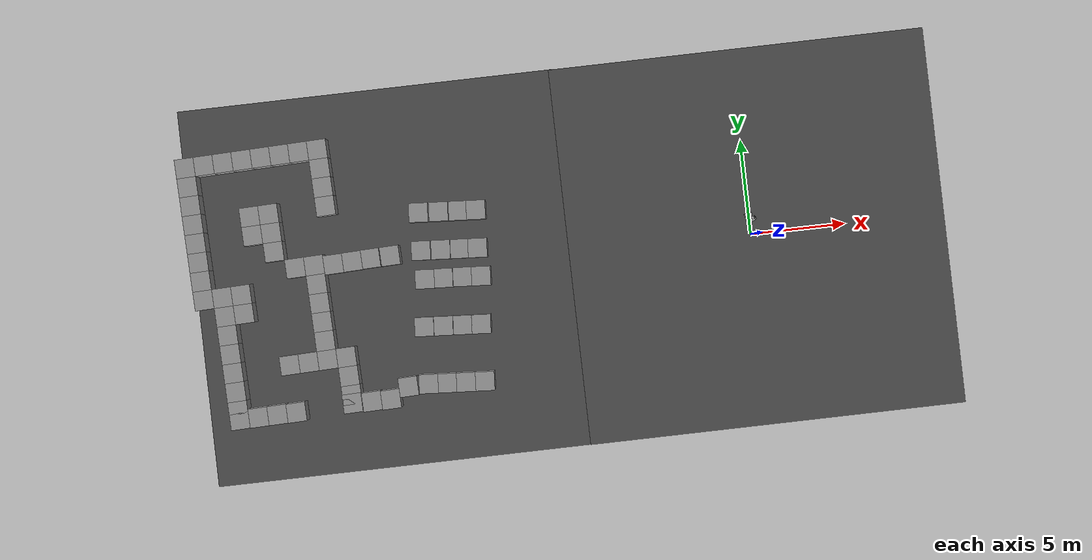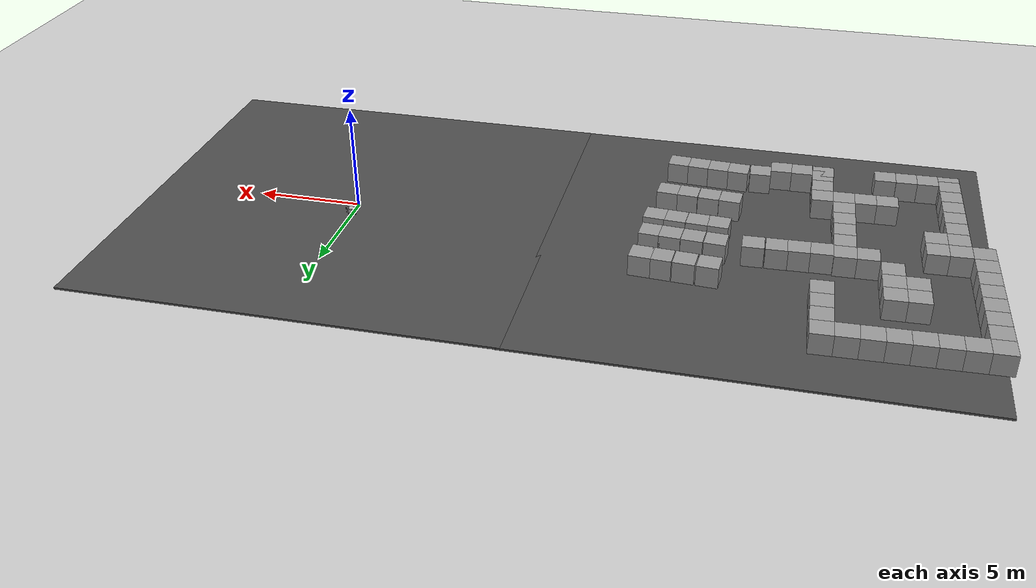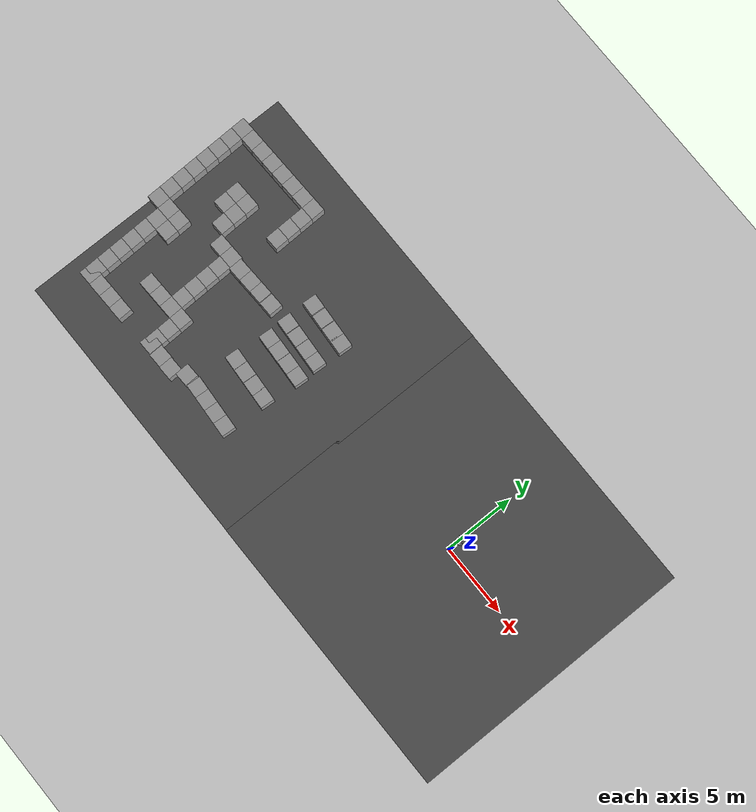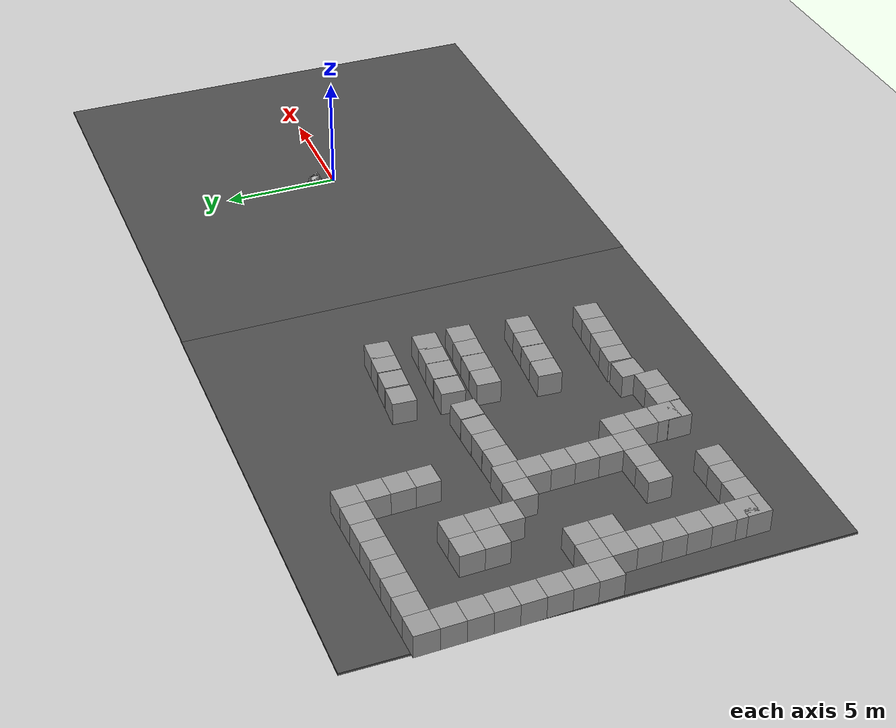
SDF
<sdf version="1.6">
 <world name="default">
  <light name="sun" type="directional">
   <pose>0 0 10 0 -0 0</pose>
   <diffuse>0.8 0.8 0.8 1</diffuse>
   <specular>0.2 0.2 0.2 1</specular>
   <attenuation>
    <range>1000</range>
    <constant>0.9</constant>
    <linear>0.01</linear>
    <quadratic>0.001</quadratic>
   </attenuation>
   <direction>-0.5 0.1 -0.9</direction>
  </light>
  <model name="ground_plane">
   <static>1</static>
   <link name="link">
    <collision name="collision">
     <geometry><plane><normal>0 0 1</normal><size>100 100</size></plane></geometry>
     <surface><friction><ode><mu>100</mu><mu2>50</mu2></ode></friction></surface>
    </collision>
    <visual name="visual">
     <cast_shadows>0</cast_shadows>
     <geometry><plane><normal>0 0 1</normal><size>100 100</size></plane></geometry>
     <material>
      <script><uri>file://media/materials/scripts/gazebo.material</uri><name>Gazebo/Grey</name></script>
     </material>
    </visual>
    <velocity_decay><linear>0</linear><angular>0</angular></velocity_decay>
   </link>
  </model>
  <physics name="default_physics" default="0" type="ode">
   <max_step_size>0.01</max_step_size>
   <real_time_factor>1</real_time_factor>
   <real_time_update_rate>100</real_time_update_rate>
  </physics>
  <scene><ambient>0.4 0.4 0.4 1</ambient><background>0.7 0.7 0.7 1</background><shadows>1</shadows></scene>
  <model name="asphalt_plane">
   <static>1</static>
   <link name="link">
    <collision name="collision"><geometry><box><size>20 20 0.1</size></box></geometry></collision>
    <visual name="visual">
     <cast_shadows>0</cast_shadows>
     <geometry><box><size>20 20 0.1</size></box></geometry>
     <material>
      <script>
       <uri>model://asphalt_plane/materials/scripts</uri>
       <uri>model://asphalt_plane/materials/textures</uri>
       <name>vrc/asphalt</name>
      </script>
     </material>
    </visual>
    <velocity_decay><linear>0</linear><angular>0</angular></velocity_decay>
   </link>
   <pose>0.276446 -0.119478 0 0 -0 0</pose>
  </model>
  <gravity>0 0 -9.8</gravity>
  <magnetic_field>6e-06 2.3e-05 -4.2e-05</magnetic_field>
  <atmosphere type="adiabatic"/>
  <spherical_coordinates>
   <surface_model>EARTH_WGS84</surface_model>
   <latitude_deg>0</latitude_deg>
   <longitude_deg>0</longitude_deg>
   <elevation>0</elevation>
   <heading_deg>0</heading_deg>
  </spherical_coordinates>
  <model name="automower">
   <link name="chassis_link">
    <inertial>
     <pose>-0.028322 -0.000726 0.048063 0 -0 0</pose>
     <mass>17.2</mass>
     <inertia>
      <ixx>1.79463</ixx>
      <ixy>-0.00275208</ixy>
      <ixz>0.120363</ixz>
      <iyy>4.47677</iyy>
      <iyz>0.00393928</iyz>
      <izz>1.68608</izz>
     </inertia>
    </inertial>
    <collision name="chassis_link_collision">
     <geometry>
      <mesh>
       <scale>1 1 1</scale>
       <uri>/home/unicorn/catkin_new/src/UNICORN-2020/unicorn_description/meshes/chassis_link.STL</uri>
      </mesh>
     </geometry>
    </collision>
    <collision name="chassis_link_fixed_joint_lump__base_laser_collision_1">
     <pose>-0.0214 -0.0049 0.465 0 -0 0</pose>
     <geometry>
      <mesh>
       <scale>1 1 1</scale>
       <uri>/home/unicorn/catkin_new/src/UNICORN-2020/unicorn_description/meshes/base_laser.STL</uri>
      </mesh>
     </geometry>
    </collision>
    <collision name="chassis_link_fixed_joint_lump__realsense_camera_collision_2">
     <pose>-0.4065 -0.03882 0.33658 0 -0 -3.14159</pose>
     <geometry>
      <mesh>
       <scale>1 1 1</scale>
       <uri>/home/unicorn/catkin_new/src/UNICORN-2020/unicorn_description/meshes/real_sense.STL</uri>
      </mesh>
     </geometry>
    </collision>
    <collision name="chassis_link_fixed_joint_lump__rear_laser_collision_3">
     <pose>-0.42145 -0.00645 0.28652 0 -0 -3.14159</pose>
     <geometry>
      <mesh>
       <scale>1 1 1</scale>
       <uri>/home/unicorn/catkin_new/src/UNICORN-2020/unicorn_description/meshes/rear_lidar.STL</uri>
      </mesh>
     </geometry>
    </collision>
    <collision name="chassis_link_fixed_joint_lump__zed_camera_collision_4">
     <pose>0.03112 -0.00552 0.36395 0 -0 0</pose>
     <geometry>
      <mesh>
       <scale>1 1 1</scale>
       <uri>/home/unicorn/catkin_new/src/UNICORN-2020/unicorn_description/meshes/zed_link.STL</uri>
      </mesh>
     </geometry>
    </collision>
    <visual name="chassis_link_visual">
     <geometry>
      <mesh>
       <scale>1 1 1</scale>
       <uri>/home/unicorn/catkin_new/src/UNICORN-2020/unicorn_description/meshes/chassis_link.STL</uri>
      </mesh>
     </geometry>
    </visual>
    <visual name="chassis_link_fixed_joint_lump__base_laser_visual_1">
     <pose>-0.0214 -0.0049 0.465 0 -0 0</pose>
     <geometry>
      <mesh>
       <scale>1 1 1</scale>
       <uri>/home/unicorn/catkin_new/src/UNICORN-2020/unicorn_description/meshes/base_laser.STL</uri>
      </mesh>
     </geometry>
     <material><script><uri>__default__</uri><name>__default__</name></script></material>
    </visual>
    <visual name="chassis_link_fixed_joint_lump__realsense_camera_visual_2">
     <pose>-0.4065 -0.03882 0.33658 0 -0 -3.14159</pose>
     <geometry>
      <mesh>
       <scale>1 1 1</scale>
       <uri>/home/unicorn/catkin_new/src/UNICORN-2020/unicorn_description/meshes/real_sense.STL</uri>
      </mesh>
     </geometry>
     <material><script><uri>__default__</uri><name>__default__</name></script></material>
    </visual>
    <visual name="chassis_link_fixed_joint_lump__rear_laser_visual_3">
     <pose>-0.42145 -0.00645 0.28652 0 -0 -3.14159</pose>
     <geometry>
      <mesh>
       <scale>1 1 1</scale>
       <uri>/home/unicorn/catkin_new/src/UNICORN-2020/unicorn_description/meshes/rear_lidar.STL</uri>
      </mesh>
     </geometry>
     <material><script><uri>__default__</uri><name>__default__</name></script></material>
    </visual>
    <visual name="chassis_link_fixed_joint_lump__zed_camera_visual_4">
     <pose>0.03112 -0.00552 0.36395 0 -0 0</pose>
     <geometry>
      <mesh>
       <scale>1 1 1</scale>
       <uri>/home/unicorn/catkin_new/src/UNICORN-2020/unicorn_description/meshes/zed_link.STL</uri>
      </mesh>
     </geometry>
     <material><script><uri>__default__</uri><name>__default__</name></script></material>
    </visual>
    <sensor name="base_laser" type="ray">
     <visualize>0</visualize>
     <update_rate>50</update_rate>
     <ray>
      <scan>
       <horizontal>
        <samples>800</samples>
        <resolution>1</resolution>
        <min_angle>-2.35619</min_angle>
        <max_angle>2.35619</max_angle>
       </horizontal>
       <vertical><samples>1</samples><min_angle>0</min_angle><max_angle>0</max_angle></vertical>
      </scan>
      <range><min>0.1</min><max>30</max><resolution>0.01</resolution></range>
      <noise><type>gaussian</type><mean>0</mean><stddev>0.001</stddev></noise>
     </ray>
     <plugin name="gazebo_ros_laser" filename="libgazebo_ros_laser.so">
      <topicName>frontLidar/scan</topicName>
      <frameName>base_laser</frameName>
      <robotNamespace>/</robotNamespace>
     </plugin>
     <pose>-0.0214 -0.0049 0.465 0 -0 0</pose>
    </sensor>
    <sensor name="openni_camera_camera" type="depth">
     <always_on>1</always_on>
     <visualize>1</visualize>
     <camera name="__default__">
      <horizontal_fov>1.39626</horizontal_fov>
      <image><width>640</width><height>480</height><format>R8G8B8</format></image>
      <clip><near>0.1</near><far>100</far></clip>
     </camera>
     <plugin name="camera_plugin" filename="libgazebo_ros_openni_kinect.so">
      <baseline>0.2</baseline>
      <alwaysOn>true</alwaysOn>
      <updateRate>0.0</updateRate>
      <cameraName>realsense</cameraName>
      <imageTopicName>/realsense/depth/image_raw</imageTopicName>
      <cameraInfoTopicName>/realsense/depth/camera_info</cameraInfoTopicName>
      <depthImageTopicName>/realsense/depth/image_raw</depthImageTopicName>
      <depthImageInfoTopicName>/realsense/depth/camera_info</depthImageInfoTopicName>
      <pointCloudTopicName>/realsense/depth/points</pointCloudTopicName>
      <frameName>realsense_depth_joint</frameName>
      <robotNamespace>/</robotNamespace>
      <pointCloudCutoff>0.05</pointCloudCutoff>
      <distortionK1>0</distortionK1>
      <distortionK2>0</distortionK2>
      <distortionK3>0</distortionK3>
      <distortionT1>0</distortionT1>
      <distortionT2>0</distortionT2>
      <CxPrime>0</CxPrime>
      <Cx>0</Cx>
      <Cy>0</Cy>
      <focalLength>0</focalLength>
      <hackBaseline>0</hackBaseline>
     </plugin>
     <pose>-0.4065 -0.03882 0.33658 0 -0 -3.14159</pose>
    </sensor>
    <sensor name="rear_laser" type="ray">
     <visualize>0</visualize>
     <update_rate>50</update_rate>
     <ray>
      <scan>
       <horizontal>
        <samples>11</samples>
        <resolution>1</resolution>
        <min_angle>-0.767945</min_angle>
        <max_angle>0.767945</max_angle>
       </horizontal>
       <vertical><samples>1</samples><min_angle>0</min_angle><max_angle>0</max_angle></vertical>
      </scan>
      <range><min>0.1</min><max>30</max><resolution>0.01</resolution></range>
      <noise><type>gaussian</type><mean>0</mean><stddev>0.001</stddev></noise>
     </ray>
     <plugin name="gazebo_ros_laser" filename="libgazebo_ros_laser.so">
      <topicName>rearLidar/scan</topicName>
      <frameName>rear_laser</frameName>
      <robotNamespace>/</robotNamespace>
     </plugin>
     <pose>-0.42145 -0.00645 0.28652 0 -0 -3.14159</pose>
    </sensor>
    <sensor name="openni_camera_camera" type="depth">
     <always_on>1</always_on>
     <visualize>1</visualize>
     <camera name="__default__">
      <horizontal_fov>1.39626</horizontal_fov>
      <image><width>640</width><height>480</height><format>R8G8B8</format></image>
      <clip><near>0.1</near><far>100</far></clip>
     </camera>
     <plugin name="camera_plugin" filename="libgazebo_ros_openni_kinect.so">
      <baseline>0.2</baseline>
      <alwaysOn>true</alwaysOn>
      <updateRate>0.0</updateRate>
      <cameraName>zed</cameraName>
      <imageTopicName>/zed/depth/image_raw</imageTopicName>
      <cameraInfoTopicName>/zed/depth/camera_info</cameraInfoTopicName>
      <depthImageTopicName>/zed/depth/image_raw</depthImageTopicName>
      <depthImageInfoTopicName>/zed/depth/camera_info</depthImageInfoTopicName>
      <pointCloudTopicName>/zed/depth/points</pointCloudTopicName>
      <frameName>zed_depth_joint</frameName>
      <robotNamespace>/</robotNamespace>
      <pointCloudCutoff>0.05</pointCloudCutoff>
      <distortionK1>0</distortionK1>
      <distortionK2>0</distortionK2>
      <distortionK3>0</distortionK3>
      <distortionT1>0</distortionT1>
      <distortionT2>0</distortionT2>
      <CxPrime>0</CxPrime>
      <Cx>0</Cx>
      <Cy>0</Cy>
      <focalLength>0</focalLength>
      <hackBaseline>0</hackBaseline>
     </plugin>
     <pose>0.03112 -0.00552 0.36395 0 -0 0</pose>
    </sensor>
   </link>
   <link name="back_left_wheel">
    <pose>0 0.24 0.122 0 -0 0</pose>
    <inertial>
     <mass>0.3</mass>
     <inertia>
      <ixx>0.00115107</ixx>
      <ixy>0</ixy>
      <ixz>0</ixz>
      <iyy>0.00115107</iyy>
      <iyz>0</iyz>
      <izz>0.00225094</izz>
     </inertia>
    </inertial>
    <collision name="back_left_wheel_collision">
     <pose>0 0 0 1.5708 -0 0</pose>
     <geometry><cylinder><length>0.032</length><radius>0.1225</radius></cylinder></geometry>
     <surface>
      <contact><ode><kp>1e+07</kp><kd>1</kd></ode></contact>
      <friction><ode><mu>100</mu><mu2>100</mu2><fdir1>1 0 0</fdir1></ode></friction>
     </surface>
    </collision>
    <visual name="back_left_wheel_visual">
     <pose>0 0 0 1.5708 -0 0</pose>
     <geometry><cylinder><length>0.032</length><radius>0.1225</radius></cylinder></geometry>
     <material>
      <script><name>Gazebo/Black</name><uri>file://media/materials/scripts/gazebo.material</uri></script>
     </material>
    </visual>
   </link>
   <joint name="back_left_wheel_joint" type="revolute">
    <child>back_left_wheel</child>
    <parent>chassis_link</parent>
    <axis>
     <xyz>0 1 0</xyz>
     <limit><lower>-1e+16</lower><upper>1e+16</upper></limit>
     <dynamics><spring_reference>0</spring_reference><spring_stiffness>0</spring_stiffness></dynamics>
     <use_parent_model_frame>1</use_parent_model_frame>
    </axis>
   </joint>
   <link name="back_right_wheel">
    <pose>0 -0.24 0.122 0 -0 0</pose>
    <inertial>
     <mass>0.3</mass>
     <inertia>
      <ixx>0.00115107</ixx>
      <ixy>0</ixy>
      <ixz>0</ixz>
      <iyy>0.00115107</iyy>
      <iyz>0</iyz>
      <izz>0.00225094</izz>
     </inertia>
    </inertial>
    <collision name="back_right_wheel_collision">
     <pose>0 0 0 1.5708 -0 0</pose>
     <geometry><cylinder><length>0.032</length><radius>0.1225</radius></cylinder></geometry>
     <surface>
      <contact><ode><kp>1e+07</kp><kd>1</kd></ode></contact>
      <friction><ode><mu>100</mu><mu2>100</mu2><fdir1>1 0 0</fdir1></ode></friction>
     </surface>
    </collision>
    <visual name="back_right_wheel_visual">
     <pose>0 0 0 1.5708 -0 0</pose>
     <geometry><cylinder><length>0.032</length><radius>0.1225</radius></cylinder></geometry>
     <material>
      <script><name>Gazebo/Black</name><uri>file://media/materials/scripts/gazebo.material</uri></script>
     </material>
    </visual>
   </link>
   <joint name="back_right_wheel_joint" type="revolute">
    <child>back_right_wheel</child>
    <parent>chassis_link</parent>
    <axis>
     <xyz>0 1 0</xyz>
     <limit><lower>-1e+16</lower><upper>1e+16</upper></limit>
     <dynamics><spring_reference>0</spring_reference><spring_stiffness>0</spring_stiffness></dynamics>
     <use_parent_model_frame>1</use_parent_model_frame>
    </axis>
   </joint>
   <link name="sw_arm_left_1">
    <pose>-0.355 0.16 0.1526 0 -0 0</pose>
    <inertial>
     <pose>-0.010549 -0.02 -0.055662 0 -0 0</pose>
     <mass>0.04</mass>
     <inertia>
      <ixx>7.68002e-05</ixx>
      <ixy>-8.43877e-06</ixy>
      <ixz>-2.13078e-05</ixz>
      <iyy>7.30325e-05</iyy>
      <iyz>-2.05283e-05</iyz>
      <izz>3.37243e-05</izz>
     </inertia>
    </inertial>
    <visual name="sw_arm_left_1_visual">
     <pose>0 0 -0.03 0 -0 0</pose>
     <geometry><cylinder><length>0.06</length><radius>0.004</radius></cylinder></geometry>
    </visual>
    <visual name="sw_arm_left_1_fixed_joint_lump__sw_arm_left_2_visual_1">
     <pose>0 -0.02 -0.059998 1.5707 -0 0</pose>
     <geometry><cylinder><length>0.04</length><radius>0.004</radius></cylinder></geometry>
    </visual>
    <visual name="sw_arm_left_1_fixed_joint_lump__sw_arm_left_3_visual_2">
     <pose>-0.021098 -0.039999 -0.081324 -3.9e-05 0.78 -9.5e-05</pose>
     <geometry><cylinder><length>0.06</length><radius>0.004</radius></cylinder></geometry>
    </visual>
    <visual name="sw_arm_left_1_fixed_joint_lump__sw_arm_left_4_visual_3">
     <pose>-0.042197 -0.019998 -0.102653 1.57066 0.78 -9.5e-05</pose>
     <geometry><cylinder><length>0.04</length><radius>0.004</radius></cylinder></geometry>
    </visual>
   </link>
   <joint name="sw_arm_left_connect_1" type="revolute">
    <child>sw_arm_left_1</child>
    <parent>chassis_link</parent>
    <axis>
     <xyz>0 0 1</xyz>
     <limit><lower>-1e+16</lower><upper>1e+16</upper></limit>
     <dynamics><spring_reference>0</spring_reference><spring_stiffness>0</spring_stiffness></dynamics>
     <use_parent_model_frame>1</use_parent_model_frame>
    </axis>
   </joint>
   <link name="front_left_swivel_wheel">
    <pose>-0.397197 0.160002 0.049945 1.57066 0.78 -9.5e-05</pose>
    <inertial>
     <mass>0.3</mass>
     <inertia><ixx>0.00025</ixx><ixy>0</ixy><ixz>0</ixz><iyy>0.00025</iyy><iyz>0</iyz><izz>0.000375</izz></inertia>
    </inertial>
    <collision name="front_left_swivel_wheel_collision">
     <geometry><cylinder><length>0.05</length><radius>0.05</radius></cylinder></geometry>
     <surface>
      <contact><ode><kp>1e+07</kp><kd>1</kd></ode></contact>
      <friction><ode><mu>0.8</mu><mu2>0.8</mu2><fdir1>1 0 0</fdir1></ode></friction>
     </surface>
    </collision>
    <visual name="front_left_swivel_wheel_visual">
     <geometry><cylinder><length>0.05</length><radius>0.05</radius></cylinder></geometry>
     <material>
      <script><name>Gazebo/Black</name><uri>file://media/materials/scripts/gazebo.material</uri></script>
     </material>
    </visual>
   </link>
   <joint name="front_left_swivel_wheel_joint" type="revolute">
    <child>front_left_swivel_wheel</child>
    <parent>sw_arm_left_1</parent>
    <axis>
     <xyz>0 -1 9.6e-05</xyz>
     <limit><lower>-1e+16</lower><upper>1e+16</upper></limit>
     <dynamics><spring_reference>0</spring_reference><spring_stiffness>0</spring_stiffness></dynamics>
     <use_parent_model_frame>1</use_parent_model_frame>
    </axis>
   </joint>
   <link name="sw_arm_right_1">
    <pose>-0.355 -0.16 0.1526 0 -0 0</pose>
    <inertial>
     <pose>-0.010549 -0.02 -0.055662 0 -0 0</pose>
     <mass>0.04</mass>
     <inertia>
      <ixx>7.68002e-05</ixx>
      <ixy>-8.43877e-06</ixy>
      <ixz>-2.13078e-05</ixz>
      <iyy>7.30325e-05</iyy>
      <iyz>-2.05283e-05</iyz>
      <izz>3.37243e-05</izz>
     </inertia>
    </inertial>
    <visual name="sw_arm_right_1_visual">
     <pose>0 0 -0.03 0 -0 0</pose>
     <geometry><cylinder><length>0.06</length><radius>0.004</radius></cylinder></geometry>
    </visual>
    <visual name="sw_arm_right_1_fixed_joint_lump__sw_arm_right_2_visual_1">
     <pose>0 -0.02 -0.059998 1.5707 -0 0</pose>
     <geometry><cylinder><length>0.04</length><radius>0.004</radius></cylinder></geometry>
    </visual>
    <visual name="sw_arm_right_1_fixed_joint_lump__sw_arm_right_3_visual_2">
     <pose>-0.021098 -0.039999 -0.081324 -3.9e-05 0.78 -9.5e-05</pose>
     <geometry><cylinder><length>0.06</length><radius>0.004</radius></cylinder></geometry>
    </visual>
    <visual name="sw_arm_right_1_fixed_joint_lump__sw_arm_right_4_visual_3">
     <pose>-0.042197 -0.019998 -0.102653 1.57066 0.78 -9.5e-05</pose>
     <geometry><cylinder><length>0.04</length><radius>0.004</radius></cylinder></geometry>
    </visual>
   </link>
   <joint name="sw_arm_right_connect_1" type="revolute">
    <child>sw_arm_right_1</child>
    <parent>chassis_link</parent>
    <axis>
     <xyz>0 0 1</xyz>
     <limit><lower>-1e+16</lower><upper>1e+16</upper></limit>
     <dynamics><spring_reference>0</spring_reference><spring_stiffness>0</spring_stiffness></dynamics>
     <use_parent_model_frame>1</use_parent_model_frame>
    </axis>
   </joint>
   <link name="front_right_swivel_wheel">
    <pose>-0.397197 -0.159998 0.049945 1.57066 0.78 -9.5e-05</pose>
    <inertial>
     <mass>0.3</mass>
     <inertia><ixx>0.00025</ixx><ixy>0</ixy><ixz>0</ixz><iyy>0.00025</iyy><iyz>0</iyz><izz>0.000375</izz></inertia>
    </inertial>
    <collision name="front_right_swivel_wheel_collision">
     <geometry><cylinder><length>0.05</length><radius>0.05</radius></cylinder></geometry>
     <surface>
      <contact><ode><kp>1e+07</kp><kd>1</kd></ode></contact>
      <friction><ode><mu>0.8</mu><mu2>0.8</mu2><fdir1>1 0 0</fdir1></ode></friction>
     </surface>
    </collision>
    <visual name="front_right_swivel_wheel_visual">
     <geometry><cylinder><length>0.05</length><radius>0.05</radius></cylinder></geometry>
     <material>
      <script><name>Gazebo/Black</name><uri>file://media/materials/scripts/gazebo.material</uri></script>
     </material>
    </visual>
   </link>
   <joint name="front_right_swivel_wheel_joint" type="revolute">
    <child>front_right_swivel_wheel</child>
    <parent>sw_arm_right_1</parent>
    <axis>
     <xyz>0 -1 9.6e-05</xyz>
     <limit><lower>-1e+16</lower><upper>1e+16</upper></limit>
     <dynamics><spring_reference>0</spring_reference><spring_stiffness>0</spring_stiffness></dynamics>
     <use_parent_model_frame>1</use_parent_model_frame>
    </axis>
   </joint>
   <plugin name="novatel_gps_sim" filename="libhector_gazebo_ros_gps.so">
    <alwaysOn>true</alwaysOn>
    <updateRate>5</updateRate>
    <frameId>odom_chassis</frameId>
    <bodyName>chassis_link</bodyName>
    <topicName>gps</topicName>
    <velocityTopicName>gps_velocity</velocityTopicName>
    <drift>5.0 5.0 5.0</drift>
    <gaussianNoise>0.1 0.1 0.1</gaussianNoise>
    <velocityDrift>0 0 0</velocityDrift>
    <velocityGaussianNoise>0.1 0.1 0.1</velocityGaussianNoise>
    <robotNamespace>/</robotNamespace>
   </plugin>
   <static>0</static>
   <plugin name="automower_gazebo_controller" filename="libam_gazebo_controller_2wd.so">
    <alwaysOn>true</alwaysOn>
    <updateRate>100.0</updateRate>
    <leftJoint>back_right_wheel_joint</leftJoint>
    <rightJoint>back_left_wheel_joint</rightJoint>
    <wheelSeparation>0.4645</wheelSeparation>
    <wheelDiameter>0.245</wheelDiameter>
    <wheelTorque>100</wheelTorque>
    <commandTopic>cmd_vel</commandTopic>
    <odometryTopic>wheelencoder/odom</odometryTopic>
    <odometryFrame>odom_chassis</odometryFrame>
    <robotBaseFrame>chassis_link</robotBaseFrame>
    <publishWheelTF>false</publishWheelTF>
    <publishWheelJointState>false</publishWheelJointState>
    <gaussianNoise>0.1</gaussianNoise>
    <accelDrift>0.5 0.5 0.5</accelDrift>
    <accelGaussianNoise>0.35 0.35 0.3</accelGaussianNoise>
    <rateDrift>0.1 0.1 0.1</rateDrift>
    <rateGaussianNoise>0.05 0.05 0.015</rateGaussianNoise>
    <headingDrift>0.1</headingDrift>
    <headingGaussianNoise>1.00</headingGaussianNoise>
    <robotNamespace>/</robotNamespace>
   </plugin>
   <plugin name="gazebo_ros_control" filename="libgazebo_ros_control.so">
    <robotNamespace>/</robotNamespace>
   </plugin>
   <plugin name="imu_plugin" filename="libhector_gazebo_ros_imu.so">
    <alwaysOn>true</alwaysOn>
    <bodyName>chassis_link</bodyName>
    <topicName>zed/imu</topicName>
    <serviceName>imu_service</serviceName>
    <updateRate>100.0</updateRate>
    <rpyOffsets>0 3.14159265359 0</rpyOffsets>
    <gaussianNoise>0.1</gaussianNoise>
    <accelDrift>0.1 0.1 0.1</accelDrift>
    <accelGaussianNoise>0.35 0.35 0.3</accelGaussianNoise>
    <rateDrift>0.1 0.1 0.1</rateDrift>
    <rateGaussianNoise>0.05 0.05 0.015</rateGaussianNoise>
    <headingDrift>0.1</headingDrift>
    <headingGaussianNoise>1.00</headingGaussianNoise>
    <robotNamespace>/</robotNamespace>
   </plugin>
   <plugin name="am_gazebo_wheelencoder" filename="libam_gazebo_wheelencoder.so">
    <robotNamespace>/</robotNamespace>
   </plugin>
   <pose>0.075904 0.759541 0.050096 0.000885 -0.005627 -1.14851</pose>
  </model>
  <model name="asphalt_plane_clone">
   <static>1</static>
   <link name="link">
    <collision name="collision"><geometry><box><size>20 20 0.1</size></box></geometry></collision>
    <visual name="visual">
     <cast_shadows>0</cast_shadows>
     <geometry><box><size>20 20 0.1</size></box></geometry>
     <material>
      <script>
       <uri>model://asphalt_plane/materials/scripts</uri>
       <uri>model://asphalt_plane/materials/textures</uri>
       <name>vrc/asphalt</name>
      </script>
     </material>
    </visual>
    <velocity_decay><linear>0</linear><angular>0</angular></velocity_decay>
   </link>
   <pose>-19.5368 -0.102889 0 0 -0 0</pose>
  </model>
  <model name="maze">
   <link name="link">
    <inertial>
     <mass>10</mass>
     <inertia>
      <ixx>0.166667</ixx>
      <ixy>0</ixy>
      <ixz>0</ixz>
      <iyy>0.166667</iyy>
      <iyz>0</iyz>
      <izz>0.166667</izz>
     </inertia>
    </inertial>
    <visual name="visual">
     <geometry><box><size>1 1 1</size></box></geometry>
     <material>
      <script><name>Gazebo/Grey</name><uri>file://media/materials/scripts/gazebo.material</uri></script>
      <ambient>0.3 0.3 0.3 1</ambient>
      <diffuse>0.7 0.7 0.7 1</diffuse>
      <specular>0.01 0.01 0.01 1</specular>
      <emissive>0 0 0 1</emissive>
      <shader type="vertex"><normal_map>__default__</normal_map></shader>
     </material>
    </visual>
    <collision name="collision">
     <geometry><box><size>1 1 1</size></box></geometry>
     <surface>
      <friction>
       <ode><mu>1</mu><mu2>1</mu2><fdir1>0 0 0</fdir1><slip1>0</slip1><slip2>0</slip2></ode>
       <torsional>
        <coefficient>1</coefficient>
        <patch_radius>0</patch_radius>
        <surface_radius>0</surface_radius>
        <use_patch_radius>1</use_patch_radius>
        <ode><slip>0</slip></ode>
       </torsional>
      </friction>
      <bounce><restitution_coefficient>0</restitution_coefficient><threshold>1e+06</threshold></bounce>
      <contact>
       <collide_without_contact>0</collide_without_contact>
       <collide_without_contact_bitmask>1</collide_without_contact_bitmask>
       <collide_bitmask>1</collide_bitmask>
       <ode>
        <soft_cfm>0</soft_cfm>
        <soft_erp>0.2</soft_erp>
        <kp>1e+13</kp>
        <kd>1</kd>
        <max_vel>0.01</max_vel>
        <min_depth>0</min_depth>
       </ode>
       <bullet>
        <split_impulse>1</split_impulse>
        <split_impulse_penetration_threshold>-0.01</split_impulse_penetration_threshold>
        <soft_cfm>0</soft_cfm>
        <soft_erp>0.2</soft_erp>
        <kp>1e+13</kp>
        <kd>1</kd>
       </bullet>
      </contact>
     </surface>
    </collision>
   </link>
   <link name="link_clone">
    <pose>-2.9747 -0.060863 -0 0 -0 0</pose>
    <inertial>
     <mass>10</mass>
     <inertia>
      <ixx>0.166667</ixx>
      <ixy>0</ixy>
      <ixz>0</ixz>
      <iyy>0.166667</iyy>
      <iyz>0</iyz>
      <izz>0.166667</izz>
     </inertia>
    </inertial>
    <visual name="visual">
     <geometry><box><size>1 1 1</size></box></geometry>
     <material>
      <script><name>Gazebo/Grey</name><uri>file://media/materials/scripts/gazebo.material</uri></script>
      <ambient>0.3 0.3 0.3 1</ambient>
      <diffuse>0.7 0.7 0.7 1</diffuse>
      <specular>0.01 0.01 0.01 1</specular>
      <emissive>0 0 0 1</emissive>
      <shader type="vertex"><normal_map>__default__</normal_map></shader>
     </material>
    </visual>
    <collision name="collision">
     <geometry><box><size>1 1 1</size></box></geometry>
     <surface>
      <friction>
       <ode><mu>1</mu><mu2>1</mu2><fdir1>0 0 0</fdir1><slip1>0</slip1><slip2>0</slip2></ode>
       <torsional>
        <coefficient>1</coefficient>
        <patch_radius>0</patch_radius>
        <surface_radius>0</surface_radius>
        <use_patch_radius>1</use_patch_radius>
        <ode><slip>0</slip></ode>
       </torsional>
      </friction>
      <bounce><restitution_coefficient>0</restitution_coefficient><threshold>1e+06</threshold></bounce>
      <contact>
       <collide_without_contact>0</collide_without_contact>
       <collide_without_contact_bitmask>1</collide_without_contact_bitmask>
       <collide_bitmask>1</collide_bitmask>
       <ode>
        <soft_cfm>0</soft_cfm>
        <soft_erp>0.2</soft_erp>
        <kp>1e+13</kp>
        <kd>1</kd>
        <max_vel>0.01</max_vel>
        <min_depth>0</min_depth>
       </ode>
       <bullet>
        <split_impulse>1</split_impulse>
        <split_impulse_penetration_threshold>-0.01</split_impulse_penetration_threshold>
        <soft_cfm>0</soft_cfm>
        <soft_erp>0.2</soft_erp>
        <kp>1e+13</kp>
        <kd>1</kd>
       </bullet>
      </contact>
     </surface>
    </collision>
   </link>
   <link name="link_clone_0">
    <pose>0.025298 0.43991 0 0 -0 0</pose>
    <inertial>
     <mass>10</mass>
     <inertia>
      <ixx>0.166667</ixx>
      <ixy>0</ixy>
      <ixz>0</ixz>
      <iyy>0.166667</iyy>
      <iyz>0</iyz>
      <izz>0.166667</izz>
     </inertia>
    </inertial>
    <visual name="visual">
     <geometry><box><size>1 1 1</size></box></geometry>
     <material>
      <script><name>Gazebo/Grey</name><uri>file://media/materials/scripts/gazebo.material</uri></script>
      <ambient>0.3 0.3 0.3 1</ambient>
      <diffuse>0.7 0.7 0.7 1</diffuse>
      <specular>0.01 0.01 0.01 1</specular>
      <emissive>0 0 0 1</emissive>
      <shader type="vertex"><normal_map>__default__</normal_map></shader>
     </material>
    </visual>
    <collision name="collision">
     <geometry><box><size>1 1 1</size></box></geometry>
     <surface>
      <friction>
       <ode><mu>1</mu><mu2>1</mu2><fdir1>0 0 0</fdir1><slip1>0</slip1><slip2>0</slip2></ode>
       <torsional>
        <coefficient>1</coefficient>
        <patch_radius>0</patch_radius>
        <surface_radius>0</surface_radius>
        <use_patch_radius>1</use_patch_radius>
        <ode><slip>0</slip></ode>
       </torsional>
      </friction>
      <bounce><restitution_coefficient>0</restitution_coefficient><threshold>1e+06</threshold></bounce>
      <contact>
       <collide_without_contact>0</collide_without_contact>
       <collide_without_contact_bitmask>1</collide_without_contact_bitmask>
       <collide_bitmask>1</collide_bitmask>
       <ode>
        <soft_cfm>0</soft_cfm>
        <soft_erp>0.2</soft_erp>
        <kp>1e+13</kp>
        <kd>1</kd>
        <max_vel>0.01</max_vel>
        <min_depth>0</min_depth>
       </ode>
       <bullet>
        <split_impulse>1</split_impulse>
        <split_impulse_penetration_threshold>-0.01</split_impulse_penetration_threshold>
        <soft_cfm>0</soft_cfm>
        <soft_erp>0.2</soft_erp>
        <kp>1e+13</kp>
        <kd>1</kd>
       </bullet>
      </contact>
     </surface>
    </collision>
   </link>
   <link name="link_clone_0_clone">
    <pose>1.0253 -0.048934 -0 0 -0 0</pose>
    <inertial>
     <mass>10</mass>
     <inertia>
      <ixx>0.166667</ixx>
      <ixy>0</ixy>
      <ixz>0</ixz>
      <iyy>0.166667</iyy>
      <iyz>0</iyz>
      <izz>0.166667</izz>
     </inertia>
    </inertial>
    <visual name="visual">
     <geometry><box><size>1 1 1</size></box></geometry>
     <material>
      <script><name>Gazebo/Grey</name><uri>file://media/materials/scripts/gazebo.material</uri></script>
      <ambient>0.3 0.3 0.3 1</ambient>
      <diffuse>0.7 0.7 0.7 1</diffuse>
      <specular>0.01 0.01 0.01 1</specular>
      <emissive>0 0 0 1</emissive>
      <shader type="vertex"><normal_map>__default__</normal_map></shader>
     </material>
    </visual>
    <collision name="collision">
     <geometry><box><size>1 1 1</size></box></geometry>
     <surface>
      <friction>
       <ode><mu>1</mu><mu2>1</mu2><fdir1>0 0 0</fdir1><slip1>0</slip1><slip2>0</slip2></ode>
       <torsional>
        <coefficient>1</coefficient>
        <patch_radius>0</patch_radius>
        <surface_radius>0</surface_radius>
        <use_patch_radius>1</use_patch_radius>
        <ode><slip>0</slip></ode>
       </torsional>
      </friction>
      <bounce><restitution_coefficient>0</restitution_coefficient><threshold>1e+06</threshold></bounce>
      <contact>
       <collide_without_contact>0</collide_without_contact>
       <collide_without_contact_bitmask>1</collide_without_contact_bitmask>
       <collide_bitmask>1</collide_bitmask>
       <ode>
        <soft_cfm>0</soft_cfm>
        <soft_erp>0.2</soft_erp>
        <kp>1e+13</kp>
        <kd>1</kd>
        <max_vel>0.01</max_vel>
        <min_depth>0</min_depth>
       </ode>
       <bullet>
        <split_impulse>1</split_impulse>
        <split_impulse_penetration_threshold>-0.01</split_impulse_penetration_threshold>
        <soft_cfm>0</soft_cfm>
        <soft_erp>0.2</soft_erp>
        <kp>1e+13</kp>
        <kd>1</kd>
       </bullet>
      </contact>
     </surface>
    </collision>
   </link>
   <link name="link_clone_0_clone_0">
    <pose>2.0253 -0.083056 0 0 -0 0</pose>
    <inertial>
     <mass>10</mass>
     <inertia>
      <ixx>0.166667</ixx>
      <ixy>0</ixy>
      <ixz>0</ixz>
      <iyy>0.166667</iyy>
      <iyz>0</iyz>
      <izz>0.166667</izz>
     </inertia>
    </inertial>
    <visual name="visual">
     <geometry><box><size>1 1 1</size></box></geometry>
     <material>
      <script><name>Gazebo/Grey</name><uri>file://media/materials/scripts/gazebo.material</uri></script>
      <ambient>0.3 0.3 0.3 1</ambient>
      <diffuse>0.7 0.7 0.7 1</diffuse>
      <specular>0.01 0.01 0.01 1</specular>
      <emissive>0 0 0 1</emissive>
      <shader type="vertex"><normal_map>__default__</normal_map></shader>
     </material>
    </visual>
    <collision name="collision">
     <geometry><box><size>1 1 1</size></box></geometry>
     <surface>
      <friction>
       <ode><mu>1</mu><mu2>1</mu2><fdir1>0 0 0</fdir1><slip1>0</slip1><slip2>0</slip2></ode>
       <torsional>
        <coefficient>1</coefficient>
        <patch_radius>0</patch_radius>
        <surface_radius>0</surface_radius>
        <use_patch_radius>1</use_patch_radius>
        <ode><slip>0</slip></ode>
       </torsional>
      </friction>
      <bounce><restitution_coefficient>0</restitution_coefficient><threshold>1e+06</threshold></bounce>
      <contact>
       <collide_without_contact>0</collide_without_contact>
       <collide_without_contact_bitmask>1</collide_without_contact_bitmask>
       <collide_bitmask>1</collide_bitmask>
       <ode>
        <soft_cfm>0</soft_cfm>
        <soft_erp>0.2</soft_erp>
        <kp>1e+13</kp>
        <kd>1</kd>
        <max_vel>0.01</max_vel>
        <min_depth>0</min_depth>
       </ode>
       <bullet>
        <split_impulse>1</split_impulse>
        <split_impulse_penetration_threshold>-0.01</split_impulse_penetration_threshold>
        <soft_cfm>0</soft_cfm>
        <soft_erp>0.2</soft_erp>
        <kp>1e+13</kp>
        <kd>1</kd>
       </bullet>
      </contact>
     </surface>
    </collision>
   </link>
   <link name="link_clone_0_clone_1">
    <pose>3.0253 0.43991 -0 0 -0 0</pose>
    <inertial>
     <mass>10</mass>
     <inertia>
      <ixx>0.166667</ixx>
      <ixy>0</ixy>
      <ixz>0</ixz>
      <iyy>0.166667</iyy>
      <iyz>0</iyz>
      <izz>0.166667</izz>
     </inertia>
    </inertial>
    <visual name="visual">
     <geometry><box><size>1 1 1</size></box></geometry>
     <material>
      <script><name>Gazebo/Grey</name><uri>file://media/materials/scripts/gazebo.material</uri></script>
      <ambient>0.3 0.3 0.3 1</ambient>
      <diffuse>0.7 0.7 0.7 1</diffuse>
      <specular>0.01 0.01 0.01 1</specular>
      <emissive>0 0 0 1</emissive>
      <shader type="vertex"><normal_map>__default__</normal_map></shader>
     </material>
    </visual>
    <collision name="collision">
     <geometry><box><size>1 1 1</size></box></geometry>
     <surface>
      <friction>
       <ode><mu>1</mu><mu2>1</mu2><fdir1>0 0 0</fdir1><slip1>0</slip1><slip2>0</slip2></ode>
       <torsional>
        <coefficient>1</coefficient>
        <patch_radius>0</patch_radius>
        <surface_radius>0</surface_radius>
        <use_patch_radius>1</use_patch_radius>
        <ode><slip>0</slip></ode>
       </torsional>
      </friction>
      <bounce><restitution_coefficient>0</restitution_coefficient><threshold>1e+06</threshold></bounce>
      <contact>
       <collide_without_contact>0</collide_without_contact>
       <collide_without_contact_bitmask>1</collide_without_contact_bitmask>
       <collide_bitmask>1</collide_bitmask>
       <ode>
        <soft_cfm>0</soft_cfm>
        <soft_erp>0.2</soft_erp>
        <kp>1e+13</kp>
        <kd>1</kd>
        <max_vel>0.01</max_vel>
        <min_depth>0</min_depth>
       </ode>
       <bullet>
        <split_impulse>1</split_impulse>
        <split_impulse_penetration_threshold>-0.01</split_impulse_penetration_threshold>
        <soft_cfm>0</soft_cfm>
        <soft_erp>0.2</soft_erp>
        <kp>1e+13</kp>
        <kd>1</kd>
       </bullet>
      </contact>
     </surface>
    </collision>
   </link>
   <link name="link_clone_0_clone_2">
    <pose>1.0253 7.36499 0 0 -0 0</pose>
    <inertial>
     <mass>10</mass>
     <inertia>
      <ixx>0.166667</ixx>
      <ixy>0</ixy>
      <ixz>0</ixz>
      <iyy>0.166667</iyy>
      <iyz>0</iyz>
      <izz>0.166667</izz>
     </inertia>
    </inertial>
    <visual name="visual">
     <geometry><box><size>1 1 1</size></box></geometry>
     <material>
      <script><name>Gazebo/Grey</name><uri>file://media/materials/scripts/gazebo.material</uri></script>
      <ambient>0.3 0.3 0.3 1</ambient>
      <diffuse>0.7 0.7 0.7 1</diffuse>
      <specular>0.01 0.01 0.01 1</specular>
      <emissive>0 0 0 1</emissive>
      <shader type="vertex"><normal_map>__default__</normal_map></shader>
     </material>
    </visual>
    <collision name="collision">
     <geometry><box><size>1 1 1</size></box></geometry>
     <surface>
      <friction>
       <ode><mu>1</mu><mu2>1</mu2><fdir1>0 0 0</fdir1><slip1>0</slip1><slip2>0</slip2></ode>
       <torsional>
        <coefficient>1</coefficient>
        <patch_radius>0</patch_radius>
        <surface_radius>0</surface_radius>
        <use_patch_radius>1</use_patch_radius>
        <ode><slip>0</slip></ode>
       </torsional>
      </friction>
      <bounce><restitution_coefficient>0</restitution_coefficient><threshold>1e+06</threshold></bounce>
      <contact>
       <collide_without_contact>0</collide_without_contact>
       <collide_without_contact_bitmask>1</collide_without_contact_bitmask>
       <collide_bitmask>1</collide_bitmask>
       <ode>
        <soft_cfm>0</soft_cfm>
        <soft_erp>0.2</soft_erp>
        <kp>1e+13</kp>
        <kd>1</kd>
        <max_vel>0.01</max_vel>
        <min_depth>0</min_depth>
       </ode>
       <bullet>
        <split_impulse>1</split_impulse>
        <split_impulse_penetration_threshold>-0.01</split_impulse_penetration_threshold>
        <soft_cfm>0</soft_cfm>
        <soft_erp>0.2</soft_erp>
        <kp>1e+13</kp>
        <kd>1</kd>
       </bullet>
      </contact>
     </surface>
    </collision>
   </link>
   <link name="link_clone_0_clone_3">
    <pose>1.98482 7.37641 -1.8e-05 0 -0 0</pose>
    <inertial>
     <mass>10</mass>
     <inertia>
      <ixx>0.166667</ixx>
      <ixy>0</ixy>
      <ixz>0</ixz>
      <iyy>0.166667</iyy>
      <iyz>0</iyz>
      <izz>0.166667</izz>
     </inertia>
    </inertial>
    <visual name="visual">
     <geometry><box><size>1 1 1</size></box></geometry>
     <material>
      <script><name>Gazebo/Grey</name><uri>file://media/materials/scripts/gazebo.material</uri></script>
      <ambient>0.3 0.3 0.3 1</ambient>
      <diffuse>0.7 0.7 0.7 1</diffuse>
      <specular>0.01 0.01 0.01 1</specular>
      <emissive>0 0 0 1</emissive>
      <shader type="vertex"><normal_map>__default__</normal_map></shader>
     </material>
    </visual>
    <collision name="collision">
     <geometry><box><size>1 1 1</size></box></geometry>
     <surface>
      <friction>
       <ode><mu>1</mu><mu2>1</mu2><fdir1>0 0 0</fdir1><slip1>0</slip1><slip2>0</slip2></ode>
       <torsional>
        <coefficient>1</coefficient>
        <patch_radius>0</patch_radius>
        <surface_radius>0</surface_radius>
        <use_patch_radius>1</use_patch_radius>
        <ode><slip>0</slip></ode>
       </torsional>
      </friction>
      <bounce><restitution_coefficient>0</restitution_coefficient><threshold>1e+06</threshold></bounce>
      <contact>
       <collide_without_contact>0</collide_without_contact>
       <collide_without_contact_bitmask>1</collide_without_contact_bitmask>
       <collide_bitmask>1</collide_bitmask>
       <ode>
        <soft_cfm>0</soft_cfm>
        <soft_erp>0.2</soft_erp>
        <kp>1e+13</kp>
        <kd>1</kd>
        <max_vel>0.01</max_vel>
        <min_depth>0</min_depth>
       </ode>
       <bullet>
        <split_impulse>1</split_impulse>
        <split_impulse_penetration_threshold>-0.01</split_impulse_penetration_threshold>
        <soft_cfm>0</soft_cfm>
        <soft_erp>0.2</soft_erp>
        <kp>1e+13</kp>
        <kd>1</kd>
       </bullet>
      </contact>
     </surface>
    </collision>
   </link>
   <link name="link_clone_0_clone_4">
    <pose>3.0253 7.37453 0 0 -0 0</pose>
    <inertial>
     <mass>10</mass>
     <inertia>
      <ixx>0.166667</ixx>
      <ixy>0</ixy>
      <ixz>0</ixz>
      <iyy>0.166667</iyy>
      <iyz>0</iyz>
      <izz>0.166667</izz>
     </inertia>
    </inertial>
    <visual name="visual">
     <geometry><box><size>1 1 1</size></box></geometry>
     <material>
      <script><name>Gazebo/Grey</name><uri>file://media/materials/scripts/gazebo.material</uri></script>
      <ambient>0.3 0.3 0.3 1</ambient>
      <diffuse>0.7 0.7 0.7 1</diffuse>
      <specular>0.01 0.01 0.01 1</specular>
      <emissive>0 0 0 1</emissive>
      <shader type="vertex"><normal_map>__default__</normal_map></shader>
     </material>
    </visual>
    <collision name="collision">
     <geometry><box><size>1 1 1</size></box></geometry>
     <surface>
      <friction>
       <ode><mu>1</mu><mu2>1</mu2><fdir1>0 0 0</fdir1><slip1>0</slip1><slip2>0</slip2></ode>
       <torsional>
        <coefficient>1</coefficient>
        <patch_radius>0</patch_radius>
        <surface_radius>0</surface_radius>
        <use_patch_radius>1</use_patch_radius>
        <ode><slip>0</slip></ode>
       </torsional>
      </friction>
      <bounce><restitution_coefficient>0</restitution_coefficient><threshold>1e+06</threshold></bounce>
      <contact>
       <collide_without_contact>0</collide_without_contact>
       <collide_without_contact_bitmask>1</collide_without_contact_bitmask>
       <collide_bitmask>1</collide_bitmask>
       <ode>
        <soft_cfm>0</soft_cfm>
        <soft_erp>0.2</soft_erp>
        <kp>1e+13</kp>
        <kd>1</kd>
        <max_vel>0.01</max_vel>
        <min_depth>0</min_depth>
       </ode>
       <bullet>
        <split_impulse>1</split_impulse>
        <split_impulse_penetration_threshold>-0.01</split_impulse_penetration_threshold>
        <soft_cfm>0</soft_cfm>
        <soft_erp>0.2</soft_erp>
        <kp>1e+13</kp>
        <kd>1</kd>
       </bullet>
      </contact>
     </surface>
    </collision>
   </link>
   <link name="link_clone_1">
    <pose>0.0253 1.43991 0 0 -0 0</pose>
    <inertial>
     <mass>10</mass>
     <inertia>
      <ixx>0.166667</ixx>
      <ixy>0</ixy>
      <ixz>0</ixz>
      <iyy>0.166667</iyy>
      <iyz>0</iyz>
      <izz>0.166667</izz>
     </inertia>
    </inertial>
    <visual name="visual">
     <geometry><box><size>1 1 1</size></box></geometry>
     <material>
      <script><name>Gazebo/Grey</name><uri>file://media/materials/scripts/gazebo.material</uri></script>
      <ambient>0.3 0.3 0.3 1</ambient>
      <diffuse>0.7 0.7 0.7 1</diffuse>
      <specular>0.01 0.01 0.01 1</specular>
      <emissive>0 0 0 1</emissive>
      <shader type="vertex"><normal_map>__default__</normal_map></shader>
     </material>
    </visual>
    <collision name="collision">
     <geometry><box><size>1 1 1</size></box></geometry>
     <surface>
      <friction>
       <ode><mu>1</mu><mu2>1</mu2><fdir1>0 0 0</fdir1><slip1>0</slip1><slip2>0</slip2></ode>
       <torsional>
        <coefficient>1</coefficient>
        <patch_radius>0</patch_radius>
        <surface_radius>0</surface_radius>
        <use_patch_radius>1</use_patch_radius>
        <ode><slip>0</slip></ode>
       </torsional>
      </friction>
      <bounce><restitution_coefficient>0</restitution_coefficient><threshold>1e+06</threshold></bounce>
      <contact>
       <collide_without_contact>0</collide_without_contact>
       <collide_without_contact_bitmask>1</collide_without_contact_bitmask>
       <collide_bitmask>1</collide_bitmask>
       <ode>
        <soft_cfm>0</soft_cfm>
        <soft_erp>0.2</soft_erp>
        <kp>1e+13</kp>
        <kd>1</kd>
        <max_vel>0.01</max_vel>
        <min_depth>0</min_depth>
       </ode>
       <bullet>
        <split_impulse>1</split_impulse>
        <split_impulse_penetration_threshold>-0.01</split_impulse_penetration_threshold>
        <soft_cfm>0</soft_cfm>
        <soft_erp>0.2</soft_erp>
        <kp>1e+13</kp>
        <kd>1</kd>
       </bullet>
      </contact>
     </surface>
    </collision>
   </link>
   <link name="link_clone_10">
    <pose>-5.9747 0.43991 -0 0 -0 0</pose>
    <inertial>
     <mass>10</mass>
     <inertia>
      <ixx>0.166667</ixx>
      <ixy>0</ixy>
      <ixz>0</ixz>
      <iyy>0.166667</iyy>
      <iyz>0</iyz>
      <izz>0.166667</izz>
     </inertia>
    </inertial>
    <visual name="visual">
     <geometry><box><size>1 1 1</size></box></geometry>
     <material>
      <script><name>Gazebo/Grey</name><uri>file://media/materials/scripts/gazebo.material</uri></script>
      <ambient>0.3 0.3 0.3 1</ambient>
      <diffuse>0.7 0.7 0.7 1</diffuse>
      <specular>0.01 0.01 0.01 1</specular>
      <emissive>0 0 0 1</emissive>
      <shader type="vertex"><normal_map>__default__</normal_map></shader>
     </material>
    </visual>
    <collision name="collision">
     <geometry><box><size>1 1 1</size></box></geometry>
     <surface>
      <friction>
       <ode><mu>1</mu><mu2>1</mu2><fdir1>0 0 0</fdir1><slip1>0</slip1><slip2>0</slip2></ode>
       <torsional>
        <coefficient>1</coefficient>
        <patch_radius>0</patch_radius>
        <surface_radius>0</surface_radius>
        <use_patch_radius>1</use_patch_radius>
        <ode><slip>0</slip></ode>
       </torsional>
      </friction>
      <bounce><restitution_coefficient>0</restitution_coefficient><threshold>1e+06</threshold></bounce>
      <contact>
       <collide_without_contact>0</collide_without_contact>
       <collide_without_contact_bitmask>1</collide_without_contact_bitmask>
       <collide_bitmask>1</collide_bitmask>
       <ode>
        <soft_cfm>0</soft_cfm>
        <soft_erp>0.2</soft_erp>
        <kp>1e+13</kp>
        <kd>1</kd>
        <max_vel>0.01</max_vel>
        <min_depth>0</min_depth>
       </ode>
       <bullet>
        <split_impulse>1</split_impulse>
        <split_impulse_penetration_threshold>-0.01</split_impulse_penetration_threshold>
        <soft_cfm>0</soft_cfm>
        <soft_erp>0.2</soft_erp>
        <kp>1e+13</kp>
        <kd>1</kd>
       </bullet>
      </contact>
     </surface>
    </collision>
   </link>
   <link name="link_clone_11">
    <pose>-5.9747 1.43991 -0 0 -0 0</pose>
    <inertial>
     <mass>10</mass>
     <inertia>
      <ixx>0.166667</ixx>
      <ixy>0</ixy>
      <ixz>0</ixz>
      <iyy>0.166667</iyy>
      <iyz>0</iyz>
      <izz>0.166667</izz>
     </inertia>
    </inertial>
    <visual name="visual">
     <geometry><box><size>1 1 1</size></box></geometry>
     <material>
      <script><name>Gazebo/Grey</name><uri>file://media/materials/scripts/gazebo.material</uri></script>
      <ambient>0.3 0.3 0.3 1</ambient>
      <diffuse>0.7 0.7 0.7 1</diffuse>
      <specular>0.01 0.01 0.01 1</specular>
      <emissive>0 0 0 1</emissive>
      <shader type="vertex"><normal_map>__default__</normal_map></shader>
     </material>
    </visual>
    <collision name="collision">
     <geometry><box><size>1 1 1</size></box></geometry>
     <surface>
      <friction>
       <ode><mu>1</mu><mu2>1</mu2><fdir1>0 0 0</fdir1><slip1>0</slip1><slip2>0</slip2></ode>
       <torsional>
        <coefficient>1</coefficient>
        <patch_radius>0</patch_radius>
        <surface_radius>0</surface_radius>
        <use_patch_radius>1</use_patch_radius>
        <ode><slip>0</slip></ode>
       </torsional>
      </friction>
      <bounce><restitution_coefficient>0</restitution_coefficient><threshold>1e+06</threshold></bounce>
      <contact>
       <collide_without_contact>0</collide_without_contact>
       <collide_without_contact_bitmask>1</collide_without_contact_bitmask>
       <collide_bitmask>1</collide_bitmask>
       <ode>
        <soft_cfm>0</soft_cfm>
        <soft_erp>0.2</soft_erp>
        <kp>1e+13</kp>
        <kd>1</kd>
        <max_vel>0.01</max_vel>
        <min_depth>0</min_depth>
       </ode>
       <bullet>
        <split_impulse>1</split_impulse>
        <split_impulse_penetration_threshold>-0.01</split_impulse_penetration_threshold>
        <soft_cfm>0</soft_cfm>
        <soft_erp>0.2</soft_erp>
        <kp>1e+13</kp>
        <kd>1</kd>
       </bullet>
      </contact>
     </surface>
    </collision>
   </link>
   <link name="link_clone_12">
    <pose>-5.9747 2.43991 -0 0 -0 0</pose>
    <inertial>
     <mass>10</mass>
     <inertia>
      <ixx>0.166667</ixx>
      <ixy>0</ixy>
      <ixz>0</ixz>
      <iyy>0.166667</iyy>
      <iyz>0</iyz>
      <izz>0.166667</izz>
     </inertia>
    </inertial>
    <visual name="visual">
     <geometry><box><size>1 1 1</size></box></geometry>
     <material>
      <script><name>Gazebo/Grey</name><uri>file://media/materials/scripts/gazebo.material</uri></script>
      <ambient>0.3 0.3 0.3 1</ambient>
      <diffuse>0.7 0.7 0.7 1</diffuse>
      <specular>0.01 0.01 0.01 1</specular>
      <emissive>0 0 0 1</emissive>
      <shader type="vertex"><normal_map>__default__</normal_map></shader>
     </material>
    </visual>
    <collision name="collision">
     <geometry><box><size>1 1 1</size></box></geometry>
     <surface>
      <friction>
       <ode><mu>1</mu><mu2>1</mu2><fdir1>0 0 0</fdir1><slip1>0</slip1><slip2>0</slip2></ode>
       <torsional>
        <coefficient>1</coefficient>
        <patch_radius>0</patch_radius>
        <surface_radius>0</surface_radius>
        <use_patch_radius>1</use_patch_radius>
        <ode><slip>0</slip></ode>
       </torsional>
      </friction>
      <bounce><restitution_coefficient>0</restitution_coefficient><threshold>1e+06</threshold></bounce>
      <contact>
       <collide_without_contact>0</collide_without_contact>
       <collide_without_contact_bitmask>1</collide_without_contact_bitmask>
       <collide_bitmask>1</collide_bitmask>
       <ode>
        <soft_cfm>0</soft_cfm>
        <soft_erp>0.2</soft_erp>
        <kp>1e+13</kp>
        <kd>1</kd>
        <max_vel>0.01</max_vel>
        <min_depth>0</min_depth>
       </ode>
       <bullet>
        <split_impulse>1</split_impulse>
        <split_impulse_penetration_threshold>-0.01</split_impulse_penetration_threshold>
        <soft_cfm>0</soft_cfm>
        <soft_erp>0.2</soft_erp>
        <kp>1e+13</kp>
        <kd>1</kd>
       </bullet>
      </contact>
     </surface>
    </collision>
   </link>
   <link name="link_clone_13">
    <pose>-5.9747 3.43991 0 0 -0 0</pose>
    <inertial>
     <mass>10</mass>
     <inertia>
      <ixx>0.166667</ixx>
      <ixy>0</ixy>
      <ixz>0</ixz>
      <iyy>0.166667</iyy>
      <iyz>0</iyz>
      <izz>0.166667</izz>
     </inertia>
    </inertial>
    <visual name="visual">
     <geometry><box><size>1 1 1</size></box></geometry>
     <material>
      <script><name>Gazebo/Grey</name><uri>file://media/materials/scripts/gazebo.material</uri></script>
      <ambient>0.3 0.3 0.3 1</ambient>
      <diffuse>0.7 0.7 0.7 1</diffuse>
      <specular>0.01 0.01 0.01 1</specular>
      <emissive>0 0 0 1</emissive>
      <shader type="vertex"><normal_map>__default__</normal_map></shader>
     </material>
    </visual>
    <collision name="collision">
     <geometry><box><size>1 1 1</size></box></geometry>
     <surface>
      <friction>
       <ode><mu>1</mu><mu2>1</mu2><fdir1>0 0 0</fdir1><slip1>0</slip1><slip2>0</slip2></ode>
       <torsional>
        <coefficient>1</coefficient>
        <patch_radius>0</patch_radius>
        <surface_radius>0</surface_radius>
        <use_patch_radius>1</use_patch_radius>
        <ode><slip>0</slip></ode>
       </torsional>
      </friction>
      <bounce><restitution_coefficient>0</restitution_coefficient><threshold>1e+06</threshold></bounce>
      <contact>
       <collide_without_contact>0</collide_without_contact>
       <collide_without_contact_bitmask>1</collide_without_contact_bitmask>
       <collide_bitmask>1</collide_bitmask>
       <ode>
        <soft_cfm>0</soft_cfm>
        <soft_erp>0.2</soft_erp>
        <kp>1e+13</kp>
        <kd>1</kd>
        <max_vel>0.01</max_vel>
        <min_depth>0</min_depth>
       </ode>
       <bullet>
        <split_impulse>1</split_impulse>
        <split_impulse_penetration_threshold>-0.01</split_impulse_penetration_threshold>
        <soft_cfm>0</soft_cfm>
        <soft_erp>0.2</soft_erp>
        <kp>1e+13</kp>
        <kd>1</kd>
       </bullet>
      </contact>
     </surface>
    </collision>
   </link>
   <link name="link_clone_14">
    <pose>-5.9747 4.43991 0 0 -0 0</pose>
    <inertial>
     <mass>10</mass>
     <inertia>
      <ixx>0.166667</ixx>
      <ixy>0</ixy>
      <ixz>0</ixz>
      <iyy>0.166667</iyy>
      <iyz>0</iyz>
      <izz>0.166667</izz>
     </inertia>
    </inertial>
    <visual name="visual">
     <geometry><box><size>1 1 1</size></box></geometry>
     <material>
      <script><name>Gazebo/Grey</name><uri>file://media/materials/scripts/gazebo.material</uri></script>
      <ambient>0.3 0.3 0.3 1</ambient>
      <diffuse>0.7 0.7 0.7 1</diffuse>
      <specular>0.01 0.01 0.01 1</specular>
      <emissive>0 0 0 1</emissive>
      <shader type="vertex"><normal_map>__default__</normal_map></shader>
     </material>
    </visual>
    <collision name="collision">
     <geometry><box><size>1 1 1</size></box></geometry>
     <surface>
      <friction>
       <ode><mu>1</mu><mu2>1</mu2><fdir1>0 0 0</fdir1><slip1>0</slip1><slip2>0</slip2></ode>
       <torsional>
        <coefficient>1</coefficient>
        <patch_radius>0</patch_radius>
        <surface_radius>0</surface_radius>
        <use_patch_radius>1</use_patch_radius>
        <ode><slip>0</slip></ode>
       </torsional>
      </friction>
      <bounce><restitution_coefficient>0</restitution_coefficient><threshold>1e+06</threshold></bounce>
      <contact>
       <collide_without_contact>0</collide_without_contact>
       <collide_without_contact_bitmask>1</collide_without_contact_bitmask>
       <collide_bitmask>1</collide_bitmask>
       <ode>
        <soft_cfm>0</soft_cfm>
        <soft_erp>0.2</soft_erp>
        <kp>1e+13</kp>
        <kd>1</kd>
        <max_vel>0.01</max_vel>
        <min_depth>0</min_depth>
       </ode>
       <bullet>
        <split_impulse>1</split_impulse>
        <split_impulse_penetration_threshold>-0.01</split_impulse_penetration_threshold>
        <soft_cfm>0</soft_cfm>
        <soft_erp>0.2</soft_erp>
        <kp>1e+13</kp>
        <kd>1</kd>
       </bullet>
      </contact>
     </surface>
    </collision>
   </link>
   <link name="link_clone_15">
    <pose>-5.9747 5.43991 0 0 -0 0</pose>
    <inertial>
     <mass>10</mass>
     <inertia>
      <ixx>0.166667</ixx>
      <ixy>0</ixy>
      <ixz>0</ixz>
      <iyy>0.166667</iyy>
      <iyz>0</iyz>
      <izz>0.166667</izz>
     </inertia>
    </inertial>
    <visual name="visual">
     <geometry><box><size>1 1 1</size></box></geometry>
     <material>
      <script><name>Gazebo/Grey</name><uri>file://media/materials/scripts/gazebo.material</uri></script>
      <ambient>0.3 0.3 0.3 1</ambient>
      <diffuse>0.7 0.7 0.7 1</diffuse>
      <specular>0.01 0.01 0.01 1</specular>
      <emissive>0 0 0 1</emissive>
      <shader type="vertex"><normal_map>__default__</normal_map></shader>
     </material>
    </visual>
    <collision name="collision">
     <geometry><box><size>1 1 1</size></box></geometry>
     <surface>
      <friction>
       <ode><mu>1</mu><mu2>1</mu2><fdir1>0 0 0</fdir1><slip1>0</slip1><slip2>0</slip2></ode>
       <torsional>
        <coefficient>1</coefficient>
        <patch_radius>0</patch_radius>
        <surface_radius>0</surface_radius>
        <use_patch_radius>1</use_patch_radius>
        <ode><slip>0</slip></ode>
       </torsional>
      </friction>
      <bounce><restitution_coefficient>0</restitution_coefficient><threshold>1e+06</threshold></bounce>
      <contact>
       <collide_without_contact>0</collide_without_contact>
       <collide_without_contact_bitmask>1</collide_without_contact_bitmask>
       <collide_bitmask>1</collide_bitmask>
       <ode>
        <soft_cfm>0</soft_cfm>
        <soft_erp>0.2</soft_erp>
        <kp>1e+13</kp>
        <kd>1</kd>
        <max_vel>0.01</max_vel>
        <min_depth>0</min_depth>
       </ode>
       <bullet>
        <split_impulse>1</split_impulse>
        <split_impulse_penetration_threshold>-0.01</split_impulse_penetration_threshold>
        <soft_cfm>0</soft_cfm>
        <soft_erp>0.2</soft_erp>
        <kp>1e+13</kp>
        <kd>1</kd>
       </bullet>
      </contact>
     </surface>
    </collision>
   </link>
   <link name="link_clone_16">
    <pose>-4.9747 5.43991 0 0 -0 0</pose>
    <inertial>
     <mass>10</mass>
     <inertia>
      <ixx>0.166667</ixx>
      <ixy>0</ixy>
      <ixz>0</ixz>
      <iyy>0.166667</iyy>
      <iyz>0</iyz>
      <izz>0.166667</izz>
     </inertia>
    </inertial>
    <visual name="visual">
     <geometry><box><size>1 1 1</size></box></geometry>
     <material>
      <script><name>Gazebo/Grey</name><uri>file://media/materials/scripts/gazebo.material</uri></script>
      <ambient>0.3 0.3 0.3 1</ambient>
      <diffuse>0.7 0.7 0.7 1</diffuse>
      <specular>0.01 0.01 0.01 1</specular>
      <emissive>0 0 0 1</emissive>
      <shader type="vertex"><normal_map>__default__</normal_map></shader>
     </material>
    </visual>
    <collision name="collision">
     <geometry><box><size>1 1 1</size></box></geometry>
     <surface>
      <friction>
       <ode><mu>1</mu><mu2>1</mu2><fdir1>0 0 0</fdir1><slip1>0</slip1><slip2>0</slip2></ode>
       <torsional>
        <coefficient>1</coefficient>
        <patch_radius>0</patch_radius>
        <surface_radius>0</surface_radius>
        <use_patch_radius>1</use_patch_radius>
        <ode><slip>0</slip></ode>
       </torsional>
      </friction>
      <bounce><restitution_coefficient>0</restitution_coefficient><threshold>1e+06</threshold></bounce>
      <contact>
       <collide_without_contact>0</collide_without_contact>
       <collide_without_contact_bitmask>1</collide_without_contact_bitmask>
       <collide_bitmask>1</collide_bitmask>
       <ode>
        <soft_cfm>0</soft_cfm>
        <soft_erp>0.2</soft_erp>
        <kp>1e+13</kp>
        <kd>1</kd>
        <max_vel>0.01</max_vel>
        <min_depth>0</min_depth>
       </ode>
       <bullet>
        <split_impulse>1</split_impulse>
        <split_impulse_penetration_threshold>-0.01</split_impulse_penetration_threshold>
        <soft_cfm>0</soft_cfm>
        <soft_erp>0.2</soft_erp>
        <kp>1e+13</kp>
        <kd>1</kd>
       </bullet>
      </contact>
     </surface>
    </collision>
   </link>
   <link name="link_clone_17">
    <pose>-4.9747 6.43991 -0 0 -0 0</pose>
    <inertial>
     <mass>10</mass>
     <inertia>
      <ixx>0.166667</ixx>
      <ixy>0</ixy>
      <ixz>0</ixz>
      <iyy>0.166667</iyy>
      <iyz>0</iyz>
      <izz>0.166667</izz>
     </inertia>
    </inertial>
    <visual name="visual">
     <geometry><box><size>1 1 1</size></box></geometry>
     <material>
      <script><name>Gazebo/Grey</name><uri>file://media/materials/scripts/gazebo.material</uri></script>
      <ambient>0.3 0.3 0.3 1</ambient>
      <diffuse>0.7 0.7 0.7 1</diffuse>
      <specular>0.01 0.01 0.01 1</specular>
      <emissive>0 0 0 1</emissive>
      <shader type="vertex"><normal_map>__default__</normal_map></shader>
     </material>
    </visual>
    <collision name="collision">
     <geometry><box><size>1 1 1</size></box></geometry>
     <surface>
      <friction>
       <ode><mu>1</mu><mu2>1</mu2><fdir1>0 0 0</fdir1><slip1>0</slip1><slip2>0</slip2></ode>
       <torsional>
        <coefficient>1</coefficient>
        <patch_radius>0</patch_radius>
        <surface_radius>0</surface_radius>
        <use_patch_radius>1</use_patch_radius>
        <ode><slip>0</slip></ode>
       </torsional>
      </friction>
      <bounce><restitution_coefficient>0</restitution_coefficient><threshold>1e+06</threshold></bounce>
      <contact>
       <collide_without_contact>0</collide_without_contact>
       <collide_without_contact_bitmask>1</collide_without_contact_bitmask>
       <collide_bitmask>1</collide_bitmask>
       <ode>
        <soft_cfm>0</soft_cfm>
        <soft_erp>0.2</soft_erp>
        <kp>1e+13</kp>
        <kd>1</kd>
        <max_vel>0.01</max_vel>
        <min_depth>0</min_depth>
       </ode>
       <bullet>
        <split_impulse>1</split_impulse>
        <split_impulse_penetration_threshold>-0.01</split_impulse_penetration_threshold>
        <soft_cfm>0</soft_cfm>
        <soft_erp>0.2</soft_erp>
        <kp>1e+13</kp>
        <kd>1</kd>
       </bullet>
      </contact>
     </surface>
    </collision>
   </link>
   <link name="link_clone_18">
    <pose>-0.974702 3.43991 0 0 -0 0</pose>
    <inertial>
     <mass>10</mass>
     <inertia>
      <ixx>0.166667</ixx>
      <ixy>0</ixy>
      <ixz>0</ixz>
      <iyy>0.166667</iyy>
      <iyz>0</iyz>
      <izz>0.166667</izz>
     </inertia>
    </inertial>
    <visual name="visual">
     <geometry><box><size>1 1 1</size></box></geometry>
     <material>
      <script><name>Gazebo/Grey</name><uri>file://media/materials/scripts/gazebo.material</uri></script>
      <ambient>0.3 0.3 0.3 1</ambient>
      <diffuse>0.7 0.7 0.7 1</diffuse>
      <specular>0.01 0.01 0.01 1</specular>
      <emissive>0 0 0 1</emissive>
      <shader type="vertex"><normal_map>__default__</normal_map></shader>
     </material>
    </visual>
    <collision name="collision">
     <geometry><box><size>1 1 1</size></box></geometry>
     <surface>
      <friction>
       <ode><mu>1</mu><mu2>1</mu2><fdir1>0 0 0</fdir1><slip1>0</slip1><slip2>0</slip2></ode>
       <torsional>
        <coefficient>1</coefficient>
        <patch_radius>0</patch_radius>
        <surface_radius>0</surface_radius>
        <use_patch_radius>1</use_patch_radius>
        <ode><slip>0</slip></ode>
       </torsional>
      </friction>
      <bounce><restitution_coefficient>0</restitution_coefficient><threshold>1e+06</threshold></bounce>
      <contact>
       <collide_without_contact>0</collide_without_contact>
       <collide_without_contact_bitmask>1</collide_without_contact_bitmask>
       <collide_bitmask>1</collide_bitmask>
       <ode>
        <soft_cfm>0</soft_cfm>
        <soft_erp>0.2</soft_erp>
        <kp>1e+13</kp>
        <kd>1</kd>
        <max_vel>0.01</max_vel>
        <min_depth>0</min_depth>
       </ode>
       <bullet>
        <split_impulse>1</split_impulse>
        <split_impulse_penetration_threshold>-0.01</split_impulse_penetration_threshold>
        <soft_cfm>0</soft_cfm>
        <soft_erp>0.2</soft_erp>
        <kp>1e+13</kp>
        <kd>1</kd>
       </bullet>
      </contact>
     </surface>
    </collision>
   </link>
   <link name="link_clone_19">
    <pose>-0.9747 4.43991 0 0 -0 0</pose>
    <inertial>
     <mass>10</mass>
     <inertia>
      <ixx>0.166667</ixx>
      <ixy>0</ixy>
      <ixz>0</ixz>
      <iyy>0.166667</iyy>
      <iyz>0</iyz>
      <izz>0.166667</izz>
     </inertia>
    </inertial>
    <visual name="visual">
     <geometry><box><size>1 1 1</size></box></geometry>
     <material>
      <script><name>Gazebo/Grey</name><uri>file://media/materials/scripts/gazebo.material</uri></script>
      <ambient>0.3 0.3 0.3 1</ambient>
      <diffuse>0.7 0.7 0.7 1</diffuse>
      <specular>0.01 0.01 0.01 1</specular>
      <emissive>0 0 0 1</emissive>
      <shader type="vertex"><normal_map>__default__</normal_map></shader>
     </material>
    </visual>
    <collision name="collision">
     <geometry><box><size>1 1 1</size></box></geometry>
     <surface>
      <friction>
       <ode><mu>1</mu><mu2>1</mu2><fdir1>0 0 0</fdir1><slip1>0</slip1><slip2>0</slip2></ode>
       <torsional>
        <coefficient>1</coefficient>
        <patch_radius>0</patch_radius>
        <surface_radius>0</surface_radius>
        <use_patch_radius>1</use_patch_radius>
        <ode><slip>0</slip></ode>
       </torsional>
      </friction>
      <bounce><restitution_coefficient>0</restitution_coefficient><threshold>1e+06</threshold></bounce>
      <contact>
       <collide_without_contact>0</collide_without_contact>
       <collide_without_contact_bitmask>1</collide_without_contact_bitmask>
       <collide_bitmask>1</collide_bitmask>
       <ode>
        <soft_cfm>0</soft_cfm>
        <soft_erp>0.2</soft_erp>
        <kp>1e+13</kp>
        <kd>1</kd>
        <max_vel>0.01</max_vel>
        <min_depth>0</min_depth>
       </ode>
       <bullet>
        <split_impulse>1</split_impulse>
        <split_impulse_penetration_threshold>-0.01</split_impulse_penetration_threshold>
        <soft_cfm>0</soft_cfm>
        <soft_erp>0.2</soft_erp>
        <kp>1e+13</kp>
        <kd>1</kd>
       </bullet>
      </contact>
     </surface>
    </collision>
   </link>
   <link name="link_clone_2">
    <pose>0.025299 2.43991 0 0 -0 0</pose>
    <inertial>
     <mass>10</mass>
     <inertia>
      <ixx>0.166667</ixx>
      <ixy>0</ixy>
      <ixz>0</ixz>
      <iyy>0.166667</iyy>
      <iyz>0</iyz>
      <izz>0.166667</izz>
     </inertia>
    </inertial>
    <visual name="visual">
     <geometry><box><size>1 1 1</size></box></geometry>
     <material>
      <script><name>Gazebo/Grey</name><uri>file://media/materials/scripts/gazebo.material</uri></script>
      <ambient>0.3 0.3 0.3 1</ambient>
      <diffuse>0.7 0.7 0.7 1</diffuse>
      <specular>0.01 0.01 0.01 1</specular>
      <emissive>0 0 0 1</emissive>
      <shader type="vertex"><normal_map>__default__</normal_map></shader>
     </material>
    </visual>
    <collision name="collision">
     <geometry><box><size>1 1 1</size></box></geometry>
     <surface>
      <friction>
       <ode><mu>1</mu><mu2>1</mu2><fdir1>0 0 0</fdir1><slip1>0</slip1><slip2>0</slip2></ode>
       <torsional>
        <coefficient>1</coefficient>
        <patch_radius>0</patch_radius>
        <surface_radius>0</surface_radius>
        <use_patch_radius>1</use_patch_radius>
        <ode><slip>0</slip></ode>
       </torsional>
      </friction>
      <bounce><restitution_coefficient>0</restitution_coefficient><threshold>1e+06</threshold></bounce>
      <contact>
       <collide_without_contact>0</collide_without_contact>
       <collide_without_contact_bitmask>1</collide_without_contact_bitmask>
       <collide_bitmask>1</collide_bitmask>
       <ode>
        <soft_cfm>0</soft_cfm>
        <soft_erp>0.2</soft_erp>
        <kp>1e+13</kp>
        <kd>1</kd>
        <max_vel>0.01</max_vel>
        <min_depth>0</min_depth>
       </ode>
       <bullet>
        <split_impulse>1</split_impulse>
        <split_impulse_penetration_threshold>-0.01</split_impulse_penetration_threshold>
        <soft_cfm>0</soft_cfm>
        <soft_erp>0.2</soft_erp>
        <kp>1e+13</kp>
        <kd>1</kd>
       </bullet>
      </contact>
     </surface>
    </collision>
   </link>
   <link name="link_clone_20">
    <pose>-0.9747 5.43991 0 0 -0 0</pose>
    <inertial>
     <mass>10</mass>
     <inertia>
      <ixx>0.166667</ixx>
      <ixy>0</ixy>
      <ixz>0</ixz>
      <iyy>0.166667</iyy>
      <iyz>0</iyz>
      <izz>0.166667</izz>
     </inertia>
    </inertial>
    <visual name="visual">
     <geometry><box><size>1 1 1</size></box></geometry>
     <material>
      <script><name>Gazebo/Grey</name><uri>file://media/materials/scripts/gazebo.material</uri></script>
      <ambient>0.3 0.3 0.3 1</ambient>
      <diffuse>0.7 0.7 0.7 1</diffuse>
      <specular>0.01 0.01 0.01 1</specular>
      <emissive>0 0 0 1</emissive>
      <shader type="vertex"><normal_map>__default__</normal_map></shader>
     </material>
    </visual>
    <collision name="collision">
     <geometry><box><size>1 1 1</size></box></geometry>
     <surface>
      <friction>
       <ode><mu>1</mu><mu2>1</mu2><fdir1>0 0 0</fdir1><slip1>0</slip1><slip2>0</slip2></ode>
       <torsional>
        <coefficient>1</coefficient>
        <patch_radius>0</patch_radius>
        <surface_radius>0</surface_radius>
        <use_patch_radius>1</use_patch_radius>
        <ode><slip>0</slip></ode>
       </torsional>
      </friction>
      <bounce><restitution_coefficient>0</restitution_coefficient><threshold>1e+06</threshold></bounce>
      <contact>
       <collide_without_contact>0</collide_without_contact>
       <collide_without_contact_bitmask>1</collide_without_contact_bitmask>
       <collide_bitmask>1</collide_bitmask>
       <ode>
        <soft_cfm>0</soft_cfm>
        <soft_erp>0.2</soft_erp>
        <kp>1e+13</kp>
        <kd>1</kd>
        <max_vel>0.01</max_vel>
        <min_depth>0</min_depth>
       </ode>
       <bullet>
        <split_impulse>1</split_impulse>
        <split_impulse_penetration_threshold>-0.01</split_impulse_penetration_threshold>
        <soft_cfm>0</soft_cfm>
        <soft_erp>0.2</soft_erp>
        <kp>1e+13</kp>
        <kd>1</kd>
       </bullet>
      </contact>
     </surface>
    </collision>
   </link>
   <link name="link_clone_21">
    <pose>-0.974701 6.43991 0 0 -0 0</pose>
    <inertial>
     <mass>10</mass>
     <inertia>
      <ixx>0.166667</ixx>
      <ixy>0</ixy>
      <ixz>0</ixz>
      <iyy>0.166667</iyy>
      <iyz>0</iyz>
      <izz>0.166667</izz>
     </inertia>
    </inertial>
    <visual name="visual">
     <geometry><box><size>1 1 1</size></box></geometry>
     <material>
      <script><name>Gazebo/Grey</name><uri>file://media/materials/scripts/gazebo.material</uri></script>
      <ambient>0.3 0.3 0.3 1</ambient>
      <diffuse>0.7 0.7 0.7 1</diffuse>
      <specular>0.01 0.01 0.01 1</specular>
      <emissive>0 0 0 1</emissive>
      <shader type="vertex"><normal_map>__default__</normal_map></shader>
     </material>
    </visual>
    <collision name="collision">
     <geometry><box><size>1 1 1</size></box></geometry>
     <surface>
      <friction>
       <ode><mu>1</mu><mu2>1</mu2><fdir1>0 0 0</fdir1><slip1>0</slip1><slip2>0</slip2></ode>
       <torsional>
        <coefficient>1</coefficient>
        <patch_radius>0</patch_radius>
        <surface_radius>0</surface_radius>
        <use_patch_radius>1</use_patch_radius>
        <ode><slip>0</slip></ode>
       </torsional>
      </friction>
      <bounce><restitution_coefficient>0</restitution_coefficient><threshold>1e+06</threshold></bounce>
      <contact>
       <collide_without_contact>0</collide_without_contact>
       <collide_without_contact_bitmask>1</collide_without_contact_bitmask>
       <collide_bitmask>1</collide_bitmask>
       <ode>
        <soft_cfm>0</soft_cfm>
        <soft_erp>0.2</soft_erp>
        <kp>1e+13</kp>
        <kd>1</kd>
        <max_vel>0.01</max_vel>
        <min_depth>0</min_depth>
       </ode>
       <bullet>
        <split_impulse>1</split_impulse>
        <split_impulse_penetration_threshold>-0.01</split_impulse_penetration_threshold>
        <soft_cfm>0</soft_cfm>
        <soft_erp>0.2</soft_erp>
        <kp>1e+13</kp>
        <kd>1</kd>
       </bullet>
      </contact>
     </surface>
    </collision>
   </link>
   <link name="link_clone_22">
    <pose>-1.9747 7.43991 0 0 -0 0</pose>
    <inertial>
     <mass>10</mass>
     <inertia>
      <ixx>0.166667</ixx>
      <ixy>0</ixy>
      <ixz>0</ixz>
      <iyy>0.166667</iyy>
      <iyz>0</iyz>
      <izz>0.166667</izz>
     </inertia>
    </inertial>
    <visual name="visual">
     <geometry><box><size>1 1 1</size></box></geometry>
     <material>
      <script><name>Gazebo/Grey</name><uri>file://media/materials/scripts/gazebo.material</uri></script>
      <ambient>0.3 0.3 0.3 1</ambient>
      <diffuse>0.7 0.7 0.7 1</diffuse>
      <specular>0.01 0.01 0.01 1</specular>
      <emissive>0 0 0 1</emissive>
      <shader type="vertex"><normal_map>__default__</normal_map></shader>
     </material>
    </visual>
    <collision name="collision">
     <geometry><box><size>1 1 1</size></box></geometry>
     <surface>
      <friction>
       <ode><mu>1</mu><mu2>1</mu2><fdir1>0 0 0</fdir1><slip1>0</slip1><slip2>0</slip2></ode>
       <torsional>
        <coefficient>1</coefficient>
        <patch_radius>0</patch_radius>
        <surface_radius>0</surface_radius>
        <use_patch_radius>1</use_patch_radius>
        <ode><slip>0</slip></ode>
       </torsional>
      </friction>
      <bounce><restitution_coefficient>0</restitution_coefficient><threshold>1e+06</threshold></bounce>
      <contact>
       <collide_without_contact>0</collide_without_contact>
       <collide_without_contact_bitmask>1</collide_without_contact_bitmask>
       <collide_bitmask>1</collide_bitmask>
       <ode>
        <soft_cfm>0</soft_cfm>
        <soft_erp>0.2</soft_erp>
        <kp>1e+13</kp>
        <kd>1</kd>
        <max_vel>0.01</max_vel>
        <min_depth>0</min_depth>
       </ode>
       <bullet>
        <split_impulse>1</split_impulse>
        <split_impulse_penetration_threshold>-0.01</split_impulse_penetration_threshold>
        <soft_cfm>0</soft_cfm>
        <soft_erp>0.2</soft_erp>
        <kp>1e+13</kp>
        <kd>1</kd>
       </bullet>
      </contact>
     </surface>
    </collision>
   </link>
   <link name="link_clone_23">
    <pose>-2.9747 8.43991 0 0 -0 0</pose>
    <inertial>
     <mass>10</mass>
     <inertia>
      <ixx>0.166667</ixx>
      <ixy>0</ixy>
      <ixz>0</ixz>
      <iyy>0.166667</iyy>
      <iyz>0</iyz>
      <izz>0.166667</izz>
     </inertia>
    </inertial>
    <visual name="visual">
     <geometry><box><size>1 1 1</size></box></geometry>
     <material>
      <script><name>Gazebo/Grey</name><uri>file://media/materials/scripts/gazebo.material</uri></script>
      <ambient>0.3 0.3 0.3 1</ambient>
      <diffuse>0.7 0.7 0.7 1</diffuse>
      <specular>0.01 0.01 0.01 1</specular>
      <emissive>0 0 0 1</emissive>
      <shader type="vertex"><normal_map>__default__</normal_map></shader>
     </material>
    </visual>
    <collision name="collision">
     <geometry><box><size>1 1 1</size></box></geometry>
     <surface>
      <friction>
       <ode><mu>1</mu><mu2>1</mu2><fdir1>0 0 0</fdir1><slip1>0</slip1><slip2>0</slip2></ode>
       <torsional>
        <coefficient>1</coefficient>
        <patch_radius>0</patch_radius>
        <surface_radius>0</surface_radius>
        <use_patch_radius>1</use_patch_radius>
        <ode><slip>0</slip></ode>
       </torsional>
      </friction>
      <bounce><restitution_coefficient>0</restitution_coefficient><threshold>1e+06</threshold></bounce>
      <contact>
       <collide_without_contact>0</collide_without_contact>
       <collide_without_contact_bitmask>1</collide_without_contact_bitmask>
       <collide_bitmask>1</collide_bitmask>
       <ode>
        <soft_cfm>0</soft_cfm>
        <soft_erp>0.2</soft_erp>
        <kp>1e+13</kp>
        <kd>1</kd>
        <max_vel>0.01</max_vel>
        <min_depth>0</min_depth>
       </ode>
       <bullet>
        <split_impulse>1</split_impulse>
        <split_impulse_penetration_threshold>-0.01</split_impulse_penetration_threshold>
        <soft_cfm>0</soft_cfm>
        <soft_erp>0.2</soft_erp>
        <kp>1e+13</kp>
        <kd>1</kd>
       </bullet>
      </contact>
     </surface>
    </collision>
   </link>
   <link name="link_clone_24">
    <pose>-3.9747 9.43991 0 0 -0 0</pose>
    <inertial>
     <mass>10</mass>
     <inertia>
      <ixx>0.166667</ixx>
      <ixy>0</ixy>
      <ixz>0</ixz>
      <iyy>0.166667</iyy>
      <iyz>0</iyz>
      <izz>0.166667</izz>
     </inertia>
    </inertial>
    <visual name="visual">
     <geometry><box><size>1 1 1</size></box></geometry>
     <material>
      <script><name>Gazebo/Grey</name><uri>file://media/materials/scripts/gazebo.material</uri></script>
      <ambient>0.3 0.3 0.3 1</ambient>
      <diffuse>0.7 0.7 0.7 1</diffuse>
      <specular>0.01 0.01 0.01 1</specular>
      <emissive>0 0 0 1</emissive>
      <shader type="vertex"><normal_map>__default__</normal_map></shader>
     </material>
    </visual>
    <collision name="collision">
     <geometry><box><size>1 1 1</size></box></geometry>
     <surface>
      <friction>
       <ode><mu>1</mu><mu2>1</mu2><fdir1>0 0 0</fdir1><slip1>0</slip1><slip2>0</slip2></ode>
       <torsional>
        <coefficient>1</coefficient>
        <patch_radius>0</patch_radius>
        <surface_radius>0</surface_radius>
        <use_patch_radius>1</use_patch_radius>
        <ode><slip>0</slip></ode>
       </torsional>
      </friction>
      <bounce><restitution_coefficient>0</restitution_coefficient><threshold>1e+06</threshold></bounce>
      <contact>
       <collide_without_contact>0</collide_without_contact>
       <collide_without_contact_bitmask>1</collide_without_contact_bitmask>
       <collide_bitmask>1</collide_bitmask>
       <ode>
        <soft_cfm>0</soft_cfm>
        <soft_erp>0.2</soft_erp>
        <kp>1e+13</kp>
        <kd>1</kd>
        <max_vel>0.01</max_vel>
        <min_depth>0</min_depth>
       </ode>
       <bullet>
        <split_impulse>1</split_impulse>
        <split_impulse_penetration_threshold>-0.01</split_impulse_penetration_threshold>
        <soft_cfm>0</soft_cfm>
        <soft_erp>0.2</soft_erp>
        <kp>1e+13</kp>
        <kd>1</kd>
       </bullet>
      </contact>
     </surface>
    </collision>
   </link>
   <link name="link_clone_25">
    <pose>-6.9747 6.43991 0 0 -0 0</pose>
    <inertial>
     <mass>10</mass>
     <inertia>
      <ixx>0.166667</ixx>
      <ixy>0</ixy>
      <ixz>0</ixz>
      <iyy>0.166667</iyy>
      <iyz>0</iyz>
      <izz>0.166667</izz>
     </inertia>
    </inertial>
    <visual name="visual">
     <geometry><box><size>1 1 1</size></box></geometry>
     <material>
      <script><name>Gazebo/Grey</name><uri>file://media/materials/scripts/gazebo.material</uri></script>
      <ambient>0.3 0.3 0.3 1</ambient>
      <diffuse>0.7 0.7 0.7 1</diffuse>
      <specular>0.01 0.01 0.01 1</specular>
      <emissive>0 0 0 1</emissive>
      <shader type="vertex"><normal_map>__default__</normal_map></shader>
     </material>
    </visual>
    <collision name="collision">
     <geometry><box><size>1 1 1</size></box></geometry>
     <surface>
      <friction>
       <ode><mu>1</mu><mu2>1</mu2><fdir1>0 0 0</fdir1><slip1>0</slip1><slip2>0</slip2></ode>
       <torsional>
        <coefficient>1</coefficient>
        <patch_radius>0</patch_radius>
        <surface_radius>0</surface_radius>
        <use_patch_radius>1</use_patch_radius>
        <ode><slip>0</slip></ode>
       </torsional>
      </friction>
      <bounce><restitution_coefficient>0</restitution_coefficient><threshold>1e+06</threshold></bounce>
      <contact>
       <collide_without_contact>0</collide_without_contact>
       <collide_without_contact_bitmask>1</collide_without_contact_bitmask>
       <collide_bitmask>1</collide_bitmask>
       <ode>
        <soft_cfm>0</soft_cfm>
        <soft_erp>0.2</soft_erp>
        <kp>1e+13</kp>
        <kd>1</kd>
        <max_vel>0.01</max_vel>
        <min_depth>0</min_depth>
       </ode>
       <bullet>
        <split_impulse>1</split_impulse>
        <split_impulse_penetration_threshold>-0.01</split_impulse_penetration_threshold>
        <soft_cfm>0</soft_cfm>
        <soft_erp>0.2</soft_erp>
        <kp>1e+13</kp>
        <kd>1</kd>
       </bullet>
      </contact>
     </surface>
    </collision>
   </link>
   <link name="link_clone_27">
    <pose>-5.9747 6.43991 0 0 -0 0</pose>
    <inertial>
     <mass>10</mass>
     <inertia>
      <ixx>0.166667</ixx>
      <ixy>0</ixy>
      <ixz>0</ixz>
      <iyy>0.166667</iyy>
      <iyz>0</iyz>
      <izz>0.166667</izz>
     </inertia>
    </inertial>
    <visual name="visual">
     <geometry><box><size>1 1 1</size></box></geometry>
     <material>
      <script><name>Gazebo/Grey</name><uri>file://media/materials/scripts/gazebo.material</uri></script>
      <ambient>0.3 0.3 0.3 1</ambient>
      <diffuse>0.7 0.7 0.7 1</diffuse>
      <specular>0.01 0.01 0.01 1</specular>
      <emissive>0 0 0 1</emissive>
      <shader type="vertex"><normal_map>__default__</normal_map></shader>
     </material>
    </visual>
    <collision name="collision">
     <geometry><box><size>1 1 1</size></box></geometry>
     <surface>
      <friction>
       <ode><mu>1</mu><mu2>1</mu2><fdir1>0 0 0</fdir1><slip1>0</slip1><slip2>0</slip2></ode>
       <torsional>
        <coefficient>1</coefficient>
        <patch_radius>0</patch_radius>
        <surface_radius>0</surface_radius>
        <use_patch_radius>1</use_patch_radius>
        <ode><slip>0</slip></ode>
       </torsional>
      </friction>
      <bounce><restitution_coefficient>0</restitution_coefficient><threshold>1e+06</threshold></bounce>
      <contact>
       <collide_without_contact>0</collide_without_contact>
       <collide_without_contact_bitmask>1</collide_without_contact_bitmask>
       <collide_bitmask>1</collide_bitmask>
       <ode>
        <soft_cfm>0</soft_cfm>
        <soft_erp>0.2</soft_erp>
        <kp>1e+13</kp>
        <kd>1</kd>
        <max_vel>0.01</max_vel>
        <min_depth>0</min_depth>
       </ode>
       <bullet>
        <split_impulse>1</split_impulse>
        <split_impulse_penetration_threshold>-0.01</split_impulse_penetration_threshold>
        <soft_cfm>0</soft_cfm>
        <soft_erp>0.2</soft_erp>
        <kp>1e+13</kp>
        <kd>1</kd>
       </bullet>
      </contact>
     </surface>
    </collision>
   </link>
   <link name="link_clone_28">
    <pose>-6.9747 7.43991 0 0 -0 0</pose>
    <inertial>
     <mass>10</mass>
     <inertia>
      <ixx>0.166667</ixx>
      <ixy>0</ixy>
      <ixz>0</ixz>
      <iyy>0.166667</iyy>
      <iyz>0</iyz>
      <izz>0.166667</izz>
     </inertia>
    </inertial>
    <visual name="visual">
     <geometry><box><size>1 1 1</size></box></geometry>
     <material>
      <script><name>Gazebo/Grey</name><uri>file://media/materials/scripts/gazebo.material</uri></script>
      <ambient>0.3 0.3 0.3 1</ambient>
      <diffuse>0.7 0.7 0.7 1</diffuse>
      <specular>0.01 0.01 0.01 1</specular>
      <emissive>0 0 0 1</emissive>
      <shader type="vertex"><normal_map>__default__</normal_map></shader>
     </material>
    </visual>
    <collision name="collision">
     <geometry><box><size>1 1 1</size></box></geometry>
     <surface>
      <friction>
       <ode><mu>1</mu><mu2>1</mu2><fdir1>0 0 0</fdir1><slip1>0</slip1><slip2>0</slip2></ode>
       <torsional>
        <coefficient>1</coefficient>
        <patch_radius>0</patch_radius>
        <surface_radius>0</surface_radius>
        <use_patch_radius>1</use_patch_radius>
        <ode><slip>0</slip></ode>
       </torsional>
      </friction>
      <bounce><restitution_coefficient>0</restitution_coefficient><threshold>1e+06</threshold></bounce>
      <contact>
       <collide_without_contact>0</collide_without_contact>
       <collide_without_contact_bitmask>1</collide_without_contact_bitmask>
       <collide_bitmask>1</collide_bitmask>
       <ode>
        <soft_cfm>0</soft_cfm>
        <soft_erp>0.2</soft_erp>
        <kp>1e+13</kp>
        <kd>1</kd>
        <max_vel>0.01</max_vel>
        <min_depth>0</min_depth>
       </ode>
       <bullet>
        <split_impulse>1</split_impulse>
        <split_impulse_penetration_threshold>-0.01</split_impulse_penetration_threshold>
        <soft_cfm>0</soft_cfm>
        <soft_erp>0.2</soft_erp>
        <kp>1e+13</kp>
        <kd>1</kd>
       </bullet>
      </contact>
     </surface>
    </collision>
   </link>
   <link name="link_clone_29">
    <pose>-6.9747 8.43991 0 0 -0 0</pose>
    <inertial>
     <mass>10</mass>
     <inertia>
      <ixx>0.166667</ixx>
      <ixy>0</ixy>
      <ixz>0</ixz>
      <iyy>0.166667</iyy>
      <iyz>0</iyz>
      <izz>0.166667</izz>
     </inertia>
    </inertial>
    <visual name="visual">
     <geometry><box><size>1 1 1</size></box></geometry>
     <material>
      <script><name>Gazebo/Grey</name><uri>file://media/materials/scripts/gazebo.material</uri></script>
      <ambient>0.3 0.3 0.3 1</ambient>
      <diffuse>0.7 0.7 0.7 1</diffuse>
      <specular>0.01 0.01 0.01 1</specular>
      <emissive>0 0 0 1</emissive>
      <shader type="vertex"><normal_map>__default__</normal_map></shader>
     </material>
    </visual>
    <collision name="collision">
     <geometry><box><size>1 1 1</size></box></geometry>
     <surface>
      <friction>
       <ode><mu>1</mu><mu2>1</mu2><fdir1>0 0 0</fdir1><slip1>0</slip1><slip2>0</slip2></ode>
       <torsional>
        <coefficient>1</coefficient>
        <patch_radius>0</patch_radius>
        <surface_radius>0</surface_radius>
        <use_patch_radius>1</use_patch_radius>
        <ode><slip>0</slip></ode>
       </torsional>
      </friction>
      <bounce><restitution_coefficient>0</restitution_coefficient><threshold>1e+06</threshold></bounce>
      <contact>
       <collide_without_contact>0</collide_without_contact>
       <collide_without_contact_bitmask>1</collide_without_contact_bitmask>
       <collide_bitmask>1</collide_bitmask>
       <ode>
        <soft_cfm>0</soft_cfm>
        <soft_erp>0.2</soft_erp>
        <kp>1e+13</kp>
        <kd>1</kd>
        <max_vel>0.01</max_vel>
        <min_depth>0</min_depth>
       </ode>
       <bullet>
        <split_impulse>1</split_impulse>
        <split_impulse_penetration_threshold>-0.01</split_impulse_penetration_threshold>
        <soft_cfm>0</soft_cfm>
        <soft_erp>0.2</soft_erp>
        <kp>1e+13</kp>
        <kd>1</kd>
       </bullet>
      </contact>
     </surface>
    </collision>
   </link>
   <link name="link_clone_3">
    <pose>-0.974702 2.43991 0 0 -0 0</pose>
    <inertial>
     <mass>10</mass>
     <inertia>
      <ixx>0.166667</ixx>
      <ixy>0</ixy>
      <ixz>0</ixz>
      <iyy>0.166667</iyy>
      <iyz>0</iyz>
      <izz>0.166667</izz>
     </inertia>
    </inertial>
    <visual name="visual">
     <geometry><box><size>1 1 1</size></box></geometry>
     <material>
      <script><name>Gazebo/Grey</name><uri>file://media/materials/scripts/gazebo.material</uri></script>
      <ambient>0.3 0.3 0.3 1</ambient>
      <diffuse>0.7 0.7 0.7 1</diffuse>
      <specular>0.01 0.01 0.01 1</specular>
      <emissive>0 0 0 1</emissive>
      <shader type="vertex"><normal_map>__default__</normal_map></shader>
     </material>
    </visual>
    <collision name="collision">
     <geometry><box><size>1 1 1</size></box></geometry>
     <surface>
      <friction>
       <ode><mu>1</mu><mu2>1</mu2><fdir1>0 0 0</fdir1><slip1>0</slip1><slip2>0</slip2></ode>
       <torsional>
        <coefficient>1</coefficient>
        <patch_radius>0</patch_radius>
        <surface_radius>0</surface_radius>
        <use_patch_radius>1</use_patch_radius>
        <ode><slip>0</slip></ode>
       </torsional>
      </friction>
      <bounce><restitution_coefficient>0</restitution_coefficient><threshold>1e+06</threshold></bounce>
      <contact>
       <collide_without_contact>0</collide_without_contact>
       <collide_without_contact_bitmask>1</collide_without_contact_bitmask>
       <collide_bitmask>1</collide_bitmask>
       <ode>
        <soft_cfm>0</soft_cfm>
        <soft_erp>0.2</soft_erp>
        <kp>1e+13</kp>
        <kd>1</kd>
        <max_vel>0.01</max_vel>
        <min_depth>0</min_depth>
       </ode>
       <bullet>
        <split_impulse>1</split_impulse>
        <split_impulse_penetration_threshold>-0.01</split_impulse_penetration_threshold>
        <soft_cfm>0</soft_cfm>
        <soft_erp>0.2</soft_erp>
        <kp>1e+13</kp>
        <kd>1</kd>
       </bullet>
      </contact>
     </surface>
    </collision>
   </link>
   <link name="link_clone_30">
    <pose>-6.9747 9.43991 0 0 -0 0</pose>
    <inertial>
     <mass>10</mass>
     <inertia>
      <ixx>0.166667</ixx>
      <ixy>0</ixy>
      <ixz>0</ixz>
      <iyy>0.166667</iyy>
      <iyz>0</iyz>
      <izz>0.166667</izz>
     </inertia>
    </inertial>
    <visual name="visual">
     <geometry><box><size>1 1 1</size></box></geometry>
     <material>
      <script><name>Gazebo/Grey</name><uri>file://media/materials/scripts/gazebo.material</uri></script>
      <ambient>0.3 0.3 0.3 1</ambient>
      <diffuse>0.7 0.7 0.7 1</diffuse>
      <specular>0.01 0.01 0.01 1</specular>
      <emissive>0 0 0 1</emissive>
      <shader type="vertex"><normal_map>__default__</normal_map></shader>
     </material>
    </visual>
    <collision name="collision">
     <geometry><box><size>1 1 1</size></box></geometry>
     <surface>
      <friction>
       <ode><mu>1</mu><mu2>1</mu2><fdir1>0 0 0</fdir1><slip1>0</slip1><slip2>0</slip2></ode>
       <torsional>
        <coefficient>1</coefficient>
        <patch_radius>0</patch_radius>
        <surface_radius>0</surface_radius>
        <use_patch_radius>1</use_patch_radius>
        <ode><slip>0</slip></ode>
       </torsional>
      </friction>
      <bounce><restitution_coefficient>0</restitution_coefficient><threshold>1e+06</threshold></bounce>
      <contact>
       <collide_without_contact>0</collide_without_contact>
       <collide_without_contact_bitmask>1</collide_without_contact_bitmask>
       <collide_bitmask>1</collide_bitmask>
       <ode>
        <soft_cfm>0</soft_cfm>
        <soft_erp>0.2</soft_erp>
        <kp>1e+13</kp>
        <kd>1</kd>
        <max_vel>0.01</max_vel>
        <min_depth>0</min_depth>
       </ode>
       <bullet>
        <split_impulse>1</split_impulse>
        <split_impulse_penetration_threshold>-0.01</split_impulse_penetration_threshold>
        <soft_cfm>0</soft_cfm>
        <soft_erp>0.2</soft_erp>
        <kp>1e+13</kp>
        <kd>1</kd>
       </bullet>
      </contact>
     </surface>
    </collision>
   </link>
   <link name="link_clone_31">
    <pose>-6.9747 10.4399 -0 0 -0 0</pose>
    <inertial>
     <mass>10</mass>
     <inertia>
      <ixx>0.166667</ixx>
      <ixy>0</ixy>
      <ixz>0</ixz>
      <iyy>0.166667</iyy>
      <iyz>0</iyz>
      <izz>0.166667</izz>
     </inertia>
    </inertial>
    <visual name="visual">
     <geometry><box><size>1 1 1</size></box></geometry>
     <material>
      <script><name>Gazebo/Grey</name><uri>file://media/materials/scripts/gazebo.material</uri></script>
      <ambient>0.3 0.3 0.3 1</ambient>
      <diffuse>0.7 0.7 0.7 1</diffuse>
      <specular>0.01 0.01 0.01 1</specular>
      <emissive>0 0 0 1</emissive>
      <shader type="vertex"><normal_map>__default__</normal_map></shader>
     </material>
    </visual>
    <collision name="collision">
     <geometry><box><size>1 1 1</size></box></geometry>
     <surface>
      <friction>
       <ode><mu>1</mu><mu2>1</mu2><fdir1>0 0 0</fdir1><slip1>0</slip1><slip2>0</slip2></ode>
       <torsional>
        <coefficient>1</coefficient>
        <patch_radius>0</patch_radius>
        <surface_radius>0</surface_radius>
        <use_patch_radius>1</use_patch_radius>
        <ode><slip>0</slip></ode>
       </torsional>
      </friction>
      <bounce><restitution_coefficient>0</restitution_coefficient><threshold>1e+06</threshold></bounce>
      <contact>
       <collide_without_contact>0</collide_without_contact>
       <collide_without_contact_bitmask>1</collide_without_contact_bitmask>
       <collide_bitmask>1</collide_bitmask>
       <ode>
        <soft_cfm>0</soft_cfm>
        <soft_erp>0.2</soft_erp>
        <kp>1e+13</kp>
        <kd>1</kd>
        <max_vel>0.01</max_vel>
        <min_depth>0</min_depth>
       </ode>
       <bullet>
        <split_impulse>1</split_impulse>
        <split_impulse_penetration_threshold>-0.01</split_impulse_penetration_threshold>
        <soft_cfm>0</soft_cfm>
        <soft_erp>0.2</soft_erp>
        <kp>1e+13</kp>
        <kd>1</kd>
       </bullet>
      </contact>
     </surface>
    </collision>
   </link>
   <link name="link_clone_32">
    <pose>-3.9747 10.4399 0 0 -0 0</pose>
    <inertial>
     <mass>10</mass>
     <inertia>
      <ixx>0.166667</ixx>
      <ixy>0</ixy>
      <ixz>0</ixz>
      <iyy>0.166667</iyy>
      <iyz>0</iyz>
      <izz>0.166667</izz>
     </inertia>
    </inertial>
    <visual name="visual">
     <geometry><box><size>1 1 1</size></box></geometry>
     <material>
      <script><name>Gazebo/Grey</name><uri>file://media/materials/scripts/gazebo.material</uri></script>
      <ambient>0.3 0.3 0.3 1</ambient>
      <diffuse>0.7 0.7 0.7 1</diffuse>
      <specular>0.01 0.01 0.01 1</specular>
      <emissive>0 0 0 1</emissive>
      <shader type="vertex"><normal_map>__default__</normal_map></shader>
     </material>
    </visual>
    <collision name="collision">
     <geometry><box><size>1 1 1</size></box></geometry>
     <surface>
      <friction>
       <ode><mu>1</mu><mu2>1</mu2><fdir1>0 0 0</fdir1><slip1>0</slip1><slip2>0</slip2></ode>
       <torsional>
        <coefficient>1</coefficient>
        <patch_radius>0</patch_radius>
        <surface_radius>0</surface_radius>
        <use_patch_radius>1</use_patch_radius>
        <ode><slip>0</slip></ode>
       </torsional>
      </friction>
      <bounce><restitution_coefficient>0</restitution_coefficient><threshold>1e+06</threshold></bounce>
      <contact>
       <collide_without_contact>0</collide_without_contact>
       <collide_without_contact_bitmask>1</collide_without_contact_bitmask>
       <collide_bitmask>1</collide_bitmask>
       <ode>
        <soft_cfm>0</soft_cfm>
        <soft_erp>0.2</soft_erp>
        <kp>1e+13</kp>
        <kd>1</kd>
        <max_vel>0.01</max_vel>
        <min_depth>0</min_depth>
       </ode>
       <bullet>
        <split_impulse>1</split_impulse>
        <split_impulse_penetration_threshold>-0.01</split_impulse_penetration_threshold>
        <soft_cfm>0</soft_cfm>
        <soft_erp>0.2</soft_erp>
        <kp>1e+13</kp>
        <kd>1</kd>
       </bullet>
      </contact>
     </surface>
    </collision>
   </link>
   <link name="link_clone_33">
    <pose>-6.9747 11.4399 -0 0 -0 0</pose>
    <inertial>
     <mass>10</mass>
     <inertia>
      <ixx>0.166667</ixx>
      <ixy>0</ixy>
      <ixz>0</ixz>
      <iyy>0.166667</iyy>
      <iyz>0</iyz>
      <izz>0.166667</izz>
     </inertia>
    </inertial>
    <visual name="visual">
     <geometry><box><size>1 1 1</size></box></geometry>
     <material>
      <script><name>Gazebo/Grey</name><uri>file://media/materials/scripts/gazebo.material</uri></script>
      <ambient>0.3 0.3 0.3 1</ambient>
      <diffuse>0.7 0.7 0.7 1</diffuse>
      <specular>0.01 0.01 0.01 1</specular>
      <emissive>0 0 0 1</emissive>
      <shader type="vertex"><normal_map>__default__</normal_map></shader>
     </material>
    </visual>
    <collision name="collision">
     <geometry><box><size>1 1 1</size></box></geometry>
     <surface>
      <friction>
       <ode><mu>1</mu><mu2>1</mu2><fdir1>0 0 0</fdir1><slip1>0</slip1><slip2>0</slip2></ode>
       <torsional>
        <coefficient>1</coefficient>
        <patch_radius>0</patch_radius>
        <surface_radius>0</surface_radius>
        <use_patch_radius>1</use_patch_radius>
        <ode><slip>0</slip></ode>
       </torsional>
      </friction>
      <bounce><restitution_coefficient>0</restitution_coefficient><threshold>1e+06</threshold></bounce>
      <contact>
       <collide_without_contact>0</collide_without_contact>
       <collide_without_contact_bitmask>1</collide_without_contact_bitmask>
       <collide_bitmask>1</collide_bitmask>
       <ode>
        <soft_cfm>0</soft_cfm>
        <soft_erp>0.2</soft_erp>
        <kp>1e+13</kp>
        <kd>1</kd>
        <max_vel>0.01</max_vel>
        <min_depth>0</min_depth>
       </ode>
       <bullet>
        <split_impulse>1</split_impulse>
        <split_impulse_penetration_threshold>-0.01</split_impulse_penetration_threshold>
        <soft_cfm>0</soft_cfm>
        <soft_erp>0.2</soft_erp>
        <kp>1e+13</kp>
        <kd>1</kd>
       </bullet>
      </contact>
     </surface>
    </collision>
   </link>
   <link name="link_clone_34">
    <pose>-6.9747 12.4399 -0 0 -0 0</pose>
    <inertial>
     <mass>10</mass>
     <inertia>
      <ixx>0.166667</ixx>
      <ixy>0</ixy>
      <ixz>0</ixz>
      <iyy>0.166667</iyy>
      <iyz>0</iyz>
      <izz>0.166667</izz>
     </inertia>
    </inertial>
    <visual name="visual">
     <geometry><box><size>1 1 1</size></box></geometry>
     <material>
      <script><name>Gazebo/Grey</name><uri>file://media/materials/scripts/gazebo.material</uri></script>
      <ambient>0.3 0.3 0.3 1</ambient>
      <diffuse>0.7 0.7 0.7 1</diffuse>
      <specular>0.01 0.01 0.01 1</specular>
      <emissive>0 0 0 1</emissive>
      <shader type="vertex"><normal_map>__default__</normal_map></shader>
     </material>
    </visual>
    <collision name="collision">
     <geometry><box><size>1 1 1</size></box></geometry>
     <surface>
      <friction>
       <ode><mu>1</mu><mu2>1</mu2><fdir1>0 0 0</fdir1><slip1>0</slip1><slip2>0</slip2></ode>
       <torsional>
        <coefficient>1</coefficient>
        <patch_radius>0</patch_radius>
        <surface_radius>0</surface_radius>
        <use_patch_radius>1</use_patch_radius>
        <ode><slip>0</slip></ode>
       </torsional>
      </friction>
      <bounce><restitution_coefficient>0</restitution_coefficient><threshold>1e+06</threshold></bounce>
      <contact>
       <collide_without_contact>0</collide_without_contact>
       <collide_without_contact_bitmask>1</collide_without_contact_bitmask>
       <collide_bitmask>1</collide_bitmask>
       <ode>
        <soft_cfm>0</soft_cfm>
        <soft_erp>0.2</soft_erp>
        <kp>1e+13</kp>
        <kd>1</kd>
        <max_vel>0.01</max_vel>
        <min_depth>0</min_depth>
       </ode>
       <bullet>
        <split_impulse>1</split_impulse>
        <split_impulse_penetration_threshold>-0.01</split_impulse_penetration_threshold>
        <soft_cfm>0</soft_cfm>
        <soft_erp>0.2</soft_erp>
        <kp>1e+13</kp>
        <kd>1</kd>
       </bullet>
      </contact>
     </surface>
    </collision>
   </link>
   <link name="link_clone_35">
    <pose>-6.9747 13.4399 -0 0 -0 0</pose>
    <inertial>
     <mass>10</mass>
     <inertia>
      <ixx>0.166667</ixx>
      <ixy>0</ixy>
      <ixz>0</ixz>
      <iyy>0.166667</iyy>
      <iyz>0</iyz>
      <izz>0.166667</izz>
     </inertia>
    </inertial>
    <visual name="visual">
     <geometry><box><size>1 1 1</size></box></geometry>
     <material>
      <script><name>Gazebo/Grey</name><uri>file://media/materials/scripts/gazebo.material</uri></script>
      <ambient>0.3 0.3 0.3 1</ambient>
      <diffuse>0.7 0.7 0.7 1</diffuse>
      <specular>0.01 0.01 0.01 1</specular>
      <emissive>0 0 0 1</emissive>
      <shader type="vertex"><normal_map>__default__</normal_map></shader>
     </material>
    </visual>
    <collision name="collision">
     <geometry><box><size>1 1 1</size></box></geometry>
     <surface>
      <friction>
       <ode><mu>1</mu><mu2>1</mu2><fdir1>0 0 0</fdir1><slip1>0</slip1><slip2>0</slip2></ode>
       <torsional>
        <coefficient>1</coefficient>
        <patch_radius>0</patch_radius>
        <surface_radius>0</surface_radius>
        <use_patch_radius>1</use_patch_radius>
        <ode><slip>0</slip></ode>
       </torsional>
      </friction>
      <bounce><restitution_coefficient>0</restitution_coefficient><threshold>1e+06</threshold></bounce>
      <contact>
       <collide_without_contact>0</collide_without_contact>
       <collide_without_contact_bitmask>1</collide_without_contact_bitmask>
       <collide_bitmask>1</collide_bitmask>
       <ode>
        <soft_cfm>0</soft_cfm>
        <soft_erp>0.2</soft_erp>
        <kp>1e+13</kp>
        <kd>1</kd>
        <max_vel>0.01</max_vel>
        <min_depth>0</min_depth>
       </ode>
       <bullet>
        <split_impulse>1</split_impulse>
        <split_impulse_penetration_threshold>-0.01</split_impulse_penetration_threshold>
        <soft_cfm>0</soft_cfm>
        <soft_erp>0.2</soft_erp>
        <kp>1e+13</kp>
        <kd>1</kd>
       </bullet>
      </contact>
     </surface>
    </collision>
   </link>
   <link name="link_clone_36">
    <pose>-5.9747 13.4399 0 0 -0 0</pose>
    <inertial>
     <mass>10</mass>
     <inertia>
      <ixx>0.166667</ixx>
      <ixy>0</ixy>
      <ixz>0</ixz>
      <iyy>0.166667</iyy>
      <iyz>0</iyz>
      <izz>0.166667</izz>
     </inertia>
    </inertial>
    <visual name="visual">
     <geometry><box><size>1 1 1</size></box></geometry>
     <material>
      <script><name>Gazebo/Grey</name><uri>file://media/materials/scripts/gazebo.material</uri></script>
      <ambient>0.3 0.3 0.3 1</ambient>
      <diffuse>0.7 0.7 0.7 1</diffuse>
      <specular>0.01 0.01 0.01 1</specular>
      <emissive>0 0 0 1</emissive>
      <shader type="vertex"><normal_map>__default__</normal_map></shader>
     </material>
    </visual>
    <collision name="collision">
     <geometry><box><size>1 1 1</size></box></geometry>
     <surface>
      <friction>
       <ode><mu>1</mu><mu2>1</mu2><fdir1>0 0 0</fdir1><slip1>0</slip1><slip2>0</slip2></ode>
       <torsional>
        <coefficient>1</coefficient>
        <patch_radius>0</patch_radius>
        <surface_radius>0</surface_radius>
        <use_patch_radius>1</use_patch_radius>
        <ode><slip>0</slip></ode>
       </torsional>
      </friction>
      <bounce><restitution_coefficient>0</restitution_coefficient><threshold>1e+06</threshold></bounce>
      <contact>
       <collide_without_contact>0</collide_without_contact>
       <collide_without_contact_bitmask>1</collide_without_contact_bitmask>
       <collide_bitmask>1</collide_bitmask>
       <ode>
        <soft_cfm>0</soft_cfm>
        <soft_erp>0.2</soft_erp>
        <kp>1e+13</kp>
        <kd>1</kd>
        <max_vel>0.01</max_vel>
        <min_depth>0</min_depth>
       </ode>
       <bullet>
        <split_impulse>1</split_impulse>
        <split_impulse_penetration_threshold>-0.01</split_impulse_penetration_threshold>
        <soft_cfm>0</soft_cfm>
        <soft_erp>0.2</soft_erp>
        <kp>1e+13</kp>
        <kd>1</kd>
       </bullet>
      </contact>
     </surface>
    </collision>
   </link>
   <link name="link_clone_37">
    <pose>-4.9747 13.4399 0 0 -0 0</pose>
    <inertial>
     <mass>10</mass>
     <inertia>
      <ixx>0.166667</ixx>
      <ixy>0</ixy>
      <ixz>0</ixz>
      <iyy>0.166667</iyy>
      <iyz>0</iyz>
      <izz>0.166667</izz>
     </inertia>
    </inertial>
    <visual name="visual">
     <geometry><box><size>1 1 1</size></box></geometry>
     <material>
      <script><name>Gazebo/Grey</name><uri>file://media/materials/scripts/gazebo.material</uri></script>
      <ambient>0.3 0.3 0.3 1</ambient>
      <diffuse>0.7 0.7 0.7 1</diffuse>
      <specular>0.01 0.01 0.01 1</specular>
      <emissive>0 0 0 1</emissive>
      <shader type="vertex"><normal_map>__default__</normal_map></shader>
     </material>
    </visual>
    <collision name="collision">
     <geometry><box><size>1 1 1</size></box></geometry>
     <surface>
      <friction>
       <ode><mu>1</mu><mu2>1</mu2><fdir1>0 0 0</fdir1><slip1>0</slip1><slip2>0</slip2></ode>
       <torsional>
        <coefficient>1</coefficient>
        <patch_radius>0</patch_radius>
        <surface_radius>0</surface_radius>
        <use_patch_radius>1</use_patch_radius>
        <ode><slip>0</slip></ode>
       </torsional>
      </friction>
      <bounce><restitution_coefficient>0</restitution_coefficient><threshold>1e+06</threshold></bounce>
      <contact>
       <collide_without_contact>0</collide_without_contact>
       <collide_without_contact_bitmask>1</collide_without_contact_bitmask>
       <collide_bitmask>1</collide_bitmask>
       <ode>
        <soft_cfm>0</soft_cfm>
        <soft_erp>0.2</soft_erp>
        <kp>1e+13</kp>
        <kd>1</kd>
        <max_vel>0.01</max_vel>
        <min_depth>0</min_depth>
       </ode>
       <bullet>
        <split_impulse>1</split_impulse>
        <split_impulse_penetration_threshold>-0.01</split_impulse_penetration_threshold>
        <soft_cfm>0</soft_cfm>
        <soft_erp>0.2</soft_erp>
        <kp>1e+13</kp>
        <kd>1</kd>
       </bullet>
      </contact>
     </surface>
    </collision>
   </link>
   <link name="link_clone_38">
    <pose>-3.9747 13.4399 0 0 -0 0</pose>
    <inertial>
     <mass>10</mass>
     <inertia>
      <ixx>0.166667</ixx>
      <ixy>0</ixy>
      <ixz>0</ixz>
      <iyy>0.166667</iyy>
      <iyz>0</iyz>
      <izz>0.166667</izz>
     </inertia>
    </inertial>
    <visual name="visual">
     <geometry><box><size>1 1 1</size></box></geometry>
     <material>
      <script><name>Gazebo/Grey</name><uri>file://media/materials/scripts/gazebo.material</uri></script>
      <ambient>0.3 0.3 0.3 1</ambient>
      <diffuse>0.7 0.7 0.7 1</diffuse>
      <specular>0.01 0.01 0.01 1</specular>
      <emissive>0 0 0 1</emissive>
      <shader type="vertex"><normal_map>__default__</normal_map></shader>
     </material>
    </visual>
    <collision name="collision">
     <geometry><box><size>1 1 1</size></box></geometry>
     <surface>
      <friction>
       <ode><mu>1</mu><mu2>1</mu2><fdir1>0 0 0</fdir1><slip1>0</slip1><slip2>0</slip2></ode>
       <torsional>
        <coefficient>1</coefficient>
        <patch_radius>0</patch_radius>
        <surface_radius>0</surface_radius>
        <use_patch_radius>1</use_patch_radius>
        <ode><slip>0</slip></ode>
       </torsional>
      </friction>
      <bounce><restitution_coefficient>0</restitution_coefficient><threshold>1e+06</threshold></bounce>
      <contact>
       <collide_without_contact>0</collide_without_contact>
       <collide_without_contact_bitmask>1</collide_without_contact_bitmask>
       <collide_bitmask>1</collide_bitmask>
       <ode>
        <soft_cfm>0</soft_cfm>
        <soft_erp>0.2</soft_erp>
        <kp>1e+13</kp>
        <kd>1</kd>
        <max_vel>0.01</max_vel>
        <min_depth>0</min_depth>
       </ode>
       <bullet>
        <split_impulse>1</split_impulse>
        <split_impulse_penetration_threshold>-0.01</split_impulse_penetration_threshold>
        <soft_cfm>0</soft_cfm>
        <soft_erp>0.2</soft_erp>
        <kp>1e+13</kp>
        <kd>1</kd>
       </bullet>
      </contact>
     </surface>
    </collision>
   </link>
   <link name="link_clone_39">
    <pose>-2.9747 13.4399 -0 0 -0 0</pose>
    <inertial>
     <mass>10</mass>
     <inertia>
      <ixx>0.166667</ixx>
      <ixy>0</ixy>
      <ixz>0</ixz>
      <iyy>0.166667</iyy>
      <iyz>0</iyz>
      <izz>0.166667</izz>
     </inertia>
    </inertial>
    <visual name="visual">
     <geometry><box><size>1 1 1</size></box></geometry>
     <material>
      <script><name>Gazebo/Grey</name><uri>file://media/materials/scripts/gazebo.material</uri></script>
      <ambient>0.3 0.3 0.3 1</ambient>
      <diffuse>0.7 0.7 0.7 1</diffuse>
      <specular>0.01 0.01 0.01 1</specular>
      <emissive>0 0 0 1</emissive>
      <shader type="vertex"><normal_map>__default__</normal_map></shader>
     </material>
    </visual>
    <collision name="collision">
     <geometry><box><size>1 1 1</size></box></geometry>
     <surface>
      <friction>
       <ode><mu>1</mu><mu2>1</mu2><fdir1>0 0 0</fdir1><slip1>0</slip1><slip2>0</slip2></ode>
       <torsional>
        <coefficient>1</coefficient>
        <patch_radius>0</patch_radius>
        <surface_radius>0</surface_radius>
        <use_patch_radius>1</use_patch_radius>
        <ode><slip>0</slip></ode>
       </torsional>
      </friction>
      <bounce><restitution_coefficient>0</restitution_coefficient><threshold>1e+06</threshold></bounce>
      <contact>
       <collide_without_contact>0</collide_without_contact>
       <collide_without_contact_bitmask>1</collide_without_contact_bitmask>
       <collide_bitmask>1</collide_bitmask>
       <ode>
        <soft_cfm>0</soft_cfm>
        <soft_erp>0.2</soft_erp>
        <kp>1e+13</kp>
        <kd>1</kd>
        <max_vel>0.01</max_vel>
        <min_depth>0</min_depth>
       </ode>
       <bullet>
        <split_impulse>1</split_impulse>
        <split_impulse_penetration_threshold>-0.01</split_impulse_penetration_threshold>
        <soft_cfm>0</soft_cfm>
        <soft_erp>0.2</soft_erp>
        <kp>1e+13</kp>
        <kd>1</kd>
       </bullet>
      </contact>
     </surface>
    </collision>
   </link>
   <link name="link_clone_4">
    <pose>-1.9747 2.43991 -0 0 -0 0</pose>
    <inertial>
     <mass>10</mass>
     <inertia>
      <ixx>0.166667</ixx>
      <ixy>0</ixy>
      <ixz>0</ixz>
      <iyy>0.166667</iyy>
      <iyz>0</iyz>
      <izz>0.166667</izz>
     </inertia>
    </inertial>
    <visual name="visual">
     <geometry><box><size>1 1 1</size></box></geometry>
     <material>
      <script><name>Gazebo/Grey</name><uri>file://media/materials/scripts/gazebo.material</uri></script>
      <ambient>0.3 0.3 0.3 1</ambient>
      <diffuse>0.7 0.7 0.7 1</diffuse>
      <specular>0.01 0.01 0.01 1</specular>
      <emissive>0 0 0 1</emissive>
      <shader type="vertex"><normal_map>__default__</normal_map></shader>
     </material>
    </visual>
    <collision name="collision">
     <geometry><box><size>1 1 1</size></box></geometry>
     <surface>
      <friction>
       <ode><mu>1</mu><mu2>1</mu2><fdir1>0 0 0</fdir1><slip1>0</slip1><slip2>0</slip2></ode>
       <torsional>
        <coefficient>1</coefficient>
        <patch_radius>0</patch_radius>
        <surface_radius>0</surface_radius>
        <use_patch_radius>1</use_patch_radius>
        <ode><slip>0</slip></ode>
       </torsional>
      </friction>
      <bounce><restitution_coefficient>0</restitution_coefficient><threshold>1e+06</threshold></bounce>
      <contact>
       <collide_without_contact>0</collide_without_contact>
       <collide_without_contact_bitmask>1</collide_without_contact_bitmask>
       <collide_bitmask>1</collide_bitmask>
       <ode>
        <soft_cfm>0</soft_cfm>
        <soft_erp>0.2</soft_erp>
        <kp>1e+13</kp>
        <kd>1</kd>
        <max_vel>0.01</max_vel>
        <min_depth>0</min_depth>
       </ode>
       <bullet>
        <split_impulse>1</split_impulse>
        <split_impulse_penetration_threshold>-0.01</split_impulse_penetration_threshold>
        <soft_cfm>0</soft_cfm>
        <soft_erp>0.2</soft_erp>
        <kp>1e+13</kp>
        <kd>1</kd>
       </bullet>
      </contact>
     </surface>
    </collision>
   </link>
   <link name="link_clone_40">
    <pose>-1.9747 13.4399 -0 0 -0 0</pose>
    <inertial>
     <mass>10</mass>
     <inertia>
      <ixx>0.166667</ixx>
      <ixy>0</ixy>
      <ixz>0</ixz>
      <iyy>0.166667</iyy>
      <iyz>0</iyz>
      <izz>0.166667</izz>
     </inertia>
    </inertial>
    <visual name="visual">
     <geometry><box><size>1 1 1</size></box></geometry>
     <material>
      <script><name>Gazebo/Grey</name><uri>file://media/materials/scripts/gazebo.material</uri></script>
      <ambient>0.3 0.3 0.3 1</ambient>
      <diffuse>0.7 0.7 0.7 1</diffuse>
      <specular>0.01 0.01 0.01 1</specular>
      <emissive>0 0 0 1</emissive>
      <shader type="vertex"><normal_map>__default__</normal_map></shader>
     </material>
    </visual>
    <collision name="collision">
     <geometry><box><size>1 1 1</size></box></geometry>
     <surface>
      <friction>
       <ode><mu>1</mu><mu2>1</mu2><fdir1>0 0 0</fdir1><slip1>0</slip1><slip2>0</slip2></ode>
       <torsional>
        <coefficient>1</coefficient>
        <patch_radius>0</patch_radius>
        <surface_radius>0</surface_radius>
        <use_patch_radius>1</use_patch_radius>
        <ode><slip>0</slip></ode>
       </torsional>
      </friction>
      <bounce><restitution_coefficient>0</restitution_coefficient><threshold>1e+06</threshold></bounce>
      <contact>
       <collide_without_contact>0</collide_without_contact>
       <collide_without_contact_bitmask>1</collide_without_contact_bitmask>
       <collide_bitmask>1</collide_bitmask>
       <ode>
        <soft_cfm>0</soft_cfm>
        <soft_erp>0.2</soft_erp>
        <kp>1e+13</kp>
        <kd>1</kd>
        <max_vel>0.01</max_vel>
        <min_depth>0</min_depth>
       </ode>
       <bullet>
        <split_impulse>1</split_impulse>
        <split_impulse_penetration_threshold>-0.01</split_impulse_penetration_threshold>
        <soft_cfm>0</soft_cfm>
        <soft_erp>0.2</soft_erp>
        <kp>1e+13</kp>
        <kd>1</kd>
       </bullet>
      </contact>
     </surface>
    </collision>
   </link>
   <link name="link_clone_41">
    <pose>-0.974701 13.4399 0 0 -0 0</pose>
    <inertial>
     <mass>10</mass>
     <inertia>
      <ixx>0.166667</ixx>
      <ixy>0</ixy>
      <ixz>0</ixz>
      <iyy>0.166667</iyy>
      <iyz>0</iyz>
      <izz>0.166667</izz>
     </inertia>
    </inertial>
    <visual name="visual">
     <geometry><box><size>1 1 1</size></box></geometry>
     <material>
      <script><name>Gazebo/Grey</name><uri>file://media/materials/scripts/gazebo.material</uri></script>
      <ambient>0.3 0.3 0.3 1</ambient>
      <diffuse>0.7 0.7 0.7 1</diffuse>
      <specular>0.01 0.01 0.01 1</specular>
      <emissive>0 0 0 1</emissive>
      <shader type="vertex"><normal_map>__default__</normal_map></shader>
     </material>
    </visual>
    <collision name="collision">
     <geometry><box><size>1 1 1</size></box></geometry>
     <surface>
      <friction>
       <ode><mu>1</mu><mu2>1</mu2><fdir1>0 0 0</fdir1><slip1>0</slip1><slip2>0</slip2></ode>
       <torsional>
        <coefficient>1</coefficient>
        <patch_radius>0</patch_radius>
        <surface_radius>0</surface_radius>
        <use_patch_radius>1</use_patch_radius>
        <ode><slip>0</slip></ode>
       </torsional>
      </friction>
      <bounce><restitution_coefficient>0</restitution_coefficient><threshold>1e+06</threshold></bounce>
      <contact>
       <collide_without_contact>0</collide_without_contact>
       <collide_without_contact_bitmask>1</collide_without_contact_bitmask>
       <collide_bitmask>1</collide_bitmask>
       <ode>
        <soft_cfm>0</soft_cfm>
        <soft_erp>0.2</soft_erp>
        <kp>1e+13</kp>
        <kd>1</kd>
        <max_vel>0.01</max_vel>
        <min_depth>0</min_depth>
       </ode>
       <bullet>
        <split_impulse>1</split_impulse>
        <split_impulse_penetration_threshold>-0.01</split_impulse_penetration_threshold>
        <soft_cfm>0</soft_cfm>
        <soft_erp>0.2</soft_erp>
        <kp>1e+13</kp>
        <kd>1</kd>
       </bullet>
      </contact>
     </surface>
    </collision>
   </link>
   <link name="link_clone_42">
    <pose>0.025298 13.4399 0 0 -0 0</pose>
    <inertial>
     <mass>10</mass>
     <inertia>
      <ixx>0.166667</ixx>
      <ixy>0</ixy>
      <ixz>0</ixz>
      <iyy>0.166667</iyy>
      <iyz>0</iyz>
      <izz>0.166667</izz>
     </inertia>
    </inertial>
    <visual name="visual">
     <geometry><box><size>1 1 1</size></box></geometry>
     <material>
      <script><name>Gazebo/Grey</name><uri>file://media/materials/scripts/gazebo.material</uri></script>
      <ambient>0.3 0.3 0.3 1</ambient>
      <diffuse>0.7 0.7 0.7 1</diffuse>
      <specular>0.01 0.01 0.01 1</specular>
      <emissive>0 0 0 1</emissive>
      <shader type="vertex"><normal_map>__default__</normal_map></shader>
     </material>
    </visual>
    <collision name="collision">
     <geometry><box><size>1 1 1</size></box></geometry>
     <surface>
      <friction>
       <ode><mu>1</mu><mu2>1</mu2><fdir1>0 0 0</fdir1><slip1>0</slip1><slip2>0</slip2></ode>
       <torsional>
        <coefficient>1</coefficient>
        <patch_radius>0</patch_radius>
        <surface_radius>0</surface_radius>
        <use_patch_radius>1</use_patch_radius>
        <ode><slip>0</slip></ode>
       </torsional>
      </friction>
      <bounce><restitution_coefficient>0</restitution_coefficient><threshold>1e+06</threshold></bounce>
      <contact>
       <collide_without_contact>0</collide_without_contact>
       <collide_without_contact_bitmask>1</collide_without_contact_bitmask>
       <collide_bitmask>1</collide_bitmask>
       <ode>
        <soft_cfm>0</soft_cfm>
        <soft_erp>0.2</soft_erp>
        <kp>1e+13</kp>
        <kd>1</kd>
        <max_vel>0.01</max_vel>
        <min_depth>0</min_depth>
       </ode>
       <bullet>
        <split_impulse>1</split_impulse>
        <split_impulse_penetration_threshold>-0.01</split_impulse_penetration_threshold>
        <soft_cfm>0</soft_cfm>
        <soft_erp>0.2</soft_erp>
        <kp>1e+13</kp>
        <kd>1</kd>
       </bullet>
      </contact>
     </surface>
    </collision>
   </link>
   <link name="link_clone_43">
    <pose>-2.9747 10.4399 0 0 -0 0</pose>
    <inertial>
     <mass>10</mass>
     <inertia>
      <ixx>0.166667</ixx>
      <ixy>0</ixy>
      <ixz>0</ixz>
      <iyy>0.166667</iyy>
      <iyz>0</iyz>
      <izz>0.166667</izz>
     </inertia>
    </inertial>
    <visual name="visual">
     <geometry><box><size>1 1 1</size></box></geometry>
     <material>
      <script><name>Gazebo/Grey</name><uri>file://media/materials/scripts/gazebo.material</uri></script>
      <ambient>0.3 0.3 0.3 1</ambient>
      <diffuse>0.7 0.7 0.7 1</diffuse>
      <specular>0.01 0.01 0.01 1</specular>
      <emissive>0 0 0 1</emissive>
      <shader type="vertex"><normal_map>__default__</normal_map></shader>
     </material>
    </visual>
    <collision name="collision">
     <geometry><box><size>1 1 1</size></box></geometry>
     <surface>
      <friction>
       <ode><mu>1</mu><mu2>1</mu2><fdir1>0 0 0</fdir1><slip1>0</slip1><slip2>0</slip2></ode>
       <torsional>
        <coefficient>1</coefficient>
        <patch_radius>0</patch_radius>
        <surface_radius>0</surface_radius>
        <use_patch_radius>1</use_patch_radius>
        <ode><slip>0</slip></ode>
       </torsional>
      </friction>
      <bounce><restitution_coefficient>0</restitution_coefficient><threshold>1e+06</threshold></bounce>
      <contact>
       <collide_without_contact>0</collide_without_contact>
       <collide_without_contact_bitmask>1</collide_without_contact_bitmask>
       <collide_bitmask>1</collide_bitmask>
       <ode>
        <soft_cfm>0</soft_cfm>
        <soft_erp>0.2</soft_erp>
        <kp>1e+13</kp>
        <kd>1</kd>
        <max_vel>0.01</max_vel>
        <min_depth>0</min_depth>
       </ode>
       <bullet>
        <split_impulse>1</split_impulse>
        <split_impulse_penetration_threshold>-0.01</split_impulse_penetration_threshold>
        <soft_cfm>0</soft_cfm>
        <soft_erp>0.2</soft_erp>
        <kp>1e+13</kp>
        <kd>1</kd>
       </bullet>
      </contact>
     </surface>
    </collision>
   </link>
   <link name="link_clone_44">
    <pose>-2.9747 9.43991 0 0 -0 0</pose>
    <inertial>
     <mass>10</mass>
     <inertia>
      <ixx>0.166667</ixx>
      <ixy>0</ixy>
      <ixz>0</ixz>
      <iyy>0.166667</iyy>
      <iyz>0</iyz>
      <izz>0.166667</izz>
     </inertia>
    </inertial>
    <visual name="visual">
     <geometry><box><size>1 1 1</size></box></geometry>
     <material>
      <script><name>Gazebo/Grey</name><uri>file://media/materials/scripts/gazebo.material</uri></script>
      <ambient>0.3 0.3 0.3 1</ambient>
      <diffuse>0.7 0.7 0.7 1</diffuse>
      <specular>0.01 0.01 0.01 1</specular>
      <emissive>0 0 0 1</emissive>
      <shader type="vertex"><normal_map>__default__</normal_map></shader>
     </material>
    </visual>
    <collision name="collision">
     <geometry><box><size>1 1 1</size></box></geometry>
     <surface>
      <friction>
       <ode><mu>1</mu><mu2>1</mu2><fdir1>0 0 0</fdir1><slip1>0</slip1><slip2>0</slip2></ode>
       <torsional>
        <coefficient>1</coefficient>
        <patch_radius>0</patch_radius>
        <surface_radius>0</surface_radius>
        <use_patch_radius>1</use_patch_radius>
        <ode><slip>0</slip></ode>
       </torsional>
      </friction>
      <bounce><restitution_coefficient>0</restitution_coefficient><threshold>1e+06</threshold></bounce>
      <contact>
       <collide_without_contact>0</collide_without_contact>
       <collide_without_contact_bitmask>1</collide_without_contact_bitmask>
       <collide_bitmask>1</collide_bitmask>
       <ode>
        <soft_cfm>0</soft_cfm>
        <soft_erp>0.2</soft_erp>
        <kp>1e+13</kp>
        <kd>1</kd>
        <max_vel>0.01</max_vel>
        <min_depth>0</min_depth>
       </ode>
       <bullet>
        <split_impulse>1</split_impulse>
        <split_impulse_penetration_threshold>-0.01</split_impulse_penetration_threshold>
        <soft_cfm>0</soft_cfm>
        <soft_erp>0.2</soft_erp>
        <kp>1e+13</kp>
        <kd>1</kd>
       </bullet>
      </contact>
     </surface>
    </collision>
   </link>
   <link name="link_clone_45">
    <pose>0.025299 12.4399 0 0 -0 0</pose>
    <inertial>
     <mass>10</mass>
     <inertia>
      <ixx>0.166667</ixx>
      <ixy>0</ixy>
      <ixz>0</ixz>
      <iyy>0.166667</iyy>
      <iyz>0</iyz>
      <izz>0.166667</izz>
     </inertia>
    </inertial>
    <visual name="visual">
     <geometry><box><size>1 1 1</size></box></geometry>
     <material>
      <script><name>Gazebo/Grey</name><uri>file://media/materials/scripts/gazebo.material</uri></script>
      <ambient>0.3 0.3 0.3 1</ambient>
      <diffuse>0.7 0.7 0.7 1</diffuse>
      <specular>0.01 0.01 0.01 1</specular>
      <emissive>0 0 0 1</emissive>
      <shader type="vertex"><normal_map>__default__</normal_map></shader>
     </material>
    </visual>
    <collision name="collision">
     <geometry><box><size>1 1 1</size></box></geometry>
     <surface>
      <friction>
       <ode><mu>1</mu><mu2>1</mu2><fdir1>0 0 0</fdir1><slip1>0</slip1><slip2>0</slip2></ode>
       <torsional>
        <coefficient>1</coefficient>
        <patch_radius>0</patch_radius>
        <surface_radius>0</surface_radius>
        <use_patch_radius>1</use_patch_radius>
        <ode><slip>0</slip></ode>
       </torsional>
      </friction>
      <bounce><restitution_coefficient>0</restitution_coefficient><threshold>1e+06</threshold></bounce>
      <contact>
       <collide_without_contact>0</collide_without_contact>
       <collide_without_contact_bitmask>1</collide_without_contact_bitmask>
       <collide_bitmask>1</collide_bitmask>
       <ode>
        <soft_cfm>0</soft_cfm>
        <soft_erp>0.2</soft_erp>
        <kp>1e+13</kp>
        <kd>1</kd>
        <max_vel>0.01</max_vel>
        <min_depth>0</min_depth>
       </ode>
       <bullet>
        <split_impulse>1</split_impulse>
        <split_impulse_penetration_threshold>-0.01</split_impulse_penetration_threshold>
        <soft_cfm>0</soft_cfm>
        <soft_erp>0.2</soft_erp>
        <kp>1e+13</kp>
        <kd>1</kd>
       </bullet>
      </contact>
     </surface>
    </collision>
   </link>
   <link name="link_clone_46">
    <pose>0.025299 11.4399 0 0 -0 0</pose>
    <inertial>
     <mass>10</mass>
     <inertia>
      <ixx>0.166667</ixx>
      <ixy>0</ixy>
      <ixz>0</ixz>
      <iyy>0.166667</iyy>
      <iyz>0</iyz>
      <izz>0.166667</izz>
     </inertia>
    </inertial>
    <visual name="visual">
     <geometry><box><size>1 1 1</size></box></geometry>
     <material>
      <script><name>Gazebo/Grey</name><uri>file://media/materials/scripts/gazebo.material</uri></script>
      <ambient>0.3 0.3 0.3 1</ambient>
      <diffuse>0.7 0.7 0.7 1</diffuse>
      <specular>0.01 0.01 0.01 1</specular>
      <emissive>0 0 0 1</emissive>
      <shader type="vertex"><normal_map>__default__</normal_map></shader>
     </material>
    </visual>
    <collision name="collision">
     <geometry><box><size>1 1 1</size></box></geometry>
     <surface>
      <friction>
       <ode><mu>1</mu><mu2>1</mu2><fdir1>0 0 0</fdir1><slip1>0</slip1><slip2>0</slip2></ode>
       <torsional>
        <coefficient>1</coefficient>
        <patch_radius>0</patch_radius>
        <surface_radius>0</surface_radius>
        <use_patch_radius>1</use_patch_radius>
        <ode><slip>0</slip></ode>
       </torsional>
      </friction>
      <bounce><restitution_coefficient>0</restitution_coefficient><threshold>1e+06</threshold></bounce>
      <contact>
       <collide_without_contact>0</collide_without_contact>
       <collide_without_contact_bitmask>1</collide_without_contact_bitmask>
       <collide_bitmask>1</collide_bitmask>
       <ode>
        <soft_cfm>0</soft_cfm>
        <soft_erp>0.2</soft_erp>
        <kp>1e+13</kp>
        <kd>1</kd>
        <max_vel>0.01</max_vel>
        <min_depth>0</min_depth>
       </ode>
       <bullet>
        <split_impulse>1</split_impulse>
        <split_impulse_penetration_threshold>-0.01</split_impulse_penetration_threshold>
        <soft_cfm>0</soft_cfm>
        <soft_erp>0.2</soft_erp>
        <kp>1e+13</kp>
        <kd>1</kd>
       </bullet>
      </contact>
     </surface>
    </collision>
   </link>
   <link name="link_clone_47">
    <pose>0.025299 10.4399 0 0 -0 0</pose>
    <inertial>
     <mass>10</mass>
     <inertia>
      <ixx>0.166667</ixx>
      <ixy>0</ixy>
      <ixz>0</ixz>
      <iyy>0.166667</iyy>
      <iyz>0</iyz>
      <izz>0.166667</izz>
     </inertia>
    </inertial>
    <visual name="visual">
     <geometry><box><size>1 1 1</size></box></geometry>
     <material>
      <script><name>Gazebo/Grey</name><uri>file://media/materials/scripts/gazebo.material</uri></script>
      <ambient>0.3 0.3 0.3 1</ambient>
      <diffuse>0.7 0.7 0.7 1</diffuse>
      <specular>0.01 0.01 0.01 1</specular>
      <emissive>0 0 0 1</emissive>
      <shader type="vertex"><normal_map>__default__</normal_map></shader>
     </material>
    </visual>
    <collision name="collision">
     <geometry><box><size>1 1 1</size></box></geometry>
     <surface>
      <friction>
       <ode><mu>1</mu><mu2>1</mu2><fdir1>0 0 0</fdir1><slip1>0</slip1><slip2>0</slip2></ode>
       <torsional>
        <coefficient>1</coefficient>
        <patch_radius>0</patch_radius>
        <surface_radius>0</surface_radius>
        <use_patch_radius>1</use_patch_radius>
        <ode><slip>0</slip></ode>
       </torsional>
      </friction>
      <bounce><restitution_coefficient>0</restitution_coefficient><threshold>1e+06</threshold></bounce>
      <contact>
       <collide_without_contact>0</collide_without_contact>
       <collide_without_contact_bitmask>1</collide_without_contact_bitmask>
       <collide_bitmask>1</collide_bitmask>
       <ode>
        <soft_cfm>0</soft_cfm>
        <soft_erp>0.2</soft_erp>
        <kp>1e+13</kp>
        <kd>1</kd>
        <max_vel>0.01</max_vel>
        <min_depth>0</min_depth>
       </ode>
       <bullet>
        <split_impulse>1</split_impulse>
        <split_impulse_penetration_threshold>-0.01</split_impulse_penetration_threshold>
        <soft_cfm>0</soft_cfm>
        <soft_erp>0.2</soft_erp>
        <kp>1e+13</kp>
        <kd>1</kd>
       </bullet>
      </contact>
     </surface>
    </collision>
   </link>
   <link name="link_clone_48">
    <pose>0.025298 7.35555 -0 0 -0 0</pose>
    <inertial>
     <mass>10</mass>
     <inertia>
      <ixx>0.166667</ixx>
      <ixy>0</ixy>
      <ixz>0</ixz>
      <iyy>0.166667</iyy>
      <iyz>0</iyz>
      <izz>0.166667</izz>
     </inertia>
    </inertial>
    <visual name="visual">
     <geometry><box><size>1 1 1</size></box></geometry>
     <material>
      <script><name>Gazebo/Grey</name><uri>file://media/materials/scripts/gazebo.material</uri></script>
      <ambient>0.3 0.3 0.3 1</ambient>
      <diffuse>0.7 0.7 0.7 1</diffuse>
      <specular>0.01 0.01 0.01 1</specular>
      <emissive>0 0 0 1</emissive>
      <shader type="vertex"><normal_map>__default__</normal_map></shader>
     </material>
    </visual>
    <collision name="collision">
     <geometry><box><size>1 1 1</size></box></geometry>
     <surface>
      <friction>
       <ode><mu>1</mu><mu2>1</mu2><fdir1>0 0 0</fdir1><slip1>0</slip1><slip2>0</slip2></ode>
       <torsional>
        <coefficient>1</coefficient>
        <patch_radius>0</patch_radius>
        <surface_radius>0</surface_radius>
        <use_patch_radius>1</use_patch_radius>
        <ode><slip>0</slip></ode>
       </torsional>
      </friction>
      <bounce><restitution_coefficient>0</restitution_coefficient><threshold>1e+06</threshold></bounce>
      <contact>
       <collide_without_contact>0</collide_without_contact>
       <collide_without_contact_bitmask>1</collide_without_contact_bitmask>
       <collide_bitmask>1</collide_bitmask>
       <ode>
        <soft_cfm>0</soft_cfm>
        <soft_erp>0.2</soft_erp>
        <kp>1e+13</kp>
        <kd>1</kd>
        <max_vel>0.01</max_vel>
        <min_depth>0</min_depth>
       </ode>
       <bullet>
        <split_impulse>1</split_impulse>
        <split_impulse_penetration_threshold>-0.01</split_impulse_penetration_threshold>
        <soft_cfm>0</soft_cfm>
        <soft_erp>0.2</soft_erp>
        <kp>1e+13</kp>
        <kd>1</kd>
       </bullet>
      </contact>
     </surface>
    </collision>
   </link>
   <link name="link_clone_49">
    <pose>-0.974701 7.43991 -0 0 -0 0</pose>
    <inertial>
     <mass>10</mass>
     <inertia>
      <ixx>0.166667</ixx>
      <ixy>0</ixy>
      <ixz>0</ixz>
      <iyy>0.166667</iyy>
      <iyz>0</iyz>
      <izz>0.166667</izz>
     </inertia>
    </inertial>
    <visual name="visual">
     <geometry><box><size>1 1 1</size></box></geometry>
     <material>
      <script><name>Gazebo/Grey</name><uri>file://media/materials/scripts/gazebo.material</uri></script>
      <ambient>0.3 0.3 0.3 1</ambient>
      <diffuse>0.7 0.7 0.7 1</diffuse>
      <specular>0.01 0.01 0.01 1</specular>
      <emissive>0 0 0 1</emissive>
      <shader type="vertex"><normal_map>__default__</normal_map></shader>
     </material>
    </visual>
    <collision name="collision">
     <geometry><box><size>1 1 1</size></box></geometry>
     <surface>
      <friction>
       <ode><mu>1</mu><mu2>1</mu2><fdir1>0 0 0</fdir1><slip1>0</slip1><slip2>0</slip2></ode>
       <torsional>
        <coefficient>1</coefficient>
        <patch_radius>0</patch_radius>
        <surface_radius>0</surface_radius>
        <use_patch_radius>1</use_patch_radius>
        <ode><slip>0</slip></ode>
       </torsional>
      </friction>
      <bounce><restitution_coefficient>0</restitution_coefficient><threshold>1e+06</threshold></bounce>
      <contact>
       <collide_without_contact>0</collide_without_contact>
       <collide_without_contact_bitmask>1</collide_without_contact_bitmask>
       <collide_bitmask>1</collide_bitmask>
       <ode>
        <soft_cfm>0</soft_cfm>
        <soft_erp>0.2</soft_erp>
        <kp>1e+13</kp>
        <kd>1</kd>
        <max_vel>0.01</max_vel>
        <min_depth>0</min_depth>
       </ode>
       <bullet>
        <split_impulse>1</split_impulse>
        <split_impulse_penetration_threshold>-0.01</split_impulse_penetration_threshold>
        <soft_cfm>0</soft_cfm>
        <soft_erp>0.2</soft_erp>
        <kp>1e+13</kp>
        <kd>1</kd>
       </bullet>
      </contact>
     </surface>
    </collision>
   </link>
   <link name="link_clone_5">
    <pose>-2.9747 2.43991 -0 0 -0 0</pose>
    <inertial>
     <mass>10</mass>
     <inertia>
      <ixx>0.166667</ixx>
      <ixy>0</ixy>
      <ixz>0</ixz>
      <iyy>0.166667</iyy>
      <iyz>0</iyz>
      <izz>0.166667</izz>
     </inertia>
    </inertial>
    <visual name="visual">
     <geometry><box><size>1 1 1</size></box></geometry>
     <material>
      <script><name>Gazebo/Grey</name><uri>file://media/materials/scripts/gazebo.material</uri></script>
      <ambient>0.3 0.3 0.3 1</ambient>
      <diffuse>0.7 0.7 0.7 1</diffuse>
      <specular>0.01 0.01 0.01 1</specular>
      <emissive>0 0 0 1</emissive>
      <shader type="vertex"><normal_map>__default__</normal_map></shader>
     </material>
    </visual>
    <collision name="collision">
     <geometry><box><size>1 1 1</size></box></geometry>
     <surface>
      <friction>
       <ode><mu>1</mu><mu2>1</mu2><fdir1>0 0 0</fdir1><slip1>0</slip1><slip2>0</slip2></ode>
       <torsional>
        <coefficient>1</coefficient>
        <patch_radius>0</patch_radius>
        <surface_radius>0</surface_radius>
        <use_patch_radius>1</use_patch_radius>
        <ode><slip>0</slip></ode>
       </torsional>
      </friction>
      <bounce><restitution_coefficient>0</restitution_coefficient><threshold>1e+06</threshold></bounce>
      <contact>
       <collide_without_contact>0</collide_without_contact>
       <collide_without_contact_bitmask>1</collide_without_contact_bitmask>
       <collide_bitmask>1</collide_bitmask>
       <ode>
        <soft_cfm>0</soft_cfm>
        <soft_erp>0.2</soft_erp>
        <kp>1e+13</kp>
        <kd>1</kd>
        <max_vel>0.01</max_vel>
        <min_depth>0</min_depth>
       </ode>
       <bullet>
        <split_impulse>1</split_impulse>
        <split_impulse_penetration_threshold>-0.01</split_impulse_penetration_threshold>
        <soft_cfm>0</soft_cfm>
        <soft_erp>0.2</soft_erp>
        <kp>1e+13</kp>
        <kd>1</kd>
       </bullet>
      </contact>
     </surface>
    </collision>
   </link>
   <link name="link_clone_6">
    <pose>-3.9747 -0.044986 0 0 -0 0</pose>
    <inertial>
     <mass>10</mass>
     <inertia>
      <ixx>0.166667</ixx>
      <ixy>0</ixy>
      <ixz>0</ixz>
      <iyy>0.166667</iyy>
      <iyz>0</iyz>
      <izz>0.166667</izz>
     </inertia>
    </inertial>
    <visual name="visual">
     <geometry><box><size>1 1 1</size></box></geometry>
     <material>
      <script><name>Gazebo/Grey</name><uri>file://media/materials/scripts/gazebo.material</uri></script>
      <ambient>0.3 0.3 0.3 1</ambient>
      <diffuse>0.7 0.7 0.7 1</diffuse>
      <specular>0.01 0.01 0.01 1</specular>
      <emissive>0 0 0 1</emissive>
      <shader type="vertex"><normal_map>__default__</normal_map></shader>
     </material>
    </visual>
    <collision name="collision">
     <geometry><box><size>1 1 1</size></box></geometry>
     <surface>
      <friction>
       <ode><mu>1</mu><mu2>1</mu2><fdir1>0 0 0</fdir1><slip1>0</slip1><slip2>0</slip2></ode>
       <torsional>
        <coefficient>1</coefficient>
        <patch_radius>0</patch_radius>
        <surface_radius>0</surface_radius>
        <use_patch_radius>1</use_patch_radius>
        <ode><slip>0</slip></ode>
       </torsional>
      </friction>
      <bounce><restitution_coefficient>0</restitution_coefficient><threshold>1e+06</threshold></bounce>
      <contact>
       <collide_without_contact>0</collide_without_contact>
       <collide_without_contact_bitmask>1</collide_without_contact_bitmask>
       <collide_bitmask>1</collide_bitmask>
       <ode>
        <soft_cfm>0</soft_cfm>
        <soft_erp>0.2</soft_erp>
        <kp>1e+13</kp>
        <kd>1</kd>
        <max_vel>0.01</max_vel>
        <min_depth>0</min_depth>
       </ode>
       <bullet>
        <split_impulse>1</split_impulse>
        <split_impulse_penetration_threshold>-0.01</split_impulse_penetration_threshold>
        <soft_cfm>0</soft_cfm>
        <soft_erp>0.2</soft_erp>
        <kp>1e+13</kp>
        <kd>1</kd>
       </bullet>
      </contact>
     </surface>
    </collision>
   </link>
   <link name="link_clone_8">
    <pose>-4.9747 -0.041628 0 0 -0 0</pose>
    <inertial>
     <mass>10</mass>
     <inertia>
      <ixx>0.166667</ixx>
      <ixy>0</ixy>
      <ixz>0</ixz>
      <iyy>0.166667</iyy>
      <iyz>0</iyz>
      <izz>0.166667</izz>
     </inertia>
    </inertial>
    <visual name="visual">
     <geometry><box><size>1 1 1</size></box></geometry>
     <material>
      <script><name>Gazebo/Grey</name><uri>file://media/materials/scripts/gazebo.material</uri></script>
      <ambient>0.3 0.3 0.3 1</ambient>
      <diffuse>0.7 0.7 0.7 1</diffuse>
      <specular>0.01 0.01 0.01 1</specular>
      <emissive>0 0 0 1</emissive>
      <shader type="vertex"><normal_map>__default__</normal_map></shader>
     </material>
    </visual>
    <collision name="collision">
     <geometry><box><size>1 1 1</size></box></geometry>
     <surface>
      <friction>
       <ode><mu>1</mu><mu2>1</mu2><fdir1>0 0 0</fdir1><slip1>0</slip1><slip2>0</slip2></ode>
       <torsional>
        <coefficient>1</coefficient>
        <patch_radius>0</patch_radius>
        <surface_radius>0</surface_radius>
        <use_patch_radius>1</use_patch_radius>
        <ode><slip>0</slip></ode>
       </torsional>
      </friction>
      <bounce><restitution_coefficient>0</restitution_coefficient><threshold>1e+06</threshold></bounce>
      <contact>
       <collide_without_contact>0</collide_without_contact>
       <collide_without_contact_bitmask>1</collide_without_contact_bitmask>
       <collide_bitmask>1</collide_bitmask>
       <ode>
        <soft_cfm>0</soft_cfm>
        <soft_erp>0.2</soft_erp>
        <kp>1e+13</kp>
        <kd>1</kd>
        <max_vel>0.01</max_vel>
        <min_depth>0</min_depth>
       </ode>
       <bullet>
        <split_impulse>1</split_impulse>
        <split_impulse_penetration_threshold>-0.01</split_impulse_penetration_threshold>
        <soft_cfm>0</soft_cfm>
        <soft_erp>0.2</soft_erp>
        <kp>1e+13</kp>
        <kd>1</kd>
       </bullet>
      </contact>
     </surface>
    </collision>
   </link>
   <link name="link_clone_9">
    <pose>-5.9747 -0.024169 0 0 -0 0</pose>
    <inertial>
     <mass>10</mass>
     <inertia>
      <ixx>0.166667</ixx>
      <ixy>0</ixy>
      <ixz>0</ixz>
      <iyy>0.166667</iyy>
      <iyz>0</iyz>
      <izz>0.166667</izz>
     </inertia>
    </inertial>
    <visual name="visual">
     <geometry><box><size>1 1 1</size></box></geometry>
     <material>
      <script><name>Gazebo/Grey</name><uri>file://media/materials/scripts/gazebo.material</uri></script>
      <ambient>0.3 0.3 0.3 1</ambient>
      <diffuse>0.7 0.7 0.7 1</diffuse>
      <specular>0.01 0.01 0.01 1</specular>
      <emissive>0 0 0 1</emissive>
      <shader type="vertex"><normal_map>__default__</normal_map></shader>
     </material>
    </visual>
    <collision name="collision">
     <geometry><box><size>1 1 1</size></box></geometry>
     <surface>
      <friction>
       <ode><mu>1</mu><mu2>1</mu2><fdir1>0 0 0</fdir1><slip1>0</slip1><slip2>0</slip2></ode>
       <torsional>
        <coefficient>1</coefficient>
        <patch_radius>0</patch_radius>
        <surface_radius>0</surface_radius>
        <use_patch_radius>1</use_patch_radius>
        <ode><slip>0</slip></ode>
       </torsional>
      </friction>
      <bounce><restitution_coefficient>0</restitution_coefficient><threshold>1e+06</threshold></bounce>
      <contact>
       <collide_without_contact>0</collide_without_contact>
       <collide_without_contact_bitmask>1</collide_without_contact_bitmask>
       <collide_bitmask>1</collide_bitmask>
       <ode>
        <soft_cfm>0</soft_cfm>
        <soft_erp>0.2</soft_erp>
        <kp>1e+13</kp>
        <kd>1</kd>
        <max_vel>0.01</max_vel>
        <min_depth>0</min_depth>
       </ode>
       <bullet>
        <split_impulse>1</split_impulse>
        <split_impulse_penetration_threshold>-0.01</split_impulse_penetration_threshold>
        <soft_cfm>0</soft_cfm>
        <soft_erp>0.2</soft_erp>
        <kp>1e+13</kp>
        <kd>1</kd>
       </bullet>
      </contact>
     </surface>
    </collision>
   </link>
   <static>0</static>
   <pose>-21.8827 -6.43764 0.549993 1e-06 7.4e-05 0.028554</pose>
  </model>
  <model name="unit_box_0_0">
   <link name="link_clone">
    <pose>-0.275526 -1.03543 0 0 -0 0</pose>
    <inertial>
     <mass>10</mass>
     <inertia>
      <ixx>0.166667</ixx>
      <ixy>0</ixy>
      <ixz>0</ixz>
      <iyy>0.166667</iyy>
      <iyz>0</iyz>
      <izz>0.166667</izz>
     </inertia>
    </inertial>
    <visual name="visual">
     <geometry><box><size>1 1 1</size></box></geometry>
     <material>
      <script><name>Gazebo/Grey</name><uri>file://media/materials/scripts/gazebo.material</uri></script>
      <ambient>0.3 0.3 0.3 1</ambient>
      <diffuse>0.7 0.7 0.7 1</diffuse>
      <specular>0.01 0.01 0.01 1</specular>
      <emissive>0 0 0 1</emissive>
      <shader type="vertex"><normal_map>__default__</normal_map></shader>
     </material>
    </visual>
    <collision name="collision">
     <geometry><box><size>1 1 1</size></box></geometry>
     <surface>
      <friction>
       <ode><mu>1</mu><mu2>1</mu2><fdir1>0 0 0</fdir1><slip1>0</slip1><slip2>0</slip2></ode>
       <torsional>
        <coefficient>1</coefficient>
        <patch_radius>0</patch_radius>
        <surface_radius>0</surface_radius>
        <use_patch_radius>1</use_patch_radius>
        <ode><slip>0</slip></ode>
       </torsional>
      </friction>
      <bounce><restitution_coefficient>0</restitution_coefficient><threshold>1e+06</threshold></bounce>
      <contact>
       <collide_without_contact>0</collide_without_contact>
       <collide_without_contact_bitmask>1</collide_without_contact_bitmask>
       <collide_bitmask>1</collide_bitmask>
       <ode>
        <soft_cfm>0</soft_cfm>
        <soft_erp>0.2</soft_erp>
        <kp>1e+13</kp>
        <kd>1</kd>
        <max_vel>0.01</max_vel>
        <min_depth>0</min_depth>
       </ode>
       <bullet>
        <split_impulse>1</split_impulse>
        <split_impulse_penetration_threshold>-0.01</split_impulse_penetration_threshold>
        <soft_cfm>0</soft_cfm>
        <soft_erp>0.2</soft_erp>
        <kp>1e+13</kp>
        <kd>1</kd>
       </bullet>
      </contact>
     </surface>
    </collision>
   </link>
   <link name="link_clone_0">
    <pose>-0.275526 -2.03291 -0 0 -0 0</pose>
    <inertial>
     <mass>10</mass>
     <inertia>
      <ixx>0.166667</ixx>
      <ixy>0</ixy>
      <ixz>0</ixz>
      <iyy>0.166667</iyy>
      <iyz>0</iyz>
      <izz>0.166667</izz>
     </inertia>
    </inertial>
    <visual name="visual">
     <geometry><box><size>1 1 1</size></box></geometry>
     <material>
      <script><name>Gazebo/Grey</name><uri>file://media/materials/scripts/gazebo.material</uri></script>
      <ambient>0.3 0.3 0.3 1</ambient>
      <diffuse>0.7 0.7 0.7 1</diffuse>
      <specular>0.01 0.01 0.01 1</specular>
      <emissive>0 0 0 1</emissive>
      <shader type="vertex"><normal_map>__default__</normal_map></shader>
     </material>
    </visual>
    <collision name="collision">
     <geometry><box><size>1 1 1</size></box></geometry>
     <surface>
      <friction>
       <ode><mu>1</mu><mu2>1</mu2><fdir1>0 0 0</fdir1><slip1>0</slip1><slip2>0</slip2></ode>
       <torsional>
        <coefficient>1</coefficient>
        <patch_radius>0</patch_radius>
        <surface_radius>0</surface_radius>
        <use_patch_radius>1</use_patch_radius>
        <ode><slip>0</slip></ode>
       </torsional>
      </friction>
      <bounce><restitution_coefficient>0</restitution_coefficient><threshold>1e+06</threshold></bounce>
      <contact>
       <collide_without_contact>0</collide_without_contact>
       <collide_without_contact_bitmask>1</collide_without_contact_bitmask>
       <collide_bitmask>1</collide_bitmask>
       <ode>
        <soft_cfm>0</soft_cfm>
        <soft_erp>0.2</soft_erp>
        <kp>1e+13</kp>
        <kd>1</kd>
        <max_vel>0.01</max_vel>
        <min_depth>0</min_depth>
       </ode>
       <bullet>
        <split_impulse>1</split_impulse>
        <split_impulse_penetration_threshold>-0.01</split_impulse_penetration_threshold>
        <soft_cfm>0</soft_cfm>
        <soft_erp>0.2</soft_erp>
        <kp>1e+13</kp>
        <kd>1</kd>
       </bullet>
      </contact>
     </surface>
    </collision>
   </link>
   <link name="link_clone_1">
    <pose>-0.275527 -3.02711 0 0 -0 0</pose>
    <inertial>
     <mass>10</mass>
     <inertia>
      <ixx>0.166667</ixx>
      <ixy>0</ixy>
      <ixz>0</ixz>
      <iyy>0.166667</iyy>
      <iyz>0</iyz>
      <izz>0.166667</izz>
     </inertia>
    </inertial>
    <visual name="visual">
     <geometry><box><size>1 1 1</size></box></geometry>
     <material>
      <script><name>Gazebo/Grey</name><uri>file://media/materials/scripts/gazebo.material</uri></script>
      <ambient>0.3 0.3 0.3 1</ambient>
      <diffuse>0.7 0.7 0.7 1</diffuse>
      <specular>0.01 0.01 0.01 1</specular>
      <emissive>0 0 0 1</emissive>
      <shader type="vertex"><normal_map>__default__</normal_map></shader>
     </material>
    </visual>
    <collision name="collision">
     <geometry><box><size>1 1 1</size></box></geometry>
     <surface>
      <friction>
       <ode><mu>1</mu><mu2>1</mu2><fdir1>0 0 0</fdir1><slip1>0</slip1><slip2>0</slip2></ode>
       <torsional>
        <coefficient>1</coefficient>
        <patch_radius>0</patch_radius>
        <surface_radius>0</surface_radius>
        <use_patch_radius>1</use_patch_radius>
        <ode><slip>0</slip></ode>
       </torsional>
      </friction>
      <bounce><restitution_coefficient>0</restitution_coefficient><threshold>1e+06</threshold></bounce>
      <contact>
       <collide_without_contact>0</collide_without_contact>
       <collide_without_contact_bitmask>1</collide_without_contact_bitmask>
       <collide_bitmask>1</collide_bitmask>
       <ode>
        <soft_cfm>0</soft_cfm>
        <soft_erp>0.2</soft_erp>
        <kp>1e+13</kp>
        <kd>1</kd>
        <max_vel>0.01</max_vel>
        <min_depth>0</min_depth>
       </ode>
       <bullet>
        <split_impulse>1</split_impulse>
        <split_impulse_penetration_threshold>-0.01</split_impulse_penetration_threshold>
        <soft_cfm>0</soft_cfm>
        <soft_erp>0.2</soft_erp>
        <kp>1e+13</kp>
        <kd>1</kd>
       </bullet>
      </contact>
     </surface>
    </collision>
   </link>
   <link name="link_clone_2">
    <pose>-0.275525 -3.99231 -0 0 -0 0</pose>
    <inertial>
     <mass>10</mass>
     <inertia>
      <ixx>0.166667</ixx>
      <ixy>0</ixy>
      <ixz>0</ixz>
      <iyy>0.166667</iyy>
      <iyz>0</iyz>
      <izz>0.166667</izz>
     </inertia>
    </inertial>
    <visual name="visual">
     <geometry><box><size>1 1 1</size></box></geometry>
     <material>
      <script><name>Gazebo/Grey</name><uri>file://media/materials/scripts/gazebo.material</uri></script>
      <ambient>0.3 0.3 0.3 1</ambient>
      <diffuse>0.7 0.7 0.7 1</diffuse>
      <specular>0.01 0.01 0.01 1</specular>
      <emissive>0 0 0 1</emissive>
      <shader type="vertex"><normal_map>__default__</normal_map></shader>
     </material>
    </visual>
    <collision name="collision">
     <geometry><box><size>1 1 1</size></box></geometry>
     <surface>
      <friction>
       <ode><mu>1</mu><mu2>1</mu2><fdir1>0 0 0</fdir1><slip1>0</slip1><slip2>0</slip2></ode>
       <torsional>
        <coefficient>1</coefficient>
        <patch_radius>0</patch_radius>
        <surface_radius>0</surface_radius>
        <use_patch_radius>1</use_patch_radius>
        <ode><slip>0</slip></ode>
       </torsional>
      </friction>
      <bounce><restitution_coefficient>0</restitution_coefficient><threshold>1e+06</threshold></bounce>
      <contact>
       <collide_without_contact>0</collide_without_contact>
       <collide_without_contact_bitmask>1</collide_without_contact_bitmask>
       <collide_bitmask>1</collide_bitmask>
       <ode>
        <soft_cfm>0</soft_cfm>
        <soft_erp>0.2</soft_erp>
        <kp>1e+13</kp>
        <kd>1</kd>
        <max_vel>0.01</max_vel>
        <min_depth>0</min_depth>
       </ode>
       <bullet>
        <split_impulse>1</split_impulse>
        <split_impulse_penetration_threshold>-0.01</split_impulse_penetration_threshold>
        <soft_cfm>0</soft_cfm>
        <soft_erp>0.2</soft_erp>
        <kp>1e+13</kp>
        <kd>1</kd>
       </bullet>
      </contact>
     </surface>
    </collision>
   </link>
   <link name="link_clone_5">
    <pose>-3.27553 -1.08805 0 0 -0 0</pose>
    <inertial>
     <mass>10</mass>
     <inertia>
      <ixx>0.166667</ixx>
      <ixy>0</ixy>
      <ixz>0</ixz>
      <iyy>0.166667</iyy>
      <iyz>0</iyz>
      <izz>0.166667</izz>
     </inertia>
    </inertial>
    <visual name="visual">
     <geometry><box><size>1 1 1</size></box></geometry>
     <material>
      <script><name>Gazebo/Grey</name><uri>file://media/materials/scripts/gazebo.material</uri></script>
      <ambient>0.3 0.3 0.3 1</ambient>
      <diffuse>0.7 0.7 0.7 1</diffuse>
      <specular>0.01 0.01 0.01 1</specular>
      <emissive>0 0 0 1</emissive>
      <shader type="vertex"><normal_map>__default__</normal_map></shader>
     </material>
    </visual>
    <collision name="collision">
     <geometry><box><size>1 1 1</size></box></geometry>
     <surface>
      <friction>
       <ode><mu>1</mu><mu2>1</mu2><fdir1>0 0 0</fdir1><slip1>0</slip1><slip2>0</slip2></ode>
       <torsional>
        <coefficient>1</coefficient>
        <patch_radius>0</patch_radius>
        <surface_radius>0</surface_radius>
        <use_patch_radius>1</use_patch_radius>
        <ode><slip>0</slip></ode>
       </torsional>
      </friction>
      <bounce><restitution_coefficient>0</restitution_coefficient><threshold>1e+06</threshold></bounce>
      <contact>
       <collide_without_contact>0</collide_without_contact>
       <collide_without_contact_bitmask>1</collide_without_contact_bitmask>
       <collide_bitmask>1</collide_bitmask>
       <ode>
        <soft_cfm>0</soft_cfm>
        <soft_erp>0.2</soft_erp>
        <kp>1e+13</kp>
        <kd>1</kd>
        <max_vel>0.01</max_vel>
        <min_depth>0</min_depth>
       </ode>
       <bullet>
        <split_impulse>1</split_impulse>
        <split_impulse_penetration_threshold>-0.01</split_impulse_penetration_threshold>
        <soft_cfm>0</soft_cfm>
        <soft_erp>0.2</soft_erp>
        <kp>1e+13</kp>
        <kd>1</kd>
       </bullet>
      </contact>
     </surface>
    </collision>
   </link>
   <link name="link_clone_5_clone">
    <pose>-5.7952 -0.976277 -0 0 -0 0</pose>
    <inertial>
     <mass>10</mass>
     <inertia>
      <ixx>0.166667</ixx>
      <ixy>0</ixy>
      <ixz>0</ixz>
      <iyy>0.166667</iyy>
      <iyz>0</iyz>
      <izz>0.166667</izz>
     </inertia>
    </inertial>
    <visual name="visual">
     <geometry><box><size>1 1 1</size></box></geometry>
     <material>
      <script><name>Gazebo/Grey</name><uri>file://media/materials/scripts/gazebo.material</uri></script>
      <ambient>0.3 0.3 0.3 1</ambient>
      <diffuse>0.7 0.7 0.7 1</diffuse>
      <specular>0.01 0.01 0.01 1</specular>
      <emissive>0 0 0 1</emissive>
      <shader type="vertex"><normal_map>__default__</normal_map></shader>
     </material>
    </visual>
    <collision name="collision">
     <geometry><box><size>1 1 1</size></box></geometry>
     <surface>
      <friction>
       <ode><mu>1</mu><mu2>1</mu2><fdir1>0 0 0</fdir1><slip1>0</slip1><slip2>0</slip2></ode>
       <torsional>
        <coefficient>1</coefficient>
        <patch_radius>0</patch_radius>
        <surface_radius>0</surface_radius>
        <use_patch_radius>1</use_patch_radius>
        <ode><slip>0</slip></ode>
       </torsional>
      </friction>
      <bounce><restitution_coefficient>0</restitution_coefficient><threshold>1e+06</threshold></bounce>
      <contact>
       <collide_without_contact>0</collide_without_contact>
       <collide_without_contact_bitmask>1</collide_without_contact_bitmask>
       <collide_bitmask>1</collide_bitmask>
       <ode>
        <soft_cfm>0</soft_cfm>
        <soft_erp>0.2</soft_erp>
        <kp>1e+13</kp>
        <kd>1</kd>
        <max_vel>0.01</max_vel>
        <min_depth>0</min_depth>
       </ode>
       <bullet>
        <split_impulse>1</split_impulse>
        <split_impulse_penetration_threshold>-0.01</split_impulse_penetration_threshold>
        <soft_cfm>0</soft_cfm>
        <soft_erp>0.2</soft_erp>
        <kp>1e+13</kp>
        <kd>1</kd>
       </bullet>
      </contact>
     </surface>
    </collision>
   </link>
   <link name="link_clone_5_clone_0">
    <pose>-5.79544 -1.94811 -0 0 -0 0</pose>
    <inertial>
     <mass>10</mass>
     <inertia>
      <ixx>0.166667</ixx>
      <ixy>0</ixy>
      <ixz>0</ixz>
      <iyy>0.166667</iyy>
      <iyz>0</iyz>
      <izz>0.166667</izz>
     </inertia>
    </inertial>
    <visual name="visual">
     <geometry><box><size>1 1 1</size></box></geometry>
     <material>
      <script><name>Gazebo/Grey</name><uri>file://media/materials/scripts/gazebo.material</uri></script>
      <ambient>0.3 0.3 0.3 1</ambient>
      <diffuse>0.7 0.7 0.7 1</diffuse>
      <specular>0.01 0.01 0.01 1</specular>
      <emissive>0 0 0 1</emissive>
      <shader type="vertex"><normal_map>__default__</normal_map></shader>
     </material>
    </visual>
    <collision name="collision">
     <geometry><box><size>1 1 1</size></box></geometry>
     <surface>
      <friction>
       <ode><mu>1</mu><mu2>1</mu2><fdir1>0 0 0</fdir1><slip1>0</slip1><slip2>0</slip2></ode>
       <torsional>
        <coefficient>1</coefficient>
        <patch_radius>0</patch_radius>
        <surface_radius>0</surface_radius>
        <use_patch_radius>1</use_patch_radius>
        <ode><slip>0</slip></ode>
       </torsional>
      </friction>
      <bounce><restitution_coefficient>0</restitution_coefficient><threshold>1e+06</threshold></bounce>
      <contact>
       <collide_without_contact>0</collide_without_contact>
       <collide_without_contact_bitmask>1</collide_without_contact_bitmask>
       <collide_bitmask>1</collide_bitmask>
       <ode>
        <soft_cfm>0</soft_cfm>
        <soft_erp>0.2</soft_erp>
        <kp>1e+13</kp>
        <kd>1</kd>
        <max_vel>0.01</max_vel>
        <min_depth>0</min_depth>
       </ode>
       <bullet>
        <split_impulse>1</split_impulse>
        <split_impulse_penetration_threshold>-0.01</split_impulse_penetration_threshold>
        <soft_cfm>0</soft_cfm>
        <soft_erp>0.2</soft_erp>
        <kp>1e+13</kp>
        <kd>1</kd>
       </bullet>
      </contact>
     </surface>
    </collision>
   </link>
   <link name="link_clone_5_clone_1">
    <pose>-5.78223 -2.96079 -0 0 -0 0</pose>
    <inertial>
     <mass>10</mass>
     <inertia>
      <ixx>0.166667</ixx>
      <ixy>0</ixy>
      <ixz>0</ixz>
      <iyy>0.166667</iyy>
      <iyz>0</iyz>
      <izz>0.166667</izz>
     </inertia>
    </inertial>
    <visual name="visual">
     <geometry><box><size>1 1 1</size></box></geometry>
     <material>
      <script><name>Gazebo/Grey</name><uri>file://media/materials/scripts/gazebo.material</uri></script>
      <ambient>0.3 0.3 0.3 1</ambient>
      <diffuse>0.7 0.7 0.7 1</diffuse>
      <specular>0.01 0.01 0.01 1</specular>
      <emissive>0 0 0 1</emissive>
      <shader type="vertex"><normal_map>__default__</normal_map></shader>
     </material>
    </visual>
    <collision name="collision">
     <geometry><box><size>1 1 1</size></box></geometry>
     <surface>
      <friction>
       <ode><mu>1</mu><mu2>1</mu2><fdir1>0 0 0</fdir1><slip1>0</slip1><slip2>0</slip2></ode>
       <torsional>
        <coefficient>1</coefficient>
        <patch_radius>0</patch_radius>
        <surface_radius>0</surface_radius>
        <use_patch_radius>1</use_patch_radius>
        <ode><slip>0</slip></ode>
       </torsional>
      </friction>
      <bounce><restitution_coefficient>0</restitution_coefficient><threshold>1e+06</threshold></bounce>
      <contact>
       <collide_without_contact>0</collide_without_contact>
       <collide_without_contact_bitmask>1</collide_without_contact_bitmask>
       <collide_bitmask>1</collide_bitmask>
       <ode>
        <soft_cfm>0</soft_cfm>
        <soft_erp>0.2</soft_erp>
        <kp>1e+13</kp>
        <kd>1</kd>
        <max_vel>0.01</max_vel>
        <min_depth>0</min_depth>
       </ode>
       <bullet>
        <split_impulse>1</split_impulse>
        <split_impulse_penetration_threshold>-0.01</split_impulse_penetration_threshold>
        <soft_cfm>0</soft_cfm>
        <soft_erp>0.2</soft_erp>
        <kp>1e+13</kp>
        <kd>1</kd>
       </bullet>
      </contact>
     </surface>
    </collision>
   </link>
   <link name="link_clone_5_clone_2_clone">
    <pose>-5.76821 -3.92948 -0 0 -0 0</pose>
    <inertial>
     <mass>10</mass>
     <inertia>
      <ixx>0.166667</ixx>
      <ixy>0</ixy>
      <ixz>0</ixz>
      <iyy>0.166667</iyy>
      <iyz>0</iyz>
      <izz>0.166667</izz>
     </inertia>
    </inertial>
    <visual name="visual">
     <geometry><box><size>1 1 1</size></box></geometry>
     <material>
      <script><name>Gazebo/Grey</name><uri>file://media/materials/scripts/gazebo.material</uri></script>
      <ambient>0.3 0.3 0.3 1</ambient>
      <diffuse>0.7 0.7 0.7 1</diffuse>
      <specular>0.01 0.01 0.01 1</specular>
      <emissive>0 0 0 1</emissive>
      <shader type="vertex"><normal_map>__default__</normal_map></shader>
     </material>
    </visual>
    <collision name="collision">
     <geometry><box><size>1 1 1</size></box></geometry>
     <surface>
      <friction>
       <ode><mu>1</mu><mu2>1</mu2><fdir1>0 0 0</fdir1><slip1>0</slip1><slip2>0</slip2></ode>
       <torsional>
        <coefficient>1</coefficient>
        <patch_radius>0</patch_radius>
        <surface_radius>0</surface_radius>
        <use_patch_radius>1</use_patch_radius>
        <ode><slip>0</slip></ode>
       </torsional>
      </friction>
      <bounce><restitution_coefficient>0</restitution_coefficient><threshold>1e+06</threshold></bounce>
      <contact>
       <collide_without_contact>0</collide_without_contact>
       <collide_without_contact_bitmask>1</collide_without_contact_bitmask>
       <collide_bitmask>1</collide_bitmask>
       <ode>
        <soft_cfm>0</soft_cfm>
        <soft_erp>0.2</soft_erp>
        <kp>1e+13</kp>
        <kd>1</kd>
        <max_vel>0.01</max_vel>
        <min_depth>0</min_depth>
       </ode>
       <bullet>
        <split_impulse>1</split_impulse>
        <split_impulse_penetration_threshold>-0.01</split_impulse_penetration_threshold>
        <soft_cfm>0</soft_cfm>
        <soft_erp>0.2</soft_erp>
        <kp>1e+13</kp>
        <kd>1</kd>
       </bullet>
      </contact>
     </surface>
    </collision>
   </link>
   <link name="link_clone_5_clone_2_clone_1_clone">
    <pose>-7.27553 -1.09078 -0 0 -0 0</pose>
    <inertial>
     <mass>10</mass>
     <inertia>
      <ixx>0.166667</ixx>
      <ixy>0</ixy>
      <ixz>0</ixz>
      <iyy>0.166667</iyy>
      <iyz>0</iyz>
      <izz>0.166667</izz>
     </inertia>
    </inertial>
    <visual name="visual">
     <geometry><box><size>1 1 1</size></box></geometry>
     <material>
      <script><name>Gazebo/Grey</name><uri>file://media/materials/scripts/gazebo.material</uri></script>
      <ambient>0.3 0.3 0.3 1</ambient>
      <diffuse>0.7 0.7 0.7 1</diffuse>
      <specular>0.01 0.01 0.01 1</specular>
      <emissive>0 0 0 1</emissive>
      <shader type="vertex"><normal_map>__default__</normal_map></shader>
     </material>
    </visual>
    <collision name="collision">
     <geometry><box><size>1 1 1</size></box></geometry>
     <surface>
      <friction>
       <ode><mu>1</mu><mu2>1</mu2><fdir1>0 0 0</fdir1><slip1>0</slip1><slip2>0</slip2></ode>
       <torsional>
        <coefficient>1</coefficient>
        <patch_radius>0</patch_radius>
        <surface_radius>0</surface_radius>
        <use_patch_radius>1</use_patch_radius>
        <ode><slip>0</slip></ode>
       </torsional>
      </friction>
      <bounce><restitution_coefficient>0</restitution_coefficient><threshold>1e+06</threshold></bounce>
      <contact>
       <collide_without_contact>0</collide_without_contact>
       <collide_without_contact_bitmask>1</collide_without_contact_bitmask>
       <collide_bitmask>1</collide_bitmask>
       <ode>
        <soft_cfm>0</soft_cfm>
        <soft_erp>0.2</soft_erp>
        <kp>1e+13</kp>
        <kd>1</kd>
        <max_vel>0.01</max_vel>
        <min_depth>0</min_depth>
       </ode>
       <bullet>
        <split_impulse>1</split_impulse>
        <split_impulse_penetration_threshold>-0.01</split_impulse_penetration_threshold>
        <soft_cfm>0</soft_cfm>
        <soft_erp>0.2</soft_erp>
        <kp>1e+13</kp>
        <kd>1</kd>
       </bullet>
      </contact>
     </surface>
    </collision>
   </link>
   <link name="link_clone_5_clone_2_clone_1_clone_0">
    <pose>-7.27553 -2.01494 -0 0 -0 0</pose>
    <inertial>
     <mass>10</mass>
     <inertia>
      <ixx>0.166667</ixx>
      <ixy>0</ixy>
      <ixz>0</ixz>
      <iyy>0.166667</iyy>
      <iyz>0</iyz>
      <izz>0.166667</izz>
     </inertia>
    </inertial>
    <visual name="visual">
     <geometry><box><size>1 1 1</size></box></geometry>
     <material>
      <script><name>Gazebo/Grey</name><uri>file://media/materials/scripts/gazebo.material</uri></script>
      <ambient>0.3 0.3 0.3 1</ambient>
      <diffuse>0.7 0.7 0.7 1</diffuse>
      <specular>0.01 0.01 0.01 1</specular>
      <emissive>0 0 0 1</emissive>
      <shader type="vertex"><normal_map>__default__</normal_map></shader>
     </material>
    </visual>
    <collision name="collision">
     <geometry><box><size>1 1 1</size></box></geometry>
     <surface>
      <friction>
       <ode><mu>1</mu><mu2>1</mu2><fdir1>0 0 0</fdir1><slip1>0</slip1><slip2>0</slip2></ode>
       <torsional>
        <coefficient>1</coefficient>
        <patch_radius>0</patch_radius>
        <surface_radius>0</surface_radius>
        <use_patch_radius>1</use_patch_radius>
        <ode><slip>0</slip></ode>
       </torsional>
      </friction>
      <bounce><restitution_coefficient>0</restitution_coefficient><threshold>1e+06</threshold></bounce>
      <contact>
       <collide_without_contact>0</collide_without_contact>
       <collide_without_contact_bitmask>1</collide_without_contact_bitmask>
       <collide_bitmask>1</collide_bitmask>
       <ode>
        <soft_cfm>0</soft_cfm>
        <soft_erp>0.2</soft_erp>
        <kp>1e+13</kp>
        <kd>1</kd>
        <max_vel>0.01</max_vel>
        <min_depth>0</min_depth>
       </ode>
       <bullet>
        <split_impulse>1</split_impulse>
        <split_impulse_penetration_threshold>-0.01</split_impulse_penetration_threshold>
        <soft_cfm>0</soft_cfm>
        <soft_erp>0.2</soft_erp>
        <kp>1e+13</kp>
        <kd>1</kd>
       </bullet>
      </contact>
     </surface>
    </collision>
   </link>
   <link name="link_clone_5_clone_2_clone_1_clone_1">
    <pose>-7.27553 -3.02656 -0 0 -0 0</pose>
    <inertial>
     <mass>10</mass>
     <inertia>
      <ixx>0.166667</ixx>
      <ixy>0</ixy>
      <ixz>0</ixz>
      <iyy>0.166667</iyy>
      <iyz>0</iyz>
      <izz>0.166667</izz>
     </inertia>
    </inertial>
    <visual name="visual">
     <geometry><box><size>1 1 1</size></box></geometry>
     <material>
      <script><name>Gazebo/Grey</name><uri>file://media/materials/scripts/gazebo.material</uri></script>
      <ambient>0.3 0.3 0.3 1</ambient>
      <diffuse>0.7 0.7 0.7 1</diffuse>
      <specular>0.01 0.01 0.01 1</specular>
      <emissive>0 0 0 1</emissive>
      <shader type="vertex"><normal_map>__default__</normal_map></shader>
     </material>
    </visual>
    <collision name="collision">
     <geometry><box><size>1 1 1</size></box></geometry>
     <surface>
      <friction>
       <ode><mu>1</mu><mu2>1</mu2><fdir1>0 0 0</fdir1><slip1>0</slip1><slip2>0</slip2></ode>
       <torsional>
        <coefficient>1</coefficient>
        <patch_radius>0</patch_radius>
        <surface_radius>0</surface_radius>
        <use_patch_radius>1</use_patch_radius>
        <ode><slip>0</slip></ode>
       </torsional>
      </friction>
      <bounce><restitution_coefficient>0</restitution_coefficient><threshold>1e+06</threshold></bounce>
      <contact>
       <collide_without_contact>0</collide_without_contact>
       <collide_without_contact_bitmask>1</collide_without_contact_bitmask>
       <collide_bitmask>1</collide_bitmask>
       <ode>
        <soft_cfm>0</soft_cfm>
        <soft_erp>0.2</soft_erp>
        <kp>1e+13</kp>
        <kd>1</kd>
        <max_vel>0.01</max_vel>
        <min_depth>0</min_depth>
       </ode>
       <bullet>
        <split_impulse>1</split_impulse>
        <split_impulse_penetration_threshold>-0.01</split_impulse_penetration_threshold>
        <soft_cfm>0</soft_cfm>
        <soft_erp>0.2</soft_erp>
        <kp>1e+13</kp>
        <kd>1</kd>
       </bullet>
      </contact>
     </surface>
    </collision>
   </link>
   <link name="link_clone_5_clone_2_clone_1_clone_10">
    <pose>-9.27553 -4.10487 0 0 -0 0</pose>
    <inertial>
     <mass>10</mass>
     <inertia>
      <ixx>0.166667</ixx>
      <ixy>0</ixy>
      <ixz>0</ixz>
      <iyy>0.166667</iyy>
      <iyz>0</iyz>
      <izz>0.166667</izz>
     </inertia>
    </inertial>
    <visual name="visual">
     <geometry><box><size>1 1 1</size></box></geometry>
     <material>
      <script><name>Gazebo/Grey</name><uri>file://media/materials/scripts/gazebo.material</uri></script>
      <ambient>0.3 0.3 0.3 1</ambient>
      <diffuse>0.7 0.7 0.7 1</diffuse>
      <specular>0.01 0.01 0.01 1</specular>
      <emissive>0 0 0 1</emissive>
      <shader type="vertex"><normal_map>__default__</normal_map></shader>
     </material>
    </visual>
    <collision name="collision">
     <geometry><box><size>1 1 1</size></box></geometry>
     <surface>
      <friction>
       <ode><mu>1</mu><mu2>1</mu2><fdir1>0 0 0</fdir1><slip1>0</slip1><slip2>0</slip2></ode>
       <torsional>
        <coefficient>1</coefficient>
        <patch_radius>0</patch_radius>
        <surface_radius>0</surface_radius>
        <use_patch_radius>1</use_patch_radius>
        <ode><slip>0</slip></ode>
       </torsional>
      </friction>
      <bounce><restitution_coefficient>0</restitution_coefficient><threshold>1e+06</threshold></bounce>
      <contact>
       <collide_without_contact>0</collide_without_contact>
       <collide_without_contact_bitmask>1</collide_without_contact_bitmask>
       <collide_bitmask>1</collide_bitmask>
       <ode>
        <soft_cfm>0</soft_cfm>
        <soft_erp>0.2</soft_erp>
        <kp>1e+13</kp>
        <kd>1</kd>
        <max_vel>0.01</max_vel>
        <min_depth>0</min_depth>
       </ode>
       <bullet>
        <split_impulse>1</split_impulse>
        <split_impulse_penetration_threshold>-0.01</split_impulse_penetration_threshold>
        <soft_cfm>0</soft_cfm>
        <soft_erp>0.2</soft_erp>
        <kp>1e+13</kp>
        <kd>1</kd>
       </bullet>
      </contact>
     </surface>
    </collision>
   </link>
   <link name="link_clone_5_clone_2_clone_1_clone_2">
    <pose>-7.27553 -4.06127 -0 0 -0 0</pose>
    <inertial>
     <mass>10</mass>
     <inertia>
      <ixx>0.166667</ixx>
      <ixy>0</ixy>
      <ixz>0</ixz>
      <iyy>0.166667</iyy>
      <iyz>0</iyz>
      <izz>0.166667</izz>
     </inertia>
    </inertial>
    <visual name="visual">
     <geometry><box><size>1 1 1</size></box></geometry>
     <material>
      <script><name>Gazebo/Grey</name><uri>file://media/materials/scripts/gazebo.material</uri></script>
      <ambient>0.3 0.3 0.3 1</ambient>
      <diffuse>0.7 0.7 0.7 1</diffuse>
      <specular>0.01 0.01 0.01 1</specular>
      <emissive>0 0 0 1</emissive>
      <shader type="vertex"><normal_map>__default__</normal_map></shader>
     </material>
    </visual>
    <collision name="collision">
     <geometry><box><size>1 1 1</size></box></geometry>
     <surface>
      <friction>
       <ode><mu>1</mu><mu2>1</mu2><fdir1>0 0 0</fdir1><slip1>0</slip1><slip2>0</slip2></ode>
       <torsional>
        <coefficient>1</coefficient>
        <patch_radius>0</patch_radius>
        <surface_radius>0</surface_radius>
        <use_patch_radius>1</use_patch_radius>
        <ode><slip>0</slip></ode>
       </torsional>
      </friction>
      <bounce><restitution_coefficient>0</restitution_coefficient><threshold>1e+06</threshold></bounce>
      <contact>
       <collide_without_contact>0</collide_without_contact>
       <collide_without_contact_bitmask>1</collide_without_contact_bitmask>
       <collide_bitmask>1</collide_bitmask>
       <ode>
        <soft_cfm>0</soft_cfm>
        <soft_erp>0.2</soft_erp>
        <kp>1e+13</kp>
        <kd>1</kd>
        <max_vel>0.01</max_vel>
        <min_depth>0</min_depth>
       </ode>
       <bullet>
        <split_impulse>1</split_impulse>
        <split_impulse_penetration_threshold>-0.01</split_impulse_penetration_threshold>
        <soft_cfm>0</soft_cfm>
        <soft_erp>0.2</soft_erp>
        <kp>1e+13</kp>
        <kd>1</kd>
       </bullet>
      </contact>
     </surface>
    </collision>
   </link>
   <link name="link_clone_5_clone_2_clone_1_clone_7">
    <pose>-9.27553 -1.09033 -0 0 -0 0</pose>
    <inertial>
     <mass>10</mass>
     <inertia>
      <ixx>0.166667</ixx>
      <ixy>0</ixy>
      <ixz>0</ixz>
      <iyy>0.166667</iyy>
      <iyz>0</iyz>
      <izz>0.166667</izz>
     </inertia>
    </inertial>
    <visual name="visual">
     <geometry><box><size>1 1 1</size></box></geometry>
     <material>
      <script><name>Gazebo/Grey</name><uri>file://media/materials/scripts/gazebo.material</uri></script>
      <ambient>0.3 0.3 0.3 1</ambient>
      <diffuse>0.7 0.7 0.7 1</diffuse>
      <specular>0.01 0.01 0.01 1</specular>
      <emissive>0 0 0 1</emissive>
      <shader type="vertex"><normal_map>__default__</normal_map></shader>
     </material>
    </visual>
    <collision name="collision">
     <geometry><box><size>1 1 1</size></box></geometry>
     <surface>
      <friction>
       <ode><mu>1</mu><mu2>1</mu2><fdir1>0 0 0</fdir1><slip1>0</slip1><slip2>0</slip2></ode>
       <torsional>
        <coefficient>1</coefficient>
        <patch_radius>0</patch_radius>
        <surface_radius>0</surface_radius>
        <use_patch_radius>1</use_patch_radius>
        <ode><slip>0</slip></ode>
       </torsional>
      </friction>
      <bounce><restitution_coefficient>0</restitution_coefficient><threshold>1e+06</threshold></bounce>
      <contact>
       <collide_without_contact>0</collide_without_contact>
       <collide_without_contact_bitmask>1</collide_without_contact_bitmask>
       <collide_bitmask>1</collide_bitmask>
       <ode>
        <soft_cfm>0</soft_cfm>
        <soft_erp>0.2</soft_erp>
        <kp>1e+13</kp>
        <kd>1</kd>
        <max_vel>0.01</max_vel>
        <min_depth>0</min_depth>
       </ode>
       <bullet>
        <split_impulse>1</split_impulse>
        <split_impulse_penetration_threshold>-0.01</split_impulse_penetration_threshold>
        <soft_cfm>0</soft_cfm>
        <soft_erp>0.2</soft_erp>
        <kp>1e+13</kp>
        <kd>1</kd>
       </bullet>
      </contact>
     </surface>
    </collision>
   </link>
   <link name="link_clone_5_clone_2_clone_1_clone_8">
    <pose>-9.27553 -2.01471 -0 0 -0 0</pose>
    <inertial>
     <mass>10</mass>
     <inertia>
      <ixx>0.166667</ixx>
      <ixy>0</ixy>
      <ixz>0</ixz>
      <iyy>0.166667</iyy>
      <iyz>0</iyz>
      <izz>0.166667</izz>
     </inertia>
    </inertial>
    <visual name="visual">
     <geometry><box><size>1 1 1</size></box></geometry>
     <material>
      <script><name>Gazebo/Grey</name><uri>file://media/materials/scripts/gazebo.material</uri></script>
      <ambient>0.3 0.3 0.3 1</ambient>
      <diffuse>0.7 0.7 0.7 1</diffuse>
      <specular>0.01 0.01 0.01 1</specular>
      <emissive>0 0 0 1</emissive>
      <shader type="vertex"><normal_map>__default__</normal_map></shader>
     </material>
    </visual>
    <collision name="collision">
     <geometry><box><size>1 1 1</size></box></geometry>
     <surface>
      <friction>
       <ode><mu>1</mu><mu2>1</mu2><fdir1>0 0 0</fdir1><slip1>0</slip1><slip2>0</slip2></ode>
       <torsional>
        <coefficient>1</coefficient>
        <patch_radius>0</patch_radius>
        <surface_radius>0</surface_radius>
        <use_patch_radius>1</use_patch_radius>
        <ode><slip>0</slip></ode>
       </torsional>
      </friction>
      <bounce><restitution_coefficient>0</restitution_coefficient><threshold>1e+06</threshold></bounce>
      <contact>
       <collide_without_contact>0</collide_without_contact>
       <collide_without_contact_bitmask>1</collide_without_contact_bitmask>
       <collide_bitmask>1</collide_bitmask>
       <ode>
        <soft_cfm>0</soft_cfm>
        <soft_erp>0.2</soft_erp>
        <kp>1e+13</kp>
        <kd>1</kd>
        <max_vel>0.01</max_vel>
        <min_depth>0</min_depth>
       </ode>
       <bullet>
        <split_impulse>1</split_impulse>
        <split_impulse_penetration_threshold>-0.01</split_impulse_penetration_threshold>
        <soft_cfm>0</soft_cfm>
        <soft_erp>0.2</soft_erp>
        <kp>1e+13</kp>
        <kd>1</kd>
       </bullet>
      </contact>
     </surface>
    </collision>
   </link>
   <link name="link_clone_5_clone_2_clone_1_clone_9">
    <pose>-9.27553 -3.04825 0 0 -0 0</pose>
    <inertial>
     <mass>10</mass>
     <inertia>
      <ixx>0.166667</ixx>
      <ixy>0</ixy>
      <ixz>0</ixz>
      <iyy>0.166667</iyy>
      <iyz>0</iyz>
      <izz>0.166667</izz>
     </inertia>
    </inertial>
    <visual name="visual">
     <geometry><box><size>1 1 1</size></box></geometry>
     <material>
      <script><name>Gazebo/Grey</name><uri>file://media/materials/scripts/gazebo.material</uri></script>
      <ambient>0.3 0.3 0.3 1</ambient>
      <diffuse>0.7 0.7 0.7 1</diffuse>
      <specular>0.01 0.01 0.01 1</specular>
      <emissive>0 0 0 1</emissive>
      <shader type="vertex"><normal_map>__default__</normal_map></shader>
     </material>
    </visual>
    <collision name="collision">
     <geometry><box><size>1 1 1</size></box></geometry>
     <surface>
      <friction>
       <ode><mu>1</mu><mu2>1</mu2><fdir1>0 0 0</fdir1><slip1>0</slip1><slip2>0</slip2></ode>
       <torsional>
        <coefficient>1</coefficient>
        <patch_radius>0</patch_radius>
        <surface_radius>0</surface_radius>
        <use_patch_radius>1</use_patch_radius>
        <ode><slip>0</slip></ode>
       </torsional>
      </friction>
      <bounce><restitution_coefficient>0</restitution_coefficient><threshold>1e+06</threshold></bounce>
      <contact>
       <collide_without_contact>0</collide_without_contact>
       <collide_without_contact_bitmask>1</collide_without_contact_bitmask>
       <collide_bitmask>1</collide_bitmask>
       <ode>
        <soft_cfm>0</soft_cfm>
        <soft_erp>0.2</soft_erp>
        <kp>1e+13</kp>
        <kd>1</kd>
        <max_vel>0.01</max_vel>
        <min_depth>0</min_depth>
       </ode>
       <bullet>
        <split_impulse>1</split_impulse>
        <split_impulse_penetration_threshold>-0.01</split_impulse_penetration_threshold>
        <soft_cfm>0</soft_cfm>
        <soft_erp>0.2</soft_erp>
        <kp>1e+13</kp>
        <kd>1</kd>
       </bullet>
      </contact>
     </surface>
    </collision>
   </link>
   <link name="link_clone_6">
    <pose>-3.27553 -2.05017 -0 0 -0 0</pose>
    <inertial>
     <mass>10</mass>
     <inertia>
      <ixx>0.166667</ixx>
      <ixy>0</ixy>
      <ixz>0</ixz>
      <iyy>0.166667</iyy>
      <iyz>0</iyz>
      <izz>0.166667</izz>
     </inertia>
    </inertial>
    <visual name="visual">
     <geometry><box><size>1 1 1</size></box></geometry>
     <material>
      <script><name>Gazebo/Grey</name><uri>file://media/materials/scripts/gazebo.material</uri></script>
      <ambient>0.3 0.3 0.3 1</ambient>
      <diffuse>0.7 0.7 0.7 1</diffuse>
      <specular>0.01 0.01 0.01 1</specular>
      <emissive>0 0 0 1</emissive>
      <shader type="vertex"><normal_map>__default__</normal_map></shader>
     </material>
    </visual>
    <collision name="collision">
     <geometry><box><size>1 1 1</size></box></geometry>
     <surface>
      <friction>
       <ode><mu>1</mu><mu2>1</mu2><fdir1>0 0 0</fdir1><slip1>0</slip1><slip2>0</slip2></ode>
       <torsional>
        <coefficient>1</coefficient>
        <patch_radius>0</patch_radius>
        <surface_radius>0</surface_radius>
        <use_patch_radius>1</use_patch_radius>
        <ode><slip>0</slip></ode>
       </torsional>
      </friction>
      <bounce><restitution_coefficient>0</restitution_coefficient><threshold>1e+06</threshold></bounce>
      <contact>
       <collide_without_contact>0</collide_without_contact>
       <collide_without_contact_bitmask>1</collide_without_contact_bitmask>
       <collide_bitmask>1</collide_bitmask>
       <ode>
        <soft_cfm>0</soft_cfm>
        <soft_erp>0.2</soft_erp>
        <kp>1e+13</kp>
        <kd>1</kd>
        <max_vel>0.01</max_vel>
        <min_depth>0</min_depth>
       </ode>
       <bullet>
        <split_impulse>1</split_impulse>
        <split_impulse_penetration_threshold>-0.01</split_impulse_penetration_threshold>
        <soft_cfm>0</soft_cfm>
        <soft_erp>0.2</soft_erp>
        <kp>1e+13</kp>
        <kd>1</kd>
       </bullet>
      </contact>
     </surface>
    </collision>
   </link>
   <link name="link_clone_7">
    <pose>-3.27553 -3.07075 0 0 -0 0</pose>
    <inertial>
     <mass>10</mass>
     <inertia>
      <ixx>0.166667</ixx>
      <ixy>0</ixy>
      <ixz>0</ixz>
      <iyy>0.166667</iyy>
      <iyz>0</iyz>
      <izz>0.166667</izz>
     </inertia>
    </inertial>
    <visual name="visual">
     <geometry><box><size>1 1 1</size></box></geometry>
     <material>
      <script><name>Gazebo/Grey</name><uri>file://media/materials/scripts/gazebo.material</uri></script>
      <ambient>0.3 0.3 0.3 1</ambient>
      <diffuse>0.7 0.7 0.7 1</diffuse>
      <specular>0.01 0.01 0.01 1</specular>
      <emissive>0 0 0 1</emissive>
      <shader type="vertex"><normal_map>__default__</normal_map></shader>
     </material>
    </visual>
    <collision name="collision">
     <geometry><box><size>1 1 1</size></box></geometry>
     <surface>
      <friction>
       <ode><mu>1</mu><mu2>1</mu2><fdir1>0 0 0</fdir1><slip1>0</slip1><slip2>0</slip2></ode>
       <torsional>
        <coefficient>1</coefficient>
        <patch_radius>0</patch_radius>
        <surface_radius>0</surface_radius>
        <use_patch_radius>1</use_patch_radius>
        <ode><slip>0</slip></ode>
       </torsional>
      </friction>
      <bounce><restitution_coefficient>0</restitution_coefficient><threshold>1e+06</threshold></bounce>
      <contact>
       <collide_without_contact>0</collide_without_contact>
       <collide_without_contact_bitmask>1</collide_without_contact_bitmask>
       <collide_bitmask>1</collide_bitmask>
       <ode>
        <soft_cfm>0</soft_cfm>
        <soft_erp>0.2</soft_erp>
        <kp>1e+13</kp>
        <kd>1</kd>
        <max_vel>0.01</max_vel>
        <min_depth>0</min_depth>
       </ode>
       <bullet>
        <split_impulse>1</split_impulse>
        <split_impulse_penetration_threshold>-0.01</split_impulse_penetration_threshold>
        <soft_cfm>0</soft_cfm>
        <soft_erp>0.2</soft_erp>
        <kp>1e+13</kp>
        <kd>1</kd>
       </bullet>
      </contact>
     </surface>
    </collision>
   </link>
   <link name="link_clone_8">
    <pose>-3.27553 -4.07745 0 0 -0 0</pose>
    <inertial>
     <mass>10</mass>
     <inertia>
      <ixx>0.166667</ixx>
      <ixy>0</ixy>
      <ixz>0</ixz>
      <iyy>0.166667</iyy>
      <iyz>0</iyz>
      <izz>0.166667</izz>
     </inertia>
    </inertial>
    <visual name="visual">
     <geometry><box><size>1 1 1</size></box></geometry>
     <material>
      <script><name>Gazebo/Grey</name><uri>file://media/materials/scripts/gazebo.material</uri></script>
      <ambient>0.3 0.3 0.3 1</ambient>
      <diffuse>0.7 0.7 0.7 1</diffuse>
      <specular>0.01 0.01 0.01 1</specular>
      <emissive>0 0 0 1</emissive>
      <shader type="vertex"><normal_map>__default__</normal_map></shader>
     </material>
    </visual>
    <collision name="collision">
     <geometry><box><size>1 1 1</size></box></geometry>
     <surface>
      <friction>
       <ode><mu>1</mu><mu2>1</mu2><fdir1>0 0 0</fdir1><slip1>0</slip1><slip2>0</slip2></ode>
       <torsional>
        <coefficient>1</coefficient>
        <patch_radius>0</patch_radius>
        <surface_radius>0</surface_radius>
        <use_patch_radius>1</use_patch_radius>
        <ode><slip>0</slip></ode>
       </torsional>
      </friction>
      <bounce><restitution_coefficient>0</restitution_coefficient><threshold>1e+06</threshold></bounce>
      <contact>
       <collide_without_contact>0</collide_without_contact>
       <collide_without_contact_bitmask>1</collide_without_contact_bitmask>
       <collide_bitmask>1</collide_bitmask>
       <ode>
        <soft_cfm>0</soft_cfm>
        <soft_erp>0.2</soft_erp>
        <kp>1e+13</kp>
        <kd>1</kd>
        <max_vel>0.01</max_vel>
        <min_depth>0</min_depth>
       </ode>
       <bullet>
        <split_impulse>1</split_impulse>
        <split_impulse_penetration_threshold>-0.01</split_impulse_penetration_threshold>
        <soft_cfm>0</soft_cfm>
        <soft_erp>0.2</soft_erp>
        <kp>1e+13</kp>
        <kd>1</kd>
       </bullet>
      </contact>
     </surface>
    </collision>
   </link>
   <static>0</static>
   <pose>-13.8391 -6.41623 0.54997 -3e-06 7.3e-05 -1.63507</pose>
  </model>
 </world>
</sdf>
